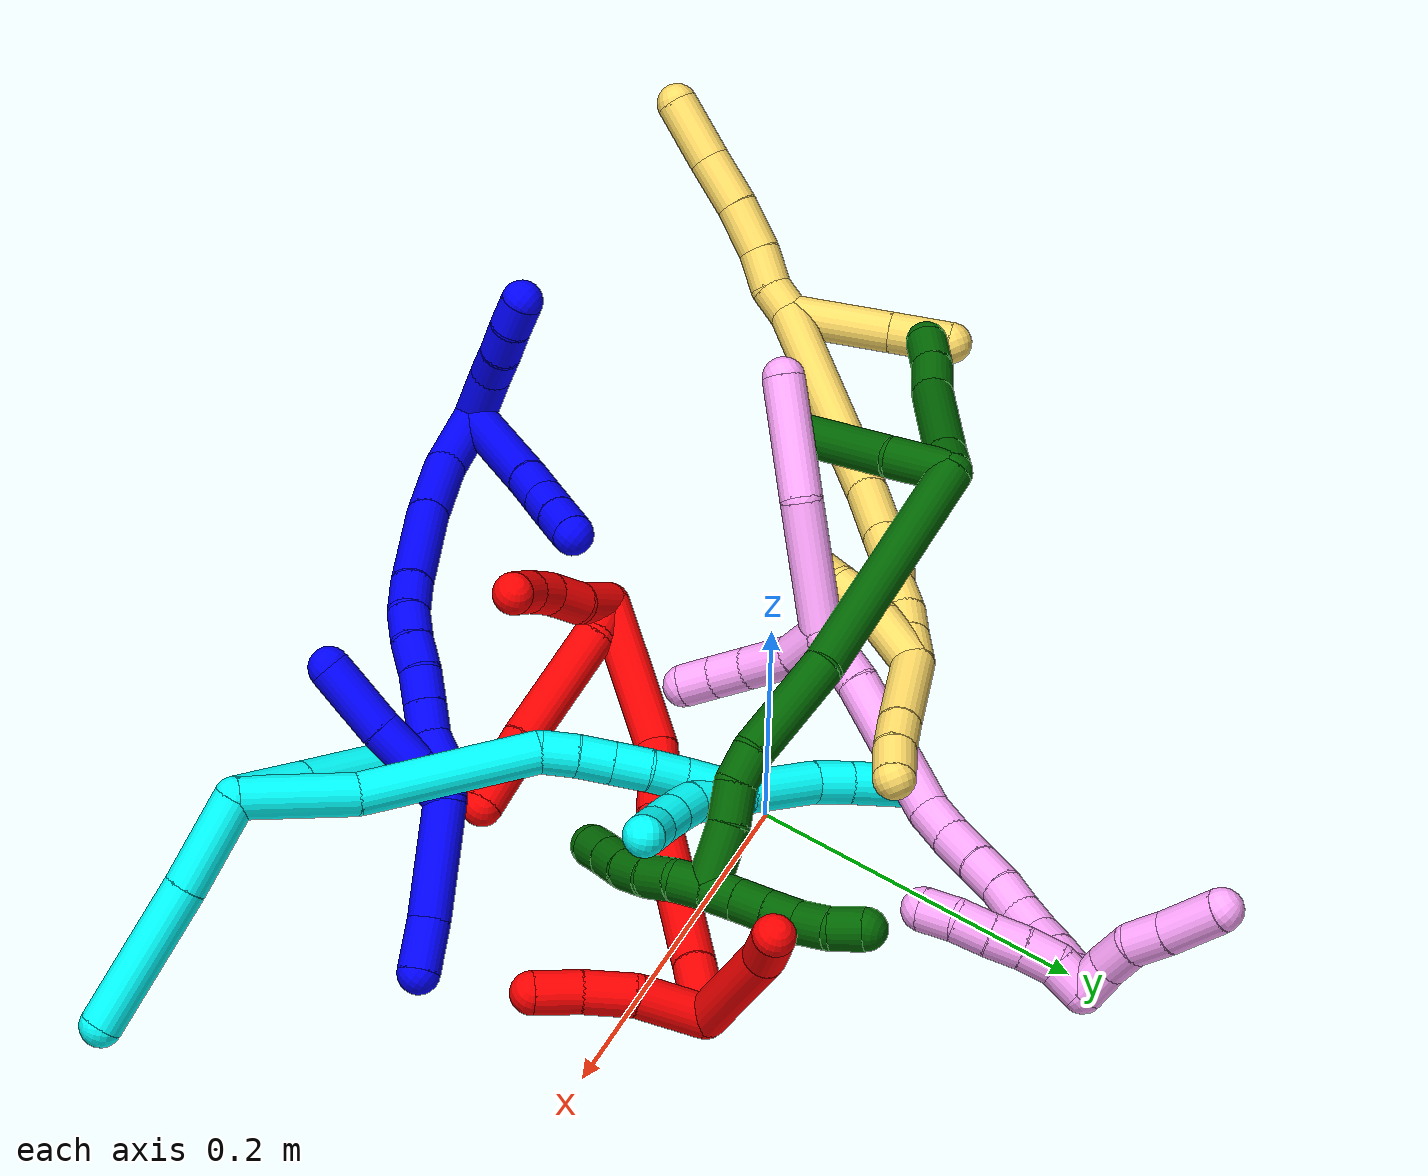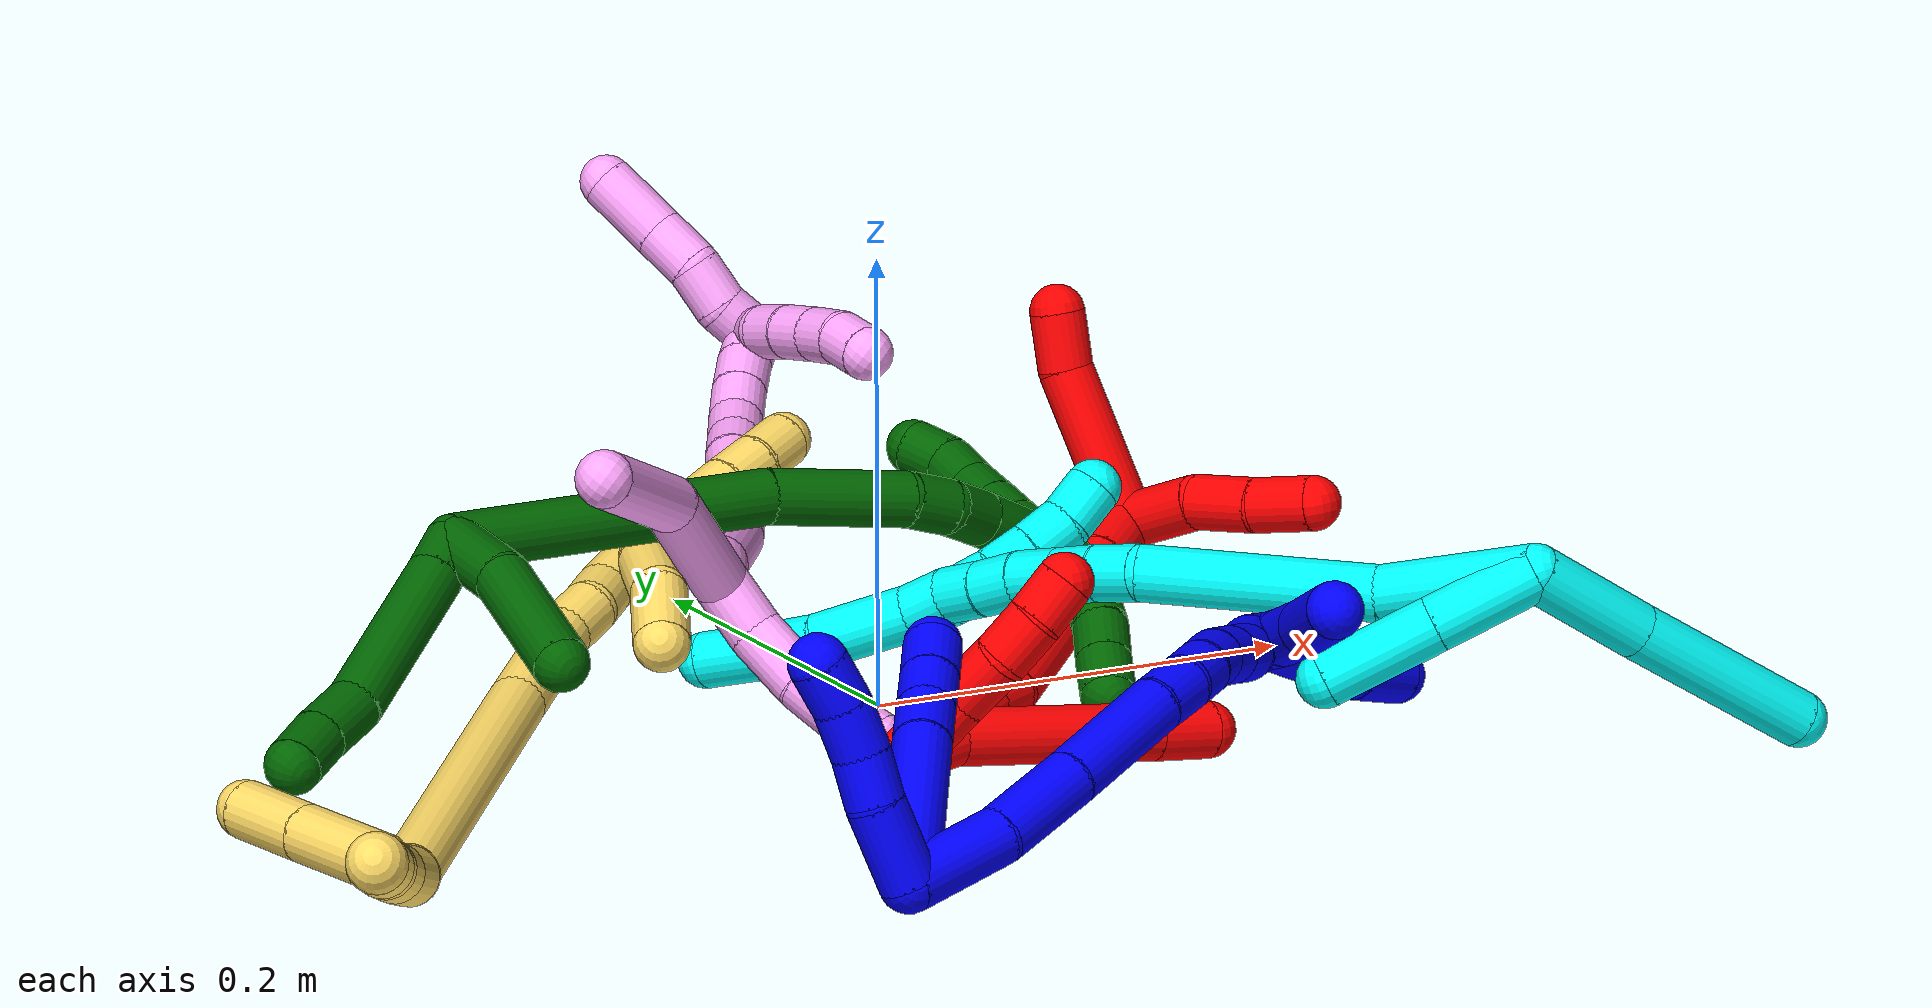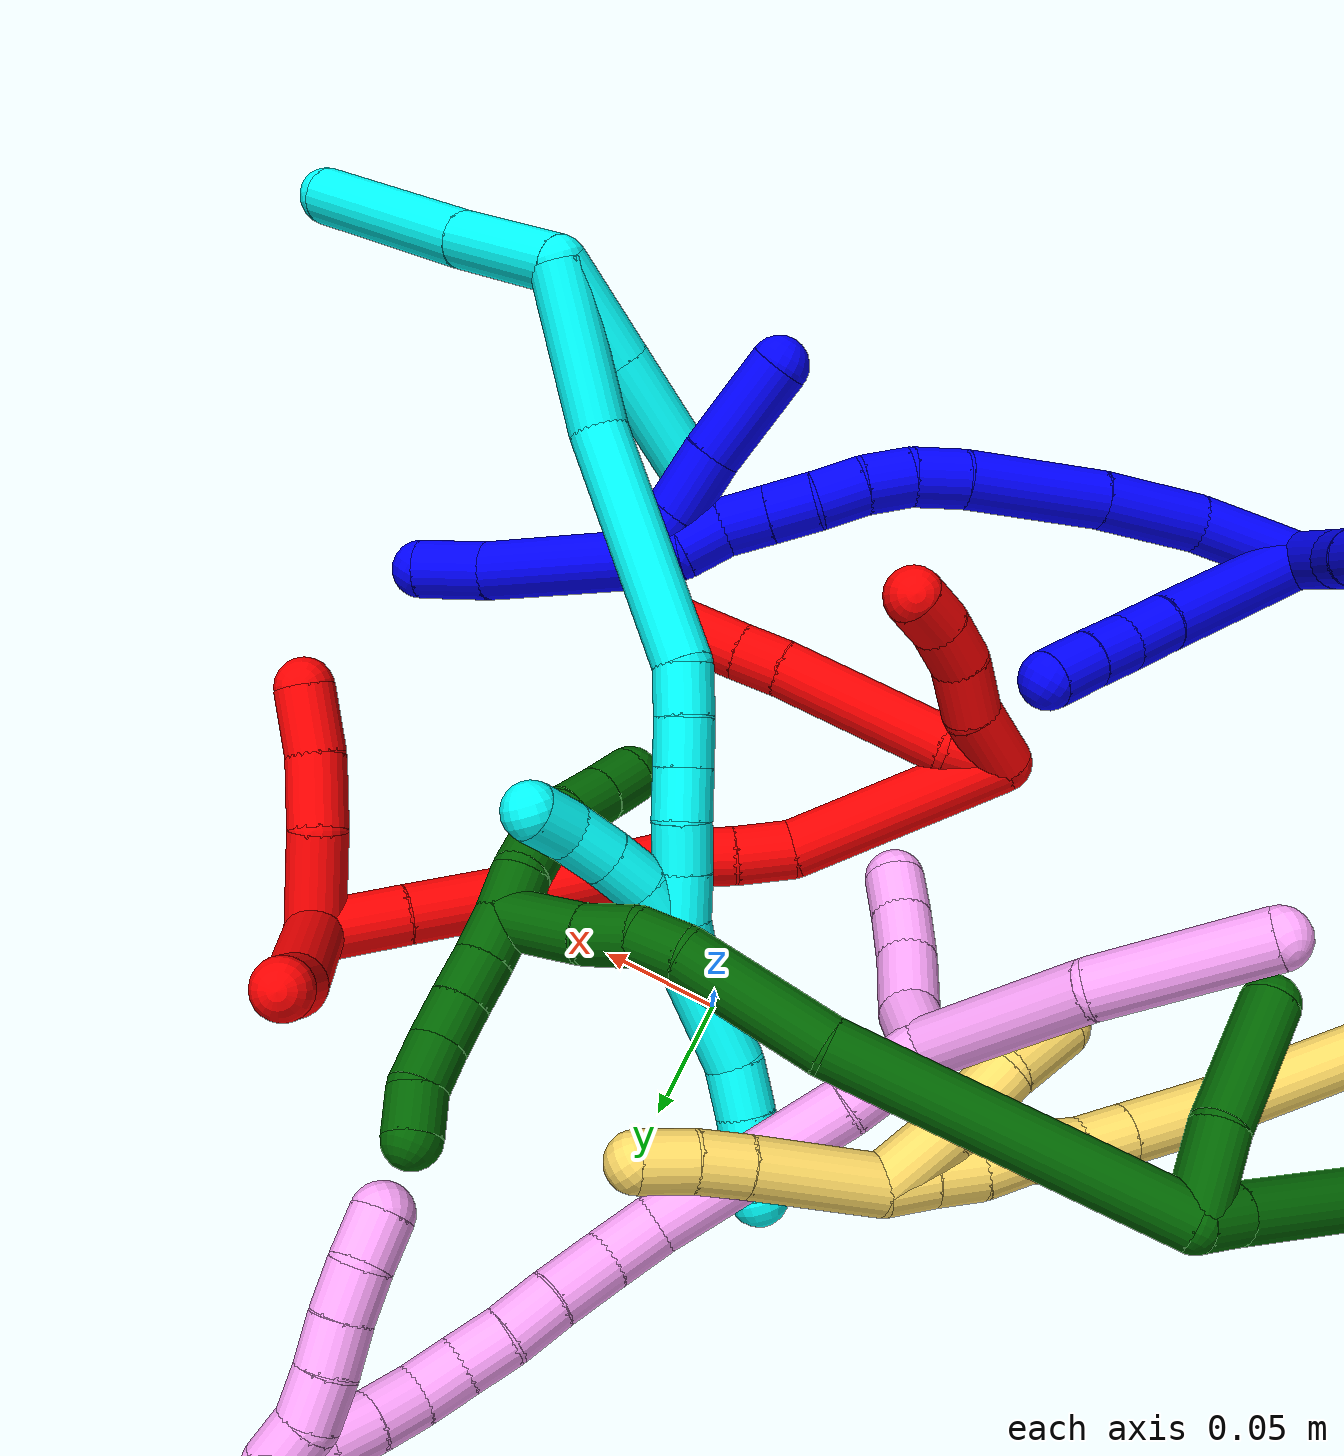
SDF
<sdf version="1.7">
 <world name="default">
  <plugin name="TubeGeneratorPlugin" filename="libtube_generator_plugin.so"/>
  <model name="photoneo_s_sensor">
   <static>1</static>
   <pose>0 0 2 1.57079 1.57079 3.14159</pose>
   <link name="link">
    <inertial><mass>0.1</mass></inertial>
    <sensor name="sensor" type="depth">
     <update_rate>30</update_rate>
     <camera>
      <horizontal_fov>1.22</horizontal_fov>
      <image><width>1920</width><height>1200</height><format>B8G8R8</format></image>
      <clip><near>0.1</near><far>4</far></clip>
      <depth_camera><output>points</output></depth_camera>
     </camera>
     <plugin name="camera_plugin" filename="libgazebo_ros_depth_camera.so">
      <baseline>0.2</baseline>
      <alwaysOn>1</alwaysOn>
      <updateRate>0.0</updateRate>
      <cameraName>camera_ir</cameraName>
      <imageTopicName>/camera/color/image_raw</imageTopicName>
      <cameraInfoTopicName>/camera/color/camera_info</cameraInfoTopicName>
      <depthImageTopicName>/camera/depth/image_raw</depthImageTopicName>
      <depthImageCameraInfoTopicName>/camera/depth/camera_info</depthImageCameraInfoTopicName>
      <pointCloudTopicName>/camera/depth/points</pointCloudTopicName>
      <frameName>fr_optical</frameName>
      <pointCloudCutoff>0.1</pointCloudCutoff>
      <pointCloudCutoffMax>2.0</pointCloudCutoffMax>
      <distortionK1>0</distortionK1>
      <distortionK2>0</distortionK2>
      <distortionK3>0</distortionK3>
      <distortionT1>0</distortionT1>
      <distortionT2>0</distortionT2>
      <CxPrime>0</CxPrime>
      <Cx>0</Cx>
      <Cy>0</Cy>
      <focalLength>0</focalLength>
      <hackBaseline>0</hackBaseline>
     </plugin>
    </sensor>
   </link>
  </model>
  <gravity>0 0 -9.8</gravity>
  <magnetic_field>6e-06 2.3e-05 -4.2e-05</magnetic_field>
  <atmosphere type="adiabatic"/>
  <physics name="default_physics" default="0" type="ode">
   <max_step_size>0.003</max_step_size>
   <real_time_factor>1</real_time_factor>
   <real_time_update_rate>1000</real_time_update_rate>
   <max_contacts>10000</max_contacts>
   <ode>
    <solver>
     <type>quick</type>
     <iters>100</iters>
     <sor>1.3</sor>
     <use_dynamic_moi_rescaling>0</use_dynamic_moi_rescaling>
    </solver>
    <constraints>
     <contact_max_correcting_vel>0</contact_max_correcting_vel>
     <contact_surface_layer>0.001</contact_surface_layer>
     <cfm>0</cfm>
     <erp>0.2</erp>
    </constraints>
   </ode>
  </physics>
  <scene><ambient>0.4 0.4 0.4 1</ambient><background>0.7 0.7 0.7 1</background><shadows>0</shadows></scene>
  <audio><device>default</device></audio>
  <spherical_coordinates>
   <surface_model>EARTH_WGS84</surface_model>
   <latitude_deg>0</latitude_deg>
   <longitude_deg>0</longitude_deg>
   <elevation>0</elevation>
   <heading_deg>0</heading_deg>
  </spherical_coordinates>
  <model name="bin">
   <static>1</static>
   <link name="bottom">
    <collision name="collision-bottom">
     <pose>0 0 -0.01 0 -0 0</pose>
     <geometry><box><size>0.8 0.6 0.02</size></box></geometry>
     <surface>
      <friction><ode><mu>100</mu><mu2>100</mu2></ode></friction>
      <contact><collide_bitmask>65535</collide_bitmask></contact>
     </surface>
    </collision>
   </link>
   <link name="west_wall">
    <collision name="collision-west_wall">
     <pose>-0.41 0 0.1 0 -0 0</pose>
     <geometry><box><size>0.02 0.6 0.2</size></box></geometry>
     <surface>
      <friction><ode><mu>100</mu><mu2>100</mu2></ode></friction>
      <contact><collide_bitmask>65535</collide_bitmask></contact>
     </surface>
    </collision>
   </link>
   <link name="east_wall">
    <collision name="collision-east_wall">
     <pose>0.41 0 0.1 0 -0 0</pose>
     <geometry><box><size>0.02 0.6 0.2</size></box></geometry>
     <surface>
      <friction><ode><mu>100</mu><mu2>100</mu2></ode></friction>
      <contact><collide_bitmask>65535</collide_bitmask></contact>
     </surface>
    </collision>
   </link>
   <link name="south_wall">
    <collision name="collision-south_wall">
     <pose>0 -0.31 0.1 0 -0 0</pose>
     <geometry><box><size>0.8 0.02 0.2</size></box></geometry>
     <surface>
      <friction><ode><mu>100</mu><mu2>100</mu2></ode></friction>
      <contact><collide_bitmask>65535</collide_bitmask></contact>
     </surface>
    </collision>
   </link>
   <link name="north_wall">
    <collision name="collision-north_wall">
     <pose>0 0.31 0.1 0 -0 0</pose>
     <geometry><box><size>0.8 0.02 0.2</size></box></geometry>
     <surface>
      <friction><ode><mu>100</mu><mu2>100</mu2></ode></friction>
      <contact><collide_bitmask>65535</collide_bitmask></contact>
     </surface>
    </collision>
   </link>
  </model>
  <model name="1">
   <static>0</static>
   <link name="1">
    <collision name="collision-cylinder-e_1_2_8">
     <pose>-0.008924 0.031201 -0.027361 -2.29072 -0.211815 0.46089</pose>
     <geometry><cylinder><radius>0.0125</radius><length>0.084894</length></cylinder></geometry>
     <surface>
      <friction><ode><mu>1.16</mu><mu2>1.16</mu2><slip1>0</slip1><slip2>0</slip2></ode></friction>
      <contact><ode><kp>1e+06</kp><kd>1</kd><max_vel>0</max_vel><min_depth>0.001</min_depth></ode></contact>
     </surface>
    </collision>
    <visual name="visual-cylinder-e_1_2_8">
     <pose>-0.008924 0.031201 -0.027361 -2.29072 -0.211815 0.46089</pose>
     <geometry><cylinder><radius>0.0125</radius><length>0.084894</length></cylinder></geometry>
     <material><ambient>0 0 1 1</ambient></material>
    </visual>
    <collision name="collision-cylinder-e_2_8_9">
     <pose>-0.01961 0.070592 -0.062775 -2.34774 -0.152276 0.36004</pose>
     <geometry><cylinder><radius>0.0125</radius><length>0.023241</length></cylinder></geometry>
     <surface>
      <friction><ode><mu>1.16</mu><mu2>1.16</mu2><slip1>0</slip1><slip2>0</slip2></ode></friction>
      <contact><ode><kp>1e+06</kp><kd>1</kd><max_vel>0</max_vel><min_depth>0.001</min_depth></ode></contact>
     </surface>
    </collision>
    <visual name="visual-cylinder-e_2_8_9">
     <pose>-0.01961 0.070592 -0.062775 -2.34774 -0.152276 0.36004</pose>
     <geometry><cylinder><radius>0.0125</radius><length>0.023241</length></cylinder></geometry>
     <material><ambient>0 0 1 1</ambient></material>
    </visual>
    <collision name="collision-cylinder-e_3_9_10">
     <pose>-0.023143 0.086074 -0.077447 -2.3079 -0.177837 0.397376</pose>
     <geometry><cylinder><radius>0.0125</radius><length>0.020013</length></cylinder></geometry>
     <surface>
      <friction><ode><mu>1.16</mu><mu2>1.16</mu2><slip1>0</slip1><slip2>0</slip2></ode></friction>
      <contact><ode><kp>1e+06</kp><kd>1</kd><max_vel>0</max_vel><min_depth>0.001</min_depth></ode></contact>
     </surface>
    </collision>
    <visual name="visual-cylinder-e_3_9_10">
     <pose>-0.023143 0.086074 -0.077447 -2.3079 -0.177837 0.397376</pose>
     <geometry><cylinder><radius>0.0125</radius><length>0.020013</length></cylinder></geometry>
     <material><ambient>0 0 1 1</ambient></material>
    </visual>
    <collision name="collision-cylinder-e_4_10_6">
     <pose>-0.026735 0.101105 -0.091562 -2.34019 -0.167538 0.391347</pose>
     <geometry><cylinder><radius>0.0125</radius><length>0.021852</length></cylinder></geometry>
     <surface>
      <friction><ode><mu>1.16</mu><mu2>1.16</mu2><slip1>0</slip1><slip2>0</slip2></ode></friction>
      <contact><ode><kp>1e+06</kp><kd>1</kd><max_vel>0</max_vel><min_depth>0.001</min_depth></ode></contact>
     </surface>
    </collision>
    <visual name="visual-cylinder-e_4_10_6">
     <pose>-0.026735 0.101105 -0.091562 -2.34019 -0.167538 0.391347</pose>
     <geometry><cylinder><radius>0.0125</radius><length>0.021852</length></cylinder></geometry>
     <material><ambient>0 0 1 1</ambient></material>
    </visual>
    <collision name="collision-cylinder-e_1_2_11">
     <pose>-0.016976 0.006355 0.003001 -1.12966 -1.1783 0.801232</pose>
     <geometry><cylinder><radius>0.0125</radius><length>0.036747</length></cylinder></geometry>
     <surface>
      <friction><ode><mu>1.16</mu><mu2>1.16</mu2><slip1>0</slip1><slip2>0</slip2></ode></friction>
      <contact><ode><kp>1e+06</kp><kd>1</kd><max_vel>0</max_vel><min_depth>0.001</min_depth></ode></contact>
     </surface>
    </collision>
    <visual name="visual-cylinder-e_1_2_11">
     <pose>-0.016976 0.006355 0.003001 -1.12966 -1.1783 0.801232</pose>
     <geometry><cylinder><radius>0.0125</radius><length>0.036747</length></cylinder></geometry>
     <material><ambient>0 0 1 1</ambient></material>
    </visual>
    <collision name="collision-cylinder-e_2_11_12">
     <pose>-0.04319 0.017951 0.00691 -1.39917 -1.04832 0.905605</pose>
     <geometry><cylinder><radius>0.0125</radius><length>0.021321</length></cylinder></geometry>
     <surface>
      <friction><ode><mu>1.16</mu><mu2>1.16</mu2><slip1>0</slip1><slip2>0</slip2></ode></friction>
      <contact><ode><kp>1e+06</kp><kd>1</kd><max_vel>0</max_vel><min_depth>0.001</min_depth></ode></contact>
     </surface>
    </collision>
    <visual name="visual-cylinder-e_2_11_12">
     <pose>-0.04319 0.017951 0.00691 -1.39917 -1.04832 0.905605</pose>
     <geometry><cylinder><radius>0.0125</radius><length>0.021321</length></cylinder></geometry>
     <material><ambient>0 0 1 1</ambient></material>
    </visual>
    <collision name="collision-cylinder-e_3_12_13">
     <pose>-0.062362 0.027271 0.009564 -1.16626 -1.15082 0.808594</pose>
     <geometry><cylinder><radius>0.0125</radius><length>0.021759</length></cylinder></geometry>
     <surface>
      <friction><ode><mu>1.16</mu><mu2>1.16</mu2><slip1>0</slip1><slip2>0</slip2></ode></friction>
      <contact><ode><kp>1e+06</kp><kd>1</kd><max_vel>0</max_vel><min_depth>0.001</min_depth></ode></contact>
     </surface>
    </collision>
    <visual name="visual-cylinder-e_3_12_13">
     <pose>-0.062362 0.027271 0.009564 -1.16626 -1.15082 0.808594</pose>
     <geometry><cylinder><radius>0.0125</radius><length>0.021759</length></cylinder></geometry>
     <material><ambient>0 0 1 1</ambient></material>
    </visual>
    <collision name="collision-cylinder-e_4_13_5">
     <pose>-0.081978 0.033631 0.012982 -0.938591 -1.28651 0.726498</pose>
     <geometry><cylinder><radius>0.0125</radius><length>0.020174</length></cylinder></geometry>
     <surface>
      <friction><ode><mu>1.16</mu><mu2>1.16</mu2><slip1>0</slip1><slip2>0</slip2></ode></friction>
      <contact><ode><kp>1e+06</kp><kd>1</kd><max_vel>0</max_vel><min_depth>0.001</min_depth></ode></contact>
     </surface>
    </collision>
    <visual name="visual-cylinder-e_4_13_5">
     <pose>-0.081978 0.033631 0.012982 -0.938591 -1.28651 0.726498</pose>
     <geometry><cylinder><radius>0.0125</radius><length>0.020174</length></cylinder></geometry>
     <material><ambient>0 0 1 1</ambient></material>
    </visual>
    <collision name="collision-cylinder-e_1_2_14">
     <pose>0.009573 0.021617 -0.004527 -1.77724 0.409026 -0.500017</pose>
     <geometry><cylinder><radius>0.0125</radius><length>0.048142</length></cylinder></geometry>
     <surface>
      <friction><ode><mu>1.16</mu><mu2>1.16</mu2><slip1>0</slip1><slip2>0</slip2></ode></friction>
      <contact><ode><kp>1e+06</kp><kd>1</kd><max_vel>0</max_vel><min_depth>0.001</min_depth></ode></contact>
     </surface>
    </collision>
    <visual name="visual-cylinder-e_1_2_14">
     <pose>0.009573 0.021617 -0.004527 -1.77724 0.409026 -0.500017</pose>
     <geometry><cylinder><radius>0.0125</radius><length>0.048142</length></cylinder></geometry>
     <material><ambient>0 0 1 1</ambient></material>
    </visual>
    <collision name="collision-cylinder-e_2_14_15">
     <pose>0.025119 0.06446 -0.015869 -1.88145 0.261754 -0.357164</pose>
     <geometry><cylinder><radius>0.0125</radius><length>0.04616</length></cylinder></geometry>
     <surface>
      <friction><ode><mu>1.16</mu><mu2>1.16</mu2><slip1>0</slip1><slip2>0</slip2></ode></friction>
      <contact><ode><kp>1e+06</kp><kd>1</kd><max_vel>0</max_vel><min_depth>0.001</min_depth></ode></contact>
     </surface>
    </collision>
    <visual name="visual-cylinder-e_2_14_15">
     <pose>0.025119 0.06446 -0.015869 -1.88145 0.261754 -0.357164</pose>
     <geometry><cylinder><radius>0.0125</radius><length>0.04616</length></cylinder></geometry>
     <material><ambient>0 0 1 1</ambient></material>
    </visual>
    <collision name="collision-cylinder-e_3_15_16">
     <pose>0.038735 0.113348 -0.034101 -1.96226 0.250052 -0.371361</pose>
     <geometry><cylinder><radius>0.0125</radius><length>0.061772</length></cylinder></geometry>
     <surface>
      <friction><ode><mu>1.16</mu><mu2>1.16</mu2><slip1>0</slip1><slip2>0</slip2></ode></friction>
      <contact><ode><kp>1e+06</kp><kd>1</kd><max_vel>0</max_vel><min_depth>0.001</min_depth></ode></contact>
     </surface>
    </collision>
    <visual name="visual-cylinder-e_3_15_16">
     <pose>0.038735 0.113348 -0.034101 -1.96226 0.250052 -0.371361</pose>
     <geometry><cylinder><radius>0.0125</radius><length>0.061772</length></cylinder></geometry>
     <material><ambient>0 0 1 1</ambient></material>
    </visual>
    <collision name="collision-cylinder-e_4_16_17">
     <pose>0.049751 0.150483 -0.050816 -2.08058 0.301345 -0.506525</pose>
     <geometry><cylinder><radius>0.0125</radius><length>0.02273</length></cylinder></geometry>
     <surface>
      <friction><ode><mu>1.16</mu><mu2>1.16</mu2><slip1>0</slip1><slip2>0</slip2></ode></friction>
      <contact><ode><kp>1e+06</kp><kd>1</kd><max_vel>0</max_vel><min_depth>0.001</min_depth></ode></contact>
     </surface>
    </collision>
    <visual name="visual-cylinder-e_4_16_17">
     <pose>0.049751 0.150483 -0.050816 -2.08058 0.301345 -0.506525</pose>
     <geometry><cylinder><radius>0.0125</radius><length>0.02273</length></cylinder></geometry>
     <material><ambient>0 0 1 1</ambient></material>
    </visual>
    <collision name="collision-cylinder-e_5_17_18">
     <pose>0.05606 0.167074 -0.062626 -2.31196 0.295358 -0.651556</pose>
     <geometry><cylinder><radius>0.0125</radius><length>0.020171</length></cylinder></geometry>
     <surface>
      <friction><ode><mu>1.16</mu><mu2>1.16</mu2><slip1>0</slip1><slip2>0</slip2></ode></friction>
      <contact><ode><kp>1e+06</kp><kd>1</kd><max_vel>0</max_vel><min_depth>0.001</min_depth></ode></contact>
     </surface>
    </collision>
    <visual name="visual-cylinder-e_5_17_18">
     <pose>0.05606 0.167074 -0.062626 -2.31196 0.295358 -0.651556</pose>
     <geometry><cylinder><radius>0.0125</radius><length>0.020171</length></cylinder></geometry>
     <material><ambient>0 0 1 1</ambient></material>
    </visual>
    <collision name="collision-cylinder-e_6_18_19">
     <pose>0.062013 0.180385 -0.076982 -2.4731 0.293262 -0.804221</pose>
     <geometry><cylinder><radius>0.0125</radius><length>0.020876</length></cylinder></geometry>
     <surface>
      <friction><ode><mu>1.16</mu><mu2>1.16</mu2><slip1>0</slip1><slip2>0</slip2></ode></friction>
      <contact><ode><kp>1e+06</kp><kd>1</kd><max_vel>0</max_vel><min_depth>0.001</min_depth></ode></contact>
     </surface>
    </collision>
    <visual name="visual-cylinder-e_6_18_19">
     <pose>0.062013 0.180385 -0.076982 -2.4731 0.293262 -0.804221</pose>
     <geometry><cylinder><radius>0.0125</radius><length>0.020876</length></cylinder></geometry>
     <material><ambient>0 0 1 1</ambient></material>
    </visual>
    <collision name="collision-cylinder-e_7_19_20">
     <pose>0.069522 0.191855 -0.092108 -2.51469 0.463075 -1.25771</pose>
     <geometry><cylinder><radius>0.0125</radius><length>0.020108</length></cylinder></geometry>
     <surface>
      <friction><ode><mu>1.16</mu><mu2>1.16</mu2><slip1>0</slip1><slip2>0</slip2></ode></friction>
      <contact><ode><kp>1e+06</kp><kd>1</kd><max_vel>0</max_vel><min_depth>0.001</min_depth></ode></contact>
     </surface>
    </collision>
    <visual name="visual-cylinder-e_7_19_20">
     <pose>0.069522 0.191855 -0.092108 -2.51469 0.463075 -1.25771</pose>
     <geometry><cylinder><radius>0.0125</radius><length>0.020108</length></cylinder></geometry>
     <material><ambient>0 0 1 1</ambient></material>
    </visual>
    <collision name="collision-cylinder-e_8_20_21">
     <pose>0.078575 0.20236 -0.106595 -2.51366 0.473653 -1.27841</pose>
     <geometry><cylinder><radius>0.0125</radius><length>0.020003</length></cylinder></geometry>
     <surface>
      <friction><ode><mu>1.16</mu><mu2>1.16</mu2><slip1>0</slip1><slip2>0</slip2></ode></friction>
      <contact><ode><kp>1e+06</kp><kd>1</kd><max_vel>0</max_vel><min_depth>0.001</min_depth></ode></contact>
     </surface>
    </collision>
    <visual name="visual-cylinder-e_8_20_21">
     <pose>0.078575 0.20236 -0.106595 -2.51366 0.473653 -1.27841</pose>
     <geometry><cylinder><radius>0.0125</radius><length>0.020003</length></cylinder></geometry>
     <material><ambient>0 0 1 1</ambient></material>
    </visual>
    <collision name="collision-cylinder-e_9_21_22">
     <pose>0.085176 0.21244 -0.122319 -2.6241 0.205091 -0.741619</pose>
     <geometry><cylinder><radius>0.0125</radius><length>0.02003</length></cylinder></geometry>
     <surface>
      <friction><ode><mu>1.16</mu><mu2>1.16</mu2><slip1>0</slip1><slip2>0</slip2></ode></friction>
      <contact><ode><kp>1e+06</kp><kd>1</kd><max_vel>0</max_vel><min_depth>0.001</min_depth></ode></contact>
     </surface>
    </collision>
    <visual name="visual-cylinder-e_9_21_22">
     <pose>0.085176 0.21244 -0.122319 -2.6241 0.205091 -0.741619</pose>
     <geometry><cylinder><radius>0.0125</radius><length>0.02003</length></cylinder></geometry>
     <material><ambient>0 0 1 1</ambient></material>
    </visual>
    <collision name="collision-cylinder-e_10_22_1">
     <pose>0.092094 0.222854 -0.137573 -2.45096 0.509364 -1.2529</pose>
     <geometry><cylinder><radius>0.0125</radius><length>0.020008</length></cylinder></geometry>
     <surface>
      <friction><ode><mu>1.16</mu><mu2>1.16</mu2><slip1>0</slip1><slip2>0</slip2></ode></friction>
      <contact><ode><kp>1e+06</kp><kd>1</kd><max_vel>0</max_vel><min_depth>0.001</min_depth></ode></contact>
     </surface>
    </collision>
    <visual name="visual-cylinder-e_10_22_1">
     <pose>0.092094 0.222854 -0.137573 -2.45096 0.509364 -1.2529</pose>
     <geometry><cylinder><radius>0.0125</radius><length>0.020008</length></cylinder></geometry>
     <material><ambient>0 0 1 1</ambient></material>
    </visual>
    <collision name="collision-cylinder-e_1_1_23">
     <pose>0.122034 0.243318 -0.162747 -2.46199 0.813135 -1.7667</pose>
     <geometry><cylinder><radius>0.0125</radius><length>0.068999</length></cylinder></geometry>
     <surface>
      <friction><ode><mu>1.16</mu><mu2>1.16</mu2><slip1>0</slip1><slip2>0</slip2></ode></friction>
      <contact><ode><kp>1e+06</kp><kd>1</kd><max_vel>0</max_vel><min_depth>0.001</min_depth></ode></contact>
     </surface>
    </collision>
    <visual name="visual-cylinder-e_1_1_23">
     <pose>0.122034 0.243318 -0.162747 -2.46199 0.813135 -1.7667</pose>
     <geometry><cylinder><radius>0.0125</radius><length>0.068999</length></cylinder></geometry>
     <material><ambient>0 0 1 1</ambient></material>
    </visual>
    <collision name="collision-cylinder-e_2_23_4">
     <pose>0.157555 0.266955 -0.188574 -2.27264 0.740591 -1.39327</pose>
     <geometry><cylinder><radius>0.0125</radius><length>0.031001</length></cylinder></geometry>
     <surface>
      <friction><ode><mu>1.16</mu><mu2>1.16</mu2><slip1>0</slip1><slip2>0</slip2></ode></friction>
      <contact><ode><kp>1e+06</kp><kd>1</kd><max_vel>0</max_vel><min_depth>0.001</min_depth></ode></contact>
     </surface>
    </collision>
    <visual name="visual-cylinder-e_2_23_4">
     <pose>0.157555 0.266955 -0.188574 -2.27264 0.740591 -1.39327</pose>
     <geometry><cylinder><radius>0.0125</radius><length>0.031001</length></cylinder></geometry>
     <material><ambient>0 0 1 1</ambient></material>
    </visual>
    <collision name="collision-cylinder-e_1_1_24">
     <pose>0.095067 0.227081 -0.131777 0.106285 -0.150044 -0.007996</pose>
     <geometry><cylinder><radius>0.0125</radius><length>0.025485</length></cylinder></geometry>
     <surface>
      <friction><ode><mu>1.16</mu><mu2>1.16</mu2><slip1>0</slip1><slip2>0</slip2></ode></friction>
      <contact><ode><kp>1e+06</kp><kd>1</kd><max_vel>0</max_vel><min_depth>0.001</min_depth></ode></contact>
     </surface>
    </collision>
    <visual name="visual-cylinder-e_1_1_24">
     <pose>0.095067 0.227081 -0.131777 0.106285 -0.150044 -0.007996</pose>
     <geometry><cylinder><radius>0.0125</radius><length>0.025485</length></cylinder></geometry>
     <material><ambient>0 0 1 1</ambient></material>
    </visual>
    <collision name="collision-cylinder-e_2_24_25">
     <pose>0.091323 0.226129 -0.104753 -0.026509 -0.126152 0.001674</pose>
     <geometry><cylinder><radius>0.0125</radius><length>0.029235</length></cylinder></geometry>
     <surface>
      <friction><ode><mu>1.16</mu><mu2>1.16</mu2><slip1>0</slip1><slip2>0</slip2></ode></friction>
      <contact><ode><kp>1e+06</kp><kd>1</kd><max_vel>0</max_vel><min_depth>0.001</min_depth></ode></contact>
     </surface>
    </collision>
    <visual name="visual-cylinder-e_2_24_25">
     <pose>0.091323 0.226129 -0.104753 -0.026509 -0.126152 0.001674</pose>
     <geometry><cylinder><radius>0.0125</radius><length>0.029235</length></cylinder></geometry>
     <material><ambient>0 0 1 1</ambient></material>
    </visual>
    <collision name="collision-cylinder-e_3_25_3">
     <pose>0.085184 0.226078 -0.068033 0.019572 -0.191099 -0.001876</pose>
     <geometry><cylinder><radius>0.0125</radius><length>0.04528</length></cylinder></geometry>
     <surface>
      <friction><ode><mu>1.16</mu><mu2>1.16</mu2><slip1>0</slip1><slip2>0</slip2></ode></friction>
      <contact><ode><kp>1e+06</kp><kd>1</kd><max_vel>0</max_vel><min_depth>0.001</min_depth></ode></contact>
     </surface>
    </collision>
    <visual name="visual-cylinder-e_3_25_3">
     <pose>0.085184 0.226078 -0.068033 0.019572 -0.191099 -0.001876</pose>
     <geometry><cylinder><radius>0.0125</radius><length>0.04528</length></cylinder></geometry>
     <material><ambient>0 0 1 1</ambient></material>
    </visual>
    <collision name="collision-sphere-3">
     <pose>0.080884 0.225643 -0.045809 0 -0 0</pose>
     <geometry><sphere><radius>0.0125</radius></sphere></geometry>
     <surface>
      <friction><ode><mu>1.16</mu><mu2>1.16</mu2><slip1>0</slip1><slip2>0</slip2></ode></friction>
      <contact><ode><kp>1e+06</kp><kd>1</kd><max_vel>0</max_vel><min_depth>0.001</min_depth></ode></contact>
     </surface>
    </collision>
    <visual name="visual-sphere-3">
     <pose>0.080884 0.225643 -0.045809 0 -0 0</pose>
     <geometry><sphere><radius>0.0125</radius></sphere></geometry>
     <material><ambient>0 0 1 1</ambient></material>
    </visual>
    <collision name="collision-sphere-25">
     <pose>0.089484 0.226513 -0.090257 0 -0 0</pose>
     <geometry><sphere><radius>0.0125</radius></sphere></geometry>
     <surface>
      <friction><ode><mu>1.16</mu><mu2>1.16</mu2><slip1>0</slip1><slip2>0</slip2></ode></friction>
      <contact><ode><kp>1e+06</kp><kd>1</kd><max_vel>0</max_vel><min_depth>0.001</min_depth></ode></contact>
     </surface>
    </collision>
    <visual name="visual-sphere-25">
     <pose>0.089484 0.226513 -0.090257 0 -0 0</pose>
     <geometry><sphere><radius>0.0125</radius></sphere></geometry>
     <material><ambient>0 0 1 1</ambient></material>
    </visual>
    <collision name="collision-sphere-24">
     <pose>0.093163 0.225745 -0.119249 0 -0 0</pose>
     <geometry><sphere><radius>0.0125</radius></sphere></geometry>
     <surface>
      <friction><ode><mu>1.16</mu><mu2>1.16</mu2><slip1>0</slip1><slip2>0</slip2></ode></friction>
      <contact><ode><kp>1e+06</kp><kd>1</kd><max_vel>0</max_vel><min_depth>0.001</min_depth></ode></contact>
     </surface>
    </collision>
    <visual name="visual-sphere-24">
     <pose>0.093163 0.225745 -0.119249 0 -0 0</pose>
     <geometry><sphere><radius>0.0125</radius></sphere></geometry>
     <material><ambient>0 0 1 1</ambient></material>
    </visual>
    <collision name="collision-sphere-4">
     <pose>0.168013 0.275692 -0.195961 0 -0 0</pose>
     <geometry><sphere><radius>0.0125</radius></sphere></geometry>
     <surface>
      <friction><ode><mu>1.16</mu><mu2>1.16</mu2><slip1>0</slip1><slip2>0</slip2></ode></friction>
      <contact><ode><kp>1e+06</kp><kd>1</kd><max_vel>0</max_vel><min_depth>0.001</min_depth></ode></contact>
     </surface>
    </collision>
    <visual name="visual-sphere-4">
     <pose>0.168013 0.275692 -0.195961 0 -0 0</pose>
     <geometry><sphere><radius>0.0125</radius></sphere></geometry>
     <material><ambient>0 0 1 1</ambient></material>
    </visual>
    <collision name="collision-sphere-23">
     <pose>0.147096 0.258219 -0.181188 0 -0 0</pose>
     <geometry><sphere><radius>0.0125</radius></sphere></geometry>
     <surface>
      <friction><ode><mu>1.16</mu><mu2>1.16</mu2><slip1>0</slip1><slip2>0</slip2></ode></friction>
      <contact><ode><kp>1e+06</kp><kd>1</kd><max_vel>0</max_vel><min_depth>0.001</min_depth></ode></contact>
     </surface>
    </collision>
    <visual name="visual-sphere-23">
     <pose>0.147096 0.258219 -0.181188 0 -0 0</pose>
     <geometry><sphere><radius>0.0125</radius></sphere></geometry>
     <material><ambient>0 0 1 1</ambient></material>
    </visual>
    <collision name="collision-sphere-1">
     <pose>0.096972 0.228418 -0.144305 0 -0 0</pose>
     <geometry><sphere><radius>0.0125</radius></sphere></geometry>
     <surface>
      <friction><ode><mu>1.16</mu><mu2>1.16</mu2><slip1>0</slip1><slip2>0</slip2></ode></friction>
      <contact><ode><kp>1e+06</kp><kd>1</kd><max_vel>0</max_vel><min_depth>0.001</min_depth></ode></contact>
     </surface>
    </collision>
    <visual name="visual-sphere-1">
     <pose>0.096972 0.228418 -0.144305 0 -0 0</pose>
     <geometry><sphere><radius>0.0125</radius></sphere></geometry>
     <material><ambient>0 0 1 1</ambient></material>
    </visual>
    <collision name="collision-sphere-22">
     <pose>0.087216 0.21729 -0.13084 0 -0 0</pose>
     <geometry><sphere><radius>0.0125</radius></sphere></geometry>
     <surface>
      <friction><ode><mu>1.16</mu><mu2>1.16</mu2><slip1>0</slip1><slip2>0</slip2></ode></friction>
      <contact><ode><kp>1e+06</kp><kd>1</kd><max_vel>0</max_vel><min_depth>0.001</min_depth></ode></contact>
     </surface>
    </collision>
    <visual name="visual-sphere-22">
     <pose>0.087216 0.21729 -0.13084 0 -0 0</pose>
     <geometry><sphere><radius>0.0125</radius></sphere></geometry>
     <material><ambient>0 0 1 1</ambient></material>
    </visual>
    <collision name="collision-sphere-21">
     <pose>0.083137 0.207589 -0.113798 0 -0 0</pose>
     <geometry><sphere><radius>0.0125</radius></sphere></geometry>
     <surface>
      <friction><ode><mu>1.16</mu><mu2>1.16</mu2><slip1>0</slip1><slip2>0</slip2></ode></friction>
      <contact><ode><kp>1e+06</kp><kd>1</kd><max_vel>0</max_vel><min_depth>0.001</min_depth></ode></contact>
     </surface>
    </collision>
    <visual name="visual-sphere-21">
     <pose>0.083137 0.207589 -0.113798 0 -0 0</pose>
     <geometry><sphere><radius>0.0125</radius></sphere></geometry>
     <material><ambient>0 0 1 1</ambient></material>
    </visual>
    <collision name="collision-sphere-11">
     <pose>-0.033952 0.01271 0.006001 0 -0 0</pose>
     <geometry><sphere><radius>0.0125</radius></sphere></geometry>
     <surface>
      <friction><ode><mu>1.16</mu><mu2>1.16</mu2><slip1>0</slip1><slip2>0</slip2></ode></friction>
      <contact><ode><kp>1e+06</kp><kd>1</kd><max_vel>0</max_vel><min_depth>0.001</min_depth></ode></contact>
     </surface>
    </collision>
    <visual name="visual-sphere-11">
     <pose>-0.033952 0.01271 0.006001 0 -0 0</pose>
     <geometry><sphere><radius>0.0125</radius></sphere></geometry>
     <material><ambient>0 0 1 1</ambient></material>
    </visual>
    <collision name="collision-sphere-6">
     <pose>-0.028557 0.108844 -0.099057 0 -0 0</pose>
     <geometry><sphere><radius>0.0125</radius></sphere></geometry>
     <surface>
      <friction><ode><mu>1.16</mu><mu2>1.16</mu2><slip1>0</slip1><slip2>0</slip2></ode></friction>
      <contact><ode><kp>1e+06</kp><kd>1</kd><max_vel>0</max_vel><min_depth>0.001</min_depth></ode></contact>
     </surface>
    </collision>
    <visual name="visual-sphere-6">
     <pose>-0.028557 0.108844 -0.099057 0 -0 0</pose>
     <geometry><sphere><radius>0.0125</radius></sphere></geometry>
     <material><ambient>0 0 1 1</ambient></material>
    </visual>
    <collision name="collision-sphere-10">
     <pose>-0.024913 0.093366 -0.084067 0 -0 0</pose>
     <geometry><sphere><radius>0.0125</radius></sphere></geometry>
     <surface>
      <friction><ode><mu>1.16</mu><mu2>1.16</mu2><slip1>0</slip1><slip2>0</slip2></ode></friction>
      <contact><ode><kp>1e+06</kp><kd>1</kd><max_vel>0</max_vel><min_depth>0.001</min_depth></ode></contact>
     </surface>
    </collision>
    <visual name="visual-sphere-10">
     <pose>-0.024913 0.093366 -0.084067 0 -0 0</pose>
     <geometry><sphere><radius>0.0125</radius></sphere></geometry>
     <material><ambient>0 0 1 1</ambient></material>
    </visual>
    <collision name="collision-sphere-9">
     <pose>-0.021373 0.078782 -0.070827 0 -0 0</pose>
     <geometry><sphere><radius>0.0125</radius></sphere></geometry>
     <surface>
      <friction><ode><mu>1.16</mu><mu2>1.16</mu2><slip1>0</slip1><slip2>0</slip2></ode></friction>
      <contact><ode><kp>1e+06</kp><kd>1</kd><max_vel>0</max_vel><min_depth>0.001</min_depth></ode></contact>
     </surface>
    </collision>
    <visual name="visual-sphere-9">
     <pose>-0.021373 0.078782 -0.070827 0 -0 0</pose>
     <geometry><sphere><radius>0.0125</radius></sphere></geometry>
     <material><ambient>0 0 1 1</ambient></material>
    </visual>
    <collision name="collision-sphere-2">
     <geometry><sphere><radius>0.0125</radius></sphere></geometry>
     <surface>
      <friction><ode><mu>1.16</mu><mu2>1.16</mu2><slip1>0</slip1><slip2>0</slip2></ode></friction>
      <contact><ode><kp>1e+06</kp><kd>1</kd><max_vel>0</max_vel><min_depth>0.001</min_depth></ode></contact>
     </surface>
    </collision>
    <visual name="visual-sphere-2">
     <geometry><sphere><radius>0.0125</radius></sphere></geometry>
     <material><ambient>0 0 1 1</ambient></material>
    </visual>
    <collision name="collision-sphere-19">
     <pose>0.06503 0.186578 -0.084824 0 -0 0</pose>
     <geometry><sphere><radius>0.0125</radius></sphere></geometry>
     <surface>
      <friction><ode><mu>1.16</mu><mu2>1.16</mu2><slip1>0</slip1><slip2>0</slip2></ode></friction>
      <contact><ode><kp>1e+06</kp><kd>1</kd><max_vel>0</max_vel><min_depth>0.001</min_depth></ode></contact>
     </surface>
    </collision>
    <visual name="visual-sphere-19">
     <pose>0.06503 0.186578 -0.084824 0 -0 0</pose>
     <geometry><sphere><radius>0.0125</radius></sphere></geometry>
     <material><ambient>0 0 1 1</ambient></material>
    </visual>
    <collision name="collision-sphere-8">
     <pose>-0.017848 0.062402 -0.054722 0 -0 0</pose>
     <geometry><sphere><radius>0.0125</radius></sphere></geometry>
     <surface>
      <friction><ode><mu>1.16</mu><mu2>1.16</mu2><slip1>0</slip1><slip2>0</slip2></ode></friction>
      <contact><ode><kp>1e+06</kp><kd>1</kd><max_vel>0</max_vel><min_depth>0.001</min_depth></ode></contact>
     </surface>
    </collision>
    <visual name="visual-sphere-8">
     <pose>-0.017848 0.062402 -0.054722 0 -0 0</pose>
     <geometry><sphere><radius>0.0125</radius></sphere></geometry>
     <material><ambient>0 0 1 1</ambient></material>
    </visual>
    <collision name="collision-sphere-12">
     <pose>-0.052428 0.023193 0.007818 0 -0 0</pose>
     <geometry><sphere><radius>0.0125</radius></sphere></geometry>
     <surface>
      <friction><ode><mu>1.16</mu><mu2>1.16</mu2><slip1>0</slip1><slip2>0</slip2></ode></friction>
      <contact><ode><kp>1e+06</kp><kd>1</kd><max_vel>0</max_vel><min_depth>0.001</min_depth></ode></contact>
     </surface>
    </collision>
    <visual name="visual-sphere-12">
     <pose>-0.052428 0.023193 0.007818 0 -0 0</pose>
     <geometry><sphere><radius>0.0125</radius></sphere></geometry>
     <material><ambient>0 0 1 1</ambient></material>
    </visual>
    <collision name="collision-sphere-13">
     <pose>-0.072296 0.031349 0.01131 0 -0 0</pose>
     <geometry><sphere><radius>0.0125</radius></sphere></geometry>
     <surface>
      <friction><ode><mu>1.16</mu><mu2>1.16</mu2><slip1>0</slip1><slip2>0</slip2></ode></friction>
      <contact><ode><kp>1e+06</kp><kd>1</kd><max_vel>0</max_vel><min_depth>0.001</min_depth></ode></contact>
     </surface>
    </collision>
    <visual name="visual-sphere-13">
     <pose>-0.072296 0.031349 0.01131 0 -0 0</pose>
     <geometry><sphere><radius>0.0125</radius></sphere></geometry>
     <material><ambient>0 0 1 1</ambient></material>
    </visual>
    <collision name="collision-sphere-5">
     <pose>-0.091661 0.035914 0.014654 0 -0 0</pose>
     <geometry><sphere><radius>0.0125</radius></sphere></geometry>
     <surface>
      <friction><ode><mu>1.16</mu><mu2>1.16</mu2><slip1>0</slip1><slip2>0</slip2></ode></friction>
      <contact><ode><kp>1e+06</kp><kd>1</kd><max_vel>0</max_vel><min_depth>0.001</min_depth></ode></contact>
     </surface>
    </collision>
    <visual name="visual-sphere-5">
     <pose>-0.091661 0.035914 0.014654 0 -0 0</pose>
     <geometry><sphere><radius>0.0125</radius></sphere></geometry>
     <material><ambient>0 0 1 1</ambient></material>
    </visual>
    <collision name="collision-sphere-14">
     <pose>0.019147 0.043233 -0.009054 0 -0 0</pose>
     <geometry><sphere><radius>0.0125</radius></sphere></geometry>
     <surface>
      <friction><ode><mu>1.16</mu><mu2>1.16</mu2><slip1>0</slip1><slip2>0</slip2></ode></friction>
      <contact><ode><kp>1e+06</kp><kd>1</kd><max_vel>0</max_vel><min_depth>0.001</min_depth></ode></contact>
     </surface>
    </collision>
    <visual name="visual-sphere-14">
     <pose>0.019147 0.043233 -0.009054 0 -0 0</pose>
     <geometry><sphere><radius>0.0125</radius></sphere></geometry>
     <material><ambient>0 0 1 1</ambient></material>
    </visual>
    <collision name="collision-sphere-15">
     <pose>0.031092 0.085686 -0.022684 0 -0 0</pose>
     <geometry><sphere><radius>0.0125</radius></sphere></geometry>
     <surface>
      <friction><ode><mu>1.16</mu><mu2>1.16</mu2><slip1>0</slip1><slip2>0</slip2></ode></friction>
      <contact><ode><kp>1e+06</kp><kd>1</kd><max_vel>0</max_vel><min_depth>0.001</min_depth></ode></contact>
     </surface>
    </collision>
    <visual name="visual-sphere-15">
     <pose>0.031092 0.085686 -0.022684 0 -0 0</pose>
     <geometry><sphere><radius>0.0125</radius></sphere></geometry>
     <material><ambient>0 0 1 1</ambient></material>
    </visual>
    <collision name="collision-sphere-16">
     <pose>0.046378 0.14101 -0.045519 0 -0 0</pose>
     <geometry><sphere><radius>0.0125</radius></sphere></geometry>
     <surface>
      <friction><ode><mu>1.16</mu><mu2>1.16</mu2><slip1>0</slip1><slip2>0</slip2></ode></friction>
      <contact><ode><kp>1e+06</kp><kd>1</kd><max_vel>0</max_vel><min_depth>0.001</min_depth></ode></contact>
     </surface>
    </collision>
    <visual name="visual-sphere-16">
     <pose>0.046378 0.14101 -0.045519 0 -0 0</pose>
     <geometry><sphere><radius>0.0125</radius></sphere></geometry>
     <material><ambient>0 0 1 1</ambient></material>
    </visual>
    <collision name="collision-sphere-17">
     <pose>0.053124 0.159956 -0.056112 0 -0 0</pose>
     <geometry><sphere><radius>0.0125</radius></sphere></geometry>
     <surface>
      <friction><ode><mu>1.16</mu><mu2>1.16</mu2><slip1>0</slip1><slip2>0</slip2></ode></friction>
      <contact><ode><kp>1e+06</kp><kd>1</kd><max_vel>0</max_vel><min_depth>0.001</min_depth></ode></contact>
     </surface>
    </collision>
    <visual name="visual-sphere-17">
     <pose>0.053124 0.159956 -0.056112 0 -0 0</pose>
     <geometry><sphere><radius>0.0125</radius></sphere></geometry>
     <material><ambient>0 0 1 1</ambient></material>
    </visual>
    <collision name="collision-sphere-18">
     <pose>0.058996 0.174191 -0.069141 0 -0 0</pose>
     <geometry><sphere><radius>0.0125</radius></sphere></geometry>
     <surface>
      <friction><ode><mu>1.16</mu><mu2>1.16</mu2><slip1>0</slip1><slip2>0</slip2></ode></friction>
      <contact><ode><kp>1e+06</kp><kd>1</kd><max_vel>0</max_vel><min_depth>0.001</min_depth></ode></contact>
     </surface>
    </collision>
    <visual name="visual-sphere-18">
     <pose>0.058996 0.174191 -0.069141 0 -0 0</pose>
     <geometry><sphere><radius>0.0125</radius></sphere></geometry>
     <material><ambient>0 0 1 1</ambient></material>
    </visual>
    <collision name="collision-sphere-20">
     <pose>0.074013 0.197132 -0.099393 0 -0 0</pose>
     <geometry><sphere><radius>0.0125</radius></sphere></geometry>
     <surface>
      <friction><ode><mu>1.16</mu><mu2>1.16</mu2><slip1>0</slip1><slip2>0</slip2></ode></friction>
      <contact><ode><kp>1e+06</kp><kd>1</kd><max_vel>0</max_vel><min_depth>0.001</min_depth></ode></contact>
     </surface>
    </collision>
    <visual name="visual-sphere-20">
     <pose>0.074013 0.197132 -0.099393 0 -0 0</pose>
     <geometry><sphere><radius>0.0125</radius></sphere></geometry>
     <material><ambient>0 0 1 1</ambient></material>
    </visual>
    <inertial>
     <pose>0.039368 0.128003 -0.065934 0 -0 0</pose>
     <mass>0.75</mass>
     <inertia>
      <ixx>9.5e-05</ixx>
      <ixy>0</ixy>
      <ixz>0</ixz>
      <iyy>1.7e-05</iyy>
      <iyz>0</iyz>
      <izz>-0.000138</izz>
     </inertia>
    </inertial>
   </link>
   <pose>-0.136693 -0.285449 0.015504 1.14785 0.800288 -0.400488</pose>
  </model>
  <model name="2">
   <static>0</static>
   <link name="2">
    <collision name="collision-cylinder-e_1_2_8">
     <pose>0.012051 0.004486 0.000682 -1.42 1.21067 -1.07317</pose>
     <geometry><cylinder><radius>0.0125</radius><length>0.025755</length></cylinder></geometry>
     <surface>
      <friction><ode><mu>1.16</mu><mu2>1.16</mu2><slip1>0</slip1><slip2>0</slip2></ode></friction>
      <contact><ode><kp>1e+06</kp><kd>1</kd><max_vel>0</max_vel><min_depth>0.001</min_depth></ode></contact>
     </surface>
    </collision>
    <visual name="visual-cylinder-e_1_2_8">
     <pose>0.012051 0.004486 0.000682 -1.42 1.21067 -1.07317</pose>
     <geometry><cylinder><radius>0.0125</radius><length>0.025755</length></cylinder></geometry>
     <material><ambient>1 0 0 1</ambient></material>
    </visual>
    <collision name="collision-cylinder-e_2_8_9">
     <pose>0.060912 0.015792 -0.006415 -2.42184 1.29683 -2.21979</pose>
     <geometry><cylinder><radius>0.0125</radius><length>0.076471</length></cylinder></geometry>
     <surface>
      <friction><ode><mu>1.16</mu><mu2>1.16</mu2><slip1>0</slip1><slip2>0</slip2></ode></friction>
      <contact><ode><kp>1e+06</kp><kd>1</kd><max_vel>0</max_vel><min_depth>0.001</min_depth></ode></contact>
     </surface>
    </collision>
    <visual name="visual-cylinder-e_2_8_9">
     <pose>0.060912 0.015792 -0.006415 -2.42184 1.29683 -2.21979</pose>
     <geometry><cylinder><radius>0.0125</radius><length>0.076471</length></cylinder></geometry>
     <material><ambient>1 0 0 1</ambient></material>
    </visual>
    <collision name="collision-cylinder-e_3_9_10">
     <pose>0.107187 0.025017 -0.016407 -2.31436 1.2383 -2.03748</pose>
     <geometry><cylinder><radius>0.0125</radius><length>0.020027</length></cylinder></geometry>
     <surface>
      <friction><ode><mu>1.16</mu><mu2>1.16</mu2><slip1>0</slip1><slip2>0</slip2></ode></friction>
      <contact><ode><kp>1e+06</kp><kd>1</kd><max_vel>0</max_vel><min_depth>0.001</min_depth></ode></contact>
     </surface>
    </collision>
    <visual name="visual-cylinder-e_3_9_10">
     <pose>0.107187 0.025017 -0.016407 -2.31436 1.2383 -2.03748</pose>
     <geometry><cylinder><radius>0.0125</radius><length>0.020027</length></cylinder></geometry>
     <material><ambient>1 0 0 1</ambient></material>
    </visual>
    <collision name="collision-cylinder-e_4_10_6">
     <pose>0.129926 0.0305 -0.021228 -2.27391 1.27577 -2.02441</pose>
     <geometry><cylinder><radius>0.0125</radius><length>0.027747</length></cylinder></geometry>
     <surface>
      <friction><ode><mu>1.16</mu><mu2>1.16</mu2><slip1>0</slip1><slip2>0</slip2></ode></friction>
      <contact><ode><kp>1e+06</kp><kd>1</kd><max_vel>0</max_vel><min_depth>0.001</min_depth></ode></contact>
     </surface>
    </collision>
    <visual name="visual-cylinder-e_4_10_6">
     <pose>0.129926 0.0305 -0.021228 -2.27391 1.27577 -2.02441</pose>
     <geometry><cylinder><radius>0.0125</radius><length>0.027747</length></cylinder></geometry>
     <material><ambient>1 0 0 1</ambient></material>
    </visual>
    <collision name="collision-cylinder-e_1_2_11">
     <pose>0.012256 -0.00372 0.009479 0.373979 0.877508 0.177103</pose>
     <geometry><cylinder><radius>0.0125</radius><length>0.031869</length></cylinder></geometry>
     <surface>
      <friction><ode><mu>1.16</mu><mu2>1.16</mu2><slip1>0</slip1><slip2>0</slip2></ode></friction>
      <contact><ode><kp>1e+06</kp><kd>1</kd><max_vel>0</max_vel><min_depth>0.001</min_depth></ode></contact>
     </surface>
    </collision>
    <visual name="visual-cylinder-e_1_2_11">
     <pose>0.012256 -0.00372 0.009479 0.373979 0.877508 0.177103</pose>
     <geometry><cylinder><radius>0.0125</radius><length>0.031869</length></cylinder></geometry>
     <material><ambient>1 0 0 1</ambient></material>
    </visual>
    <collision name="collision-cylinder-e_2_11_12">
     <pose>0.033137 -0.013706 0.026289 0.70723 0.729685 0.280127</pose>
     <geometry><cylinder><radius>0.0125</radius><length>0.025874</length></cylinder></geometry>
     <surface>
      <friction><ode><mu>1.16</mu><mu2>1.16</mu2><slip1>0</slip1><slip2>0</slip2></ode></friction>
      <contact><ode><kp>1e+06</kp><kd>1</kd><max_vel>0</max_vel><min_depth>0.001</min_depth></ode></contact>
     </surface>
    </collision>
    <visual name="visual-cylinder-e_2_11_12">
     <pose>0.033137 -0.013706 0.026289 0.70723 0.729685 0.280127</pose>
     <geometry><cylinder><radius>0.0125</radius><length>0.025874</length></cylinder></geometry>
     <material><ambient>1 0 0 1</ambient></material>
    </visual>
    <collision name="collision-cylinder-e_3_12_13">
     <pose>0.049887 -0.022701 0.040401 0.382705 0.838237 0.172186</pose>
     <geometry><cylinder><radius>0.0125</radius><length>0.02186</length></cylinder></geometry>
     <surface>
      <friction><ode><mu>1.16</mu><mu2>1.16</mu2><slip1>0</slip1><slip2>0</slip2></ode></friction>
      <contact><ode><kp>1e+06</kp><kd>1</kd><max_vel>0</max_vel><min_depth>0.001</min_depth></ode></contact>
     </surface>
    </collision>
    <visual name="visual-cylinder-e_3_12_13">
     <pose>0.049887 -0.022701 0.040401 0.382705 0.838237 0.172186</pose>
     <geometry><cylinder><radius>0.0125</radius><length>0.02186</length></cylinder></geometry>
     <material><ambient>1 0 0 1</ambient></material>
    </visual>
    <collision name="collision-cylinder-e_4_13_5">
     <pose>0.065704 -0.026334 0.053818 0.135316 0.854351 0.061671</pose>
     <geometry><cylinder><radius>0.0125</radius><length>0.020396</length></cylinder></geometry>
     <surface>
      <friction><ode><mu>1.16</mu><mu2>1.16</mu2><slip1>0</slip1><slip2>0</slip2></ode></friction>
      <contact><ode><kp>1e+06</kp><kd>1</kd><max_vel>0</max_vel><min_depth>0.001</min_depth></ode></contact>
     </surface>
    </collision>
    <visual name="visual-cylinder-e_4_13_5">
     <pose>0.065704 -0.026334 0.053818 0.135316 0.854351 0.061671</pose>
     <geometry><cylinder><radius>0.0125</radius><length>0.020396</length></cylinder></geometry>
     <material><ambient>1 0 0 1</ambient></material>
    </visual>
    <collision name="collision-cylinder-e_1_2_14">
     <pose>0.024573 0.041038 -0.001605 -1.60989 0.53918 -0.559596</pose>
     <geometry><cylinder><radius>0.0125</radius><length>0.095719</length></cylinder></geometry>
     <surface>
      <friction><ode><mu>1.16</mu><mu2>1.16</mu2><slip1>0</slip1><slip2>0</slip2></ode></friction>
      <contact><ode><kp>1e+06</kp><kd>1</kd><max_vel>0</max_vel><min_depth>0.001</min_depth></ode></contact>
     </surface>
    </collision>
    <visual name="visual-cylinder-e_1_2_14">
     <pose>0.024573 0.041038 -0.001605 -1.60989 0.53918 -0.559596</pose>
     <geometry><cylinder><radius>0.0125</radius><length>0.095719</length></cylinder></geometry>
     <material><ambient>1 0 0 1</ambient></material>
    </visual>
    <collision name="collision-cylinder-e_2_14_15">
     <pose>0.058171 0.090459 -0.001843 -1.40902 0.815795 -0.704053</pose>
     <geometry><cylinder><radius>0.0125</radius><length>0.024785</length></cylinder></geometry>
     <surface>
      <friction><ode><mu>1.16</mu><mu2>1.16</mu2><slip1>0</slip1><slip2>0</slip2></ode></friction>
      <contact><ode><kp>1e+06</kp><kd>1</kd><max_vel>0</max_vel><min_depth>0.001</min_depth></ode></contact>
     </surface>
    </collision>
    <visual name="visual-cylinder-e_2_14_15">
     <pose>0.058171 0.090459 -0.001843 -1.40902 0.815795 -0.704053</pose>
     <geometry><cylinder><radius>0.0125</radius><length>0.024785</length></cylinder></geometry>
     <material><ambient>1 0 0 1</ambient></material>
    </visual>
    <collision name="collision-cylinder-e_3_15_16">
     <pose>0.075534 0.105393 -4e-05 -1.50451 0.903621 -0.852585</pose>
     <geometry><cylinder><radius>0.0125</radius><length>0.021228</length></cylinder></geometry>
     <surface>
      <friction><ode><mu>1.16</mu><mu2>1.16</mu2><slip1>0</slip1><slip2>0</slip2></ode></friction>
      <contact><ode><kp>1e+06</kp><kd>1</kd><max_vel>0</max_vel><min_depth>0.001</min_depth></ode></contact>
     </surface>
    </collision>
    <visual name="visual-cylinder-e_3_15_16">
     <pose>0.075534 0.105393 -4e-05 -1.50451 0.903621 -0.852585</pose>
     <geometry><cylinder><radius>0.0125</radius><length>0.021228</length></cylinder></geometry>
     <material><ambient>1 0 0 1</ambient></material>
    </visual>
    <collision name="collision-cylinder-e_4_16_17">
     <pose>0.105283 0.136313 0.009122 -1.22689 0.691138 -0.496488</pose>
     <geometry><cylinder><radius>0.0125</radius><length>0.067182</length></cylinder></geometry>
     <surface>
      <friction><ode><mu>1.16</mu><mu2>1.16</mu2><slip1>0</slip1><slip2>0</slip2></ode></friction>
      <contact><ode><kp>1e+06</kp><kd>1</kd><max_vel>0</max_vel><min_depth>0.001</min_depth></ode></contact>
     </surface>
    </collision>
    <visual name="visual-cylinder-e_4_16_17">
     <pose>0.105283 0.136313 0.009122 -1.22689 0.691138 -0.496488</pose>
     <geometry><cylinder><radius>0.0125</radius><length>0.067182</length></cylinder></geometry>
     <material><ambient>1 0 0 1</ambient></material>
    </visual>
    <collision name="collision-cylinder-e_5_17_18">
     <pose>0.143991 0.17886 0.026818 -1.1125 0.706381 -0.45062</pose>
     <geometry><cylinder><radius>0.0125</radius><length>0.053296</length></cylinder></geometry>
     <surface>
      <friction><ode><mu>1.16</mu><mu2>1.16</mu2><slip1>0</slip1><slip2>0</slip2></ode></friction>
      <contact><ode><kp>1e+06</kp><kd>1</kd><max_vel>0</max_vel><min_depth>0.001</min_depth></ode></contact>
     </surface>
    </collision>
    <visual name="visual-cylinder-e_5_17_18">
     <pose>0.143991 0.17886 0.026818 -1.1125 0.706381 -0.45062</pose>
     <geometry><cylinder><radius>0.0125</radius><length>0.053296</length></cylinder></geometry>
     <material><ambient>1 0 0 1</ambient></material>
    </visual>
    <collision name="collision-cylinder-e_6_18_1">
     <pose>0.17368 0.210316 0.041002 -1.19647 0.715289 -0.498807</pose>
     <geometry><cylinder><radius>0.0125</radius><length>0.037789</length></cylinder></geometry>
     <surface>
      <friction><ode><mu>1.16</mu><mu2>1.16</mu2><slip1>0</slip1><slip2>0</slip2></ode></friction>
      <contact><ode><kp>1e+06</kp><kd>1</kd><max_vel>0</max_vel><min_depth>0.001</min_depth></ode></contact>
     </surface>
    </collision>
    <visual name="visual-cylinder-e_6_18_1">
     <pose>0.17368 0.210316 0.041002 -1.19647 0.715289 -0.498807</pose>
     <geometry><cylinder><radius>0.0125</radius><length>0.037789</length></cylinder></geometry>
     <material><ambient>1 0 0 1</ambient></material>
    </visual>
    <collision name="collision-cylinder-e_1_1_19">
     <pose>0.197449 0.206383 0.049356 1.3904 0.576638 0.485032</pose>
     <geometry><cylinder><radius>0.0125</radius><length>0.041734</length></cylinder></geometry>
     <surface>
      <friction><ode><mu>1.16</mu><mu2>1.16</mu2><slip1>0</slip1><slip2>0</slip2></ode></friction>
      <contact><ode><kp>1e+06</kp><kd>1</kd><max_vel>0</max_vel><min_depth>0.001</min_depth></ode></contact>
     </surface>
    </collision>
    <visual name="visual-cylinder-e_1_1_19">
     <pose>0.197449 0.206383 0.049356 1.3904 0.576638 0.485032</pose>
     <geometry><cylinder><radius>0.0125</radius><length>0.041734</length></cylinder></geometry>
     <material><ambient>1 0 0 1</ambient></material>
    </visual>
    <collision name="collision-cylinder-e_2_19_20">
     <pose>0.218291 0.177583 0.050404 1.74919 0.676979 0.797279</pose>
     <geometry><cylinder><radius>0.0125</radius><length>0.030221</length></cylinder></geometry>
     <surface>
      <friction><ode><mu>1.16</mu><mu2>1.16</mu2><slip1>0</slip1><slip2>0</slip2></ode></friction>
      <contact><ode><kp>1e+06</kp><kd>1</kd><max_vel>0</max_vel><min_depth>0.001</min_depth></ode></contact>
     </surface>
    </collision>
    <visual name="visual-cylinder-e_2_19_20">
     <pose>0.218291 0.177583 0.050404 1.74919 0.676979 0.797279</pose>
     <geometry><cylinder><radius>0.0125</radius><length>0.030221</length></cylinder></geometry>
     <material><ambient>1 0 0 1</ambient></material>
    </visual>
    <collision name="collision-cylinder-e_3_20_4">
     <pose>0.237932 0.156408 0.047196 1.68691 0.811951 0.899755</pose>
     <geometry><cylinder><radius>0.0125</radius><length>0.028046</length></cylinder></geometry>
     <surface>
      <friction><ode><mu>1.16</mu><mu2>1.16</mu2><slip1>0</slip1><slip2>0</slip2></ode></friction>
      <contact><ode><kp>1e+06</kp><kd>1</kd><max_vel>0</max_vel><min_depth>0.001</min_depth></ode></contact>
     </surface>
    </collision>
    <visual name="visual-cylinder-e_3_20_4">
     <pose>0.237932 0.156408 0.047196 1.68691 0.811951 0.899755</pose>
     <geometry><cylinder><radius>0.0125</radius><length>0.028046</length></cylinder></geometry>
     <material><ambient>1 0 0 1</ambient></material>
    </visual>
    <collision name="collision-cylinder-e_1_1_21">
     <pose>0.179953 0.228623 0.082207 -0.138904 -0.16681 0.011631</pose>
     <geometry><cylinder><radius>0.0125</radius><length>0.073703</length></cylinder></geometry>
     <surface>
      <friction><ode><mu>1.16</mu><mu2>1.16</mu2><slip1>0</slip1><slip2>0</slip2></ode></friction>
      <contact><ode><kp>1e+06</kp><kd>1</kd><max_vel>0</max_vel><min_depth>0.001</min_depth></ode></contact>
     </surface>
    </collision>
    <visual name="visual-cylinder-e_1_1_21">
     <pose>0.179953 0.228623 0.082207 -0.138904 -0.16681 0.011631</pose>
     <geometry><cylinder><radius>0.0125</radius><length>0.073703</length></cylinder></geometry>
     <material><ambient>1 0 0 1</ambient></material>
    </visual>
    <collision name="collision-cylinder-e_2_21_3">
     <pose>0.174299 0.233478 0.131336 0.013484 0.035336 0.000238</pose>
     <geometry><cylinder><radius>0.0125</radius><length>0.026297</length></cylinder></geometry>
     <surface>
      <friction><ode><mu>1.16</mu><mu2>1.16</mu2><slip1>0</slip1><slip2>0</slip2></ode></friction>
      <contact><ode><kp>1e+06</kp><kd>1</kd><max_vel>0</max_vel><min_depth>0.001</min_depth></ode></contact>
     </surface>
    </collision>
    <visual name="visual-cylinder-e_2_21_3">
     <pose>0.174299 0.233478 0.131336 0.013484 0.035336 0.000238</pose>
     <geometry><cylinder><radius>0.0125</radius><length>0.026297</length></cylinder></geometry>
     <material><ambient>1 0 0 1</ambient></material>
    </visual>
    <collision name="collision-sphere-3">
     <pose>0.174763 0.233301 0.144475 0 -0 0</pose>
     <geometry><sphere><radius>0.0125</radius></sphere></geometry>
     <surface>
      <friction><ode><mu>1.16</mu><mu2>1.16</mu2><slip1>0</slip1><slip2>0</slip2></ode></friction>
      <contact><ode><kp>1e+06</kp><kd>1</kd><max_vel>0</max_vel><min_depth>0.001</min_depth></ode></contact>
     </surface>
    </collision>
    <visual name="visual-sphere-3">
     <pose>0.174763 0.233301 0.144475 0 -0 0</pose>
     <geometry><sphere><radius>0.0125</radius></sphere></geometry>
     <material><ambient>1 0 0 1</ambient></material>
    </visual>
    <collision name="collision-sphere-21">
     <pose>0.173834 0.233655 0.118197 0 -0 0</pose>
     <geometry><sphere><radius>0.0125</radius></sphere></geometry>
     <surface>
      <friction><ode><mu>1.16</mu><mu2>1.16</mu2><slip1>0</slip1><slip2>0</slip2></ode></friction>
      <contact><ode><kp>1e+06</kp><kd>1</kd><max_vel>0</max_vel><min_depth>0.001</min_depth></ode></contact>
     </surface>
    </collision>
    <visual name="visual-sphere-21">
     <pose>0.173834 0.233655 0.118197 0 -0 0</pose>
     <geometry><sphere><radius>0.0125</radius></sphere></geometry>
     <material><ambient>1 0 0 1</ambient></material>
    </visual>
    <collision name="collision-sphere-4">
     <pose>0.248108 0.146824 0.046079 0 -0 0</pose>
     <geometry><sphere><radius>0.0125</radius></sphere></geometry>
     <surface>
      <friction><ode><mu>1.16</mu><mu2>1.16</mu2><slip1>0</slip1><slip2>0</slip2></ode></friction>
      <contact><ode><kp>1e+06</kp><kd>1</kd><max_vel>0</max_vel><min_depth>0.001</min_depth></ode></contact>
     </surface>
    </collision>
    <visual name="visual-sphere-4">
     <pose>0.248108 0.146824 0.046079 0 -0 0</pose>
     <geometry><sphere><radius>0.0125</radius></sphere></geometry>
     <material><ambient>1 0 0 1</ambient></material>
    </visual>
    <collision name="collision-sphere-20">
     <pose>0.227757 0.165992 0.048314 0 -0 0</pose>
     <geometry><sphere><radius>0.0125</radius></sphere></geometry>
     <surface>
      <friction><ode><mu>1.16</mu><mu2>1.16</mu2><slip1>0</slip1><slip2>0</slip2></ode></friction>
      <contact><ode><kp>1e+06</kp><kd>1</kd><max_vel>0</max_vel><min_depth>0.001</min_depth></ode></contact>
     </surface>
    </collision>
    <visual name="visual-sphere-20">
     <pose>0.227757 0.165992 0.048314 0 -0 0</pose>
     <geometry><sphere><radius>0.0125</radius></sphere></geometry>
     <material><ambient>1 0 0 1</ambient></material>
    </visual>
    <collision name="collision-sphere-11">
     <pose>0.024512 -0.00744 0.018959 0 -0 0</pose>
     <geometry><sphere><radius>0.0125</radius></sphere></geometry>
     <surface>
      <friction><ode><mu>1.16</mu><mu2>1.16</mu2><slip1>0</slip1><slip2>0</slip2></ode></friction>
      <contact><ode><kp>1e+06</kp><kd>1</kd><max_vel>0</max_vel><min_depth>0.001</min_depth></ode></contact>
     </surface>
    </collision>
    <visual name="visual-sphere-11">
     <pose>0.024512 -0.00744 0.018959 0 -0 0</pose>
     <geometry><sphere><radius>0.0125</radius></sphere></geometry>
     <material><ambient>1 0 0 1</ambient></material>
    </visual>
    <collision name="collision-sphere-6">
     <pose>0.1432 0.033577 -0.023836 0 -0 0</pose>
     <geometry><sphere><radius>0.0125</radius></sphere></geometry>
     <surface>
      <friction><ode><mu>1.16</mu><mu2>1.16</mu2><slip1>0</slip1><slip2>0</slip2></ode></friction>
      <contact><ode><kp>1e+06</kp><kd>1</kd><max_vel>0</max_vel><min_depth>0.001</min_depth></ode></contact>
     </surface>
    </collision>
    <visual name="visual-sphere-6">
     <pose>0.1432 0.033577 -0.023836 0 -0 0</pose>
     <geometry><sphere><radius>0.0125</radius></sphere></geometry>
     <material><ambient>1 0 0 1</ambient></material>
    </visual>
    <collision name="collision-sphere-10">
     <pose>0.116652 0.027423 -0.018619 0 -0 0</pose>
     <geometry><sphere><radius>0.0125</radius></sphere></geometry>
     <surface>
      <friction><ode><mu>1.16</mu><mu2>1.16</mu2><slip1>0</slip1><slip2>0</slip2></ode></friction>
      <contact><ode><kp>1e+06</kp><kd>1</kd><max_vel>0</max_vel><min_depth>0.001</min_depth></ode></contact>
     </surface>
    </collision>
    <visual name="visual-sphere-10">
     <pose>0.116652 0.027423 -0.018619 0 -0 0</pose>
     <geometry><sphere><radius>0.0125</radius></sphere></geometry>
     <material><ambient>1 0 0 1</ambient></material>
    </visual>
    <collision name="collision-sphere-9">
     <pose>0.097722 0.022611 -0.014194 0 -0 0</pose>
     <geometry><sphere><radius>0.0125</radius></sphere></geometry>
     <surface>
      <friction><ode><mu>1.16</mu><mu2>1.16</mu2><slip1>0</slip1><slip2>0</slip2></ode></friction>
      <contact><ode><kp>1e+06</kp><kd>1</kd><max_vel>0</max_vel><min_depth>0.001</min_depth></ode></contact>
     </surface>
    </collision>
    <visual name="visual-sphere-9">
     <pose>0.097722 0.022611 -0.014194 0 -0 0</pose>
     <geometry><sphere><radius>0.0125</radius></sphere></geometry>
     <material><ambient>1 0 0 1</ambient></material>
    </visual>
    <collision name="collision-sphere-2">
     <geometry><sphere><radius>0.0125</radius></sphere></geometry>
     <surface>
      <friction><ode><mu>1.16</mu><mu2>1.16</mu2><slip1>0</slip1><slip2>0</slip2></ode></friction>
      <contact><ode><kp>1e+06</kp><kd>1</kd><max_vel>0</max_vel><min_depth>0.001</min_depth></ode></contact>
     </surface>
    </collision>
    <visual name="visual-sphere-2">
     <geometry><sphere><radius>0.0125</radius></sphere></geometry>
     <material><ambient>1 0 0 1</ambient></material>
    </visual>
    <collision name="collision-sphere-19">
     <pose>0.208825 0.189174 0.052494 0 -0 0</pose>
     <geometry><sphere><radius>0.0125</radius></sphere></geometry>
     <surface>
      <friction><ode><mu>1.16</mu><mu2>1.16</mu2><slip1>0</slip1><slip2>0</slip2></ode></friction>
      <contact><ode><kp>1e+06</kp><kd>1</kd><max_vel>0</max_vel><min_depth>0.001</min_depth></ode></contact>
     </surface>
    </collision>
    <visual name="visual-sphere-19">
     <pose>0.208825 0.189174 0.052494 0 -0 0</pose>
     <geometry><sphere><radius>0.0125</radius></sphere></geometry>
     <material><ambient>1 0 0 1</ambient></material>
    </visual>
    <collision name="collision-sphere-8">
     <pose>0.024103 0.008973 0.001363 0 -0 0</pose>
     <geometry><sphere><radius>0.0125</radius></sphere></geometry>
     <surface>
      <friction><ode><mu>1.16</mu><mu2>1.16</mu2><slip1>0</slip1><slip2>0</slip2></ode></friction>
      <contact><ode><kp>1e+06</kp><kd>1</kd><max_vel>0</max_vel><min_depth>0.001</min_depth></ode></contact>
     </surface>
    </collision>
    <visual name="visual-sphere-8">
     <pose>0.024103 0.008973 0.001363 0 -0 0</pose>
     <geometry><sphere><radius>0.0125</radius></sphere></geometry>
     <material><ambient>1 0 0 1</ambient></material>
    </visual>
    <collision name="collision-sphere-12">
     <pose>0.041761 -0.019971 0.03362 0 -0 0</pose>
     <geometry><sphere><radius>0.0125</radius></sphere></geometry>
     <surface>
      <friction><ode><mu>1.16</mu><mu2>1.16</mu2><slip1>0</slip1><slip2>0</slip2></ode></friction>
      <contact><ode><kp>1e+06</kp><kd>1</kd><max_vel>0</max_vel><min_depth>0.001</min_depth></ode></contact>
     </surface>
    </collision>
    <visual name="visual-sphere-12">
     <pose>0.041761 -0.019971 0.03362 0 -0 0</pose>
     <geometry><sphere><radius>0.0125</radius></sphere></geometry>
     <material><ambient>1 0 0 1</ambient></material>
    </visual>
    <collision name="collision-sphere-13">
     <pose>0.058013 -0.025431 0.047182 0 -0 0</pose>
     <geometry><sphere><radius>0.0125</radius></sphere></geometry>
     <surface>
      <friction><ode><mu>1.16</mu><mu2>1.16</mu2><slip1>0</slip1><slip2>0</slip2></ode></friction>
      <contact><ode><kp>1e+06</kp><kd>1</kd><max_vel>0</max_vel><min_depth>0.001</min_depth></ode></contact>
     </surface>
    </collision>
    <visual name="visual-sphere-13">
     <pose>0.058013 -0.025431 0.047182 0 -0 0</pose>
     <geometry><sphere><radius>0.0125</radius></sphere></geometry>
     <material><ambient>1 0 0 1</ambient></material>
    </visual>
    <collision name="collision-sphere-5">
     <pose>0.073395 -0.027238 0.060454 0 -0 0</pose>
     <geometry><sphere><radius>0.0125</radius></sphere></geometry>
     <surface>
      <friction><ode><mu>1.16</mu><mu2>1.16</mu2><slip1>0</slip1><slip2>0</slip2></ode></friction>
      <contact><ode><kp>1e+06</kp><kd>1</kd><max_vel>0</max_vel><min_depth>0.001</min_depth></ode></contact>
     </surface>
    </collision>
    <visual name="visual-sphere-5">
     <pose>0.073395 -0.027238 0.060454 0 -0 0</pose>
     <geometry><sphere><radius>0.0125</radius></sphere></geometry>
     <material><ambient>1 0 0 1</ambient></material>
    </visual>
    <collision name="collision-sphere-14">
     <pose>0.049145 0.082077 -0.00321 0 -0 0</pose>
     <geometry><sphere><radius>0.0125</radius></sphere></geometry>
     <surface>
      <friction><ode><mu>1.16</mu><mu2>1.16</mu2><slip1>0</slip1><slip2>0</slip2></ode></friction>
      <contact><ode><kp>1e+06</kp><kd>1</kd><max_vel>0</max_vel><min_depth>0.001</min_depth></ode></contact>
     </surface>
    </collision>
    <visual name="visual-sphere-14">
     <pose>0.049145 0.082077 -0.00321 0 -0 0</pose>
     <geometry><sphere><radius>0.0125</radius></sphere></geometry>
     <material><ambient>1 0 0 1</ambient></material>
    </visual>
    <collision name="collision-sphere-15">
     <pose>0.067196 0.09884 -0.000475 0 -0 0</pose>
     <geometry><sphere><radius>0.0125</radius></sphere></geometry>
     <surface>
      <friction><ode><mu>1.16</mu><mu2>1.16</mu2><slip1>0</slip1><slip2>0</slip2></ode></friction>
      <contact><ode><kp>1e+06</kp><kd>1</kd><max_vel>0</max_vel><min_depth>0.001</min_depth></ode></contact>
     </surface>
    </collision>
    <visual name="visual-sphere-15">
     <pose>0.067196 0.09884 -0.000475 0 -0 0</pose>
     <geometry><sphere><radius>0.0125</radius></sphere></geometry>
     <material><ambient>1 0 0 1</ambient></material>
    </visual>
    <collision name="collision-sphere-16">
     <pose>0.083872 0.111946 0.000395 0 -0 0</pose>
     <geometry><sphere><radius>0.0125</radius></sphere></geometry>
     <surface>
      <friction><ode><mu>1.16</mu><mu2>1.16</mu2><slip1>0</slip1><slip2>0</slip2></ode></friction>
      <contact><ode><kp>1e+06</kp><kd>1</kd><max_vel>0</max_vel><min_depth>0.001</min_depth></ode></contact>
     </surface>
    </collision>
    <visual name="visual-sphere-16">
     <pose>0.083872 0.111946 0.000395 0 -0 0</pose>
     <geometry><sphere><radius>0.0125</radius></sphere></geometry>
     <material><ambient>1 0 0 1</ambient></material>
    </visual>
    <collision name="collision-sphere-17">
     <pose>0.126695 0.160681 0.017849 0 -0 0</pose>
     <geometry><sphere><radius>0.0125</radius></sphere></geometry>
     <surface>
      <friction><ode><mu>1.16</mu><mu2>1.16</mu2><slip1>0</slip1><slip2>0</slip2></ode></friction>
      <contact><ode><kp>1e+06</kp><kd>1</kd><max_vel>0</max_vel><min_depth>0.001</min_depth></ode></contact>
     </surface>
    </collision>
    <visual name="visual-sphere-17">
     <pose>0.126695 0.160681 0.017849 0 -0 0</pose>
     <geometry><sphere><radius>0.0125</radius></sphere></geometry>
     <material><ambient>1 0 0 1</ambient></material>
    </visual>
    <collision name="collision-sphere-18">
     <pose>0.161288 0.19704 0.035786 0 -0 0</pose>
     <geometry><sphere><radius>0.0125</radius></sphere></geometry>
     <surface>
      <friction><ode><mu>1.16</mu><mu2>1.16</mu2><slip1>0</slip1><slip2>0</slip2></ode></friction>
      <contact><ode><kp>1e+06</kp><kd>1</kd><max_vel>0</max_vel><min_depth>0.001</min_depth></ode></contact>
     </surface>
    </collision>
    <visual name="visual-sphere-18">
     <pose>0.161288 0.19704 0.035786 0 -0 0</pose>
     <geometry><sphere><radius>0.0125</radius></sphere></geometry>
     <material><ambient>1 0 0 1</ambient></material>
    </visual>
    <collision name="collision-sphere-1">
     <pose>0.186072 0.223592 0.046217 0 -0 0</pose>
     <geometry><sphere><radius>0.0125</radius></sphere></geometry>
     <surface>
      <friction><ode><mu>1.16</mu><mu2>1.16</mu2><slip1>0</slip1><slip2>0</slip2></ode></friction>
      <contact><ode><kp>1e+06</kp><kd>1</kd><max_vel>0</max_vel><min_depth>0.001</min_depth></ode></contact>
     </surface>
    </collision>
    <visual name="visual-sphere-1">
     <pose>0.186072 0.223592 0.046217 0 -0 0</pose>
     <geometry><sphere><radius>0.0125</radius></sphere></geometry>
     <material><ambient>1 0 0 1</ambient></material>
    </visual>
    <inertial>
     <pose>0.107285 0.103421 0.025844 0 -0 0</pose>
     <mass>0.75</mass>
     <inertia>
      <ixx>0.000116</ixx>
      <ixy>0</ixy>
      <ixz>0</ixz>
      <iyy>0.000104</iyy>
      <iyz>0</iyz>
      <izz>-0.000217</izz>
     </inertia>
    </inertial>
   </link>
   <pose>-0.06266 -0.144895 0.023328 -0.184731 -0.127485 -0.15347</pose>
  </model>
  <model name="3">
   <static>0</static>
   <link name="3">
    <collision name="collision-cylinder-e_1_2_8">
     <pose>0.026072 -0.004645 0.011606 0.380716 1.1237 0.241429</pose>
     <geometry><cylinder><radius>0.0125</radius><length>0.057829</length></cylinder></geometry>
     <surface>
      <friction><ode><mu>1.16</mu><mu2>1.16</mu2><slip1>0</slip1><slip2>0</slip2></ode></friction>
      <contact><ode><kp>1e+06</kp><kd>1</kd><max_vel>0</max_vel><min_depth>0.001</min_depth></ode></contact>
     </surface>
    </collision>
    <visual name="visual-cylinder-e_1_2_8">
     <pose>0.026072 -0.004645 0.011606 0.380716 1.1237 0.241429</pose>
     <geometry><cylinder><radius>0.0125</radius><length>0.057829</length></cylinder></geometry>
     <material><ambient>0.003922 1 0.996078 1</ambient></material>
    </visual>
    <collision name="collision-cylinder-e_2_8_6">
     <pose>0.092955 -0.017085 0.043152 0.372658 1.08768 0.226996</pose>
     <geometry><cylinder><radius>0.0125</radius><length>0.092171</length></cylinder></geometry>
     <surface>
      <friction><ode><mu>1.16</mu><mu2>1.16</mu2><slip1>0</slip1><slip2>0</slip2></ode></friction>
      <contact><ode><kp>1e+06</kp><kd>1</kd><max_vel>0</max_vel><min_depth>0.001</min_depth></ode></contact>
     </surface>
    </collision>
    <visual name="visual-cylinder-e_2_8_6">
     <pose>0.092955 -0.017085 0.043152 0.372658 1.08768 0.226996</pose>
     <geometry><cylinder><radius>0.0125</radius><length>0.092171</length></cylinder></geometry>
     <material><ambient>0.003922 1 0.996078 1</ambient></material>
    </visual>
    <collision name="collision-cylinder-e_1_2_9">
     <pose>-0.003005 -0.006921 -0.022748 2.84626 -0.125698 -0.800476</pose>
     <geometry><cylinder><radius>0.0125</radius><length>0.047934</length></cylinder></geometry>
     <surface>
      <friction><ode><mu>1.16</mu><mu2>1.16</mu2><slip1>0</slip1><slip2>0</slip2></ode></friction>
      <contact><ode><kp>1e+06</kp><kd>1</kd><max_vel>0</max_vel><min_depth>0.001</min_depth></ode></contact>
     </surface>
    </collision>
    <visual name="visual-cylinder-e_1_2_9">
     <pose>-0.003005 -0.006921 -0.022748 2.84626 -0.125698 -0.800476</pose>
     <geometry><cylinder><radius>0.0125</radius><length>0.047934</length></cylinder></geometry>
     <material><ambient>0.003922 1 0.996078 1</ambient></material>
    </visual>
    <collision name="collision-cylinder-e_2_9_5">
     <pose>-0.009409 -0.021277 -0.070212 2.84937 -0.130984 -0.838496</pose>
     <geometry><cylinder><radius>0.0125</radius><length>0.052066</length></cylinder></geometry>
     <surface>
      <friction><ode><mu>1.16</mu><mu2>1.16</mu2><slip1>0</slip1><slip2>0</slip2></ode></friction>
      <contact><ode><kp>1e+06</kp><kd>1</kd><max_vel>0</max_vel><min_depth>0.001</min_depth></ode></contact>
     </surface>
    </collision>
    <visual name="visual-cylinder-e_2_9_5">
     <pose>-0.009409 -0.021277 -0.070212 2.84937 -0.130984 -0.838496</pose>
     <geometry><cylinder><radius>0.0125</radius><length>0.052066</length></cylinder></geometry>
     <material><ambient>0.003922 1 0.996078 1</ambient></material>
    </visual>
    <collision name="collision-cylinder-e_1_2_10">
     <pose>-0.001721 0.005242 -0.034754 -2.99189 -0.048938 0.630923</pose>
     <geometry><cylinder><radius>0.0125</radius><length>0.070379</length></cylinder></geometry>
     <surface>
      <friction><ode><mu>1.16</mu><mu2>1.16</mu2><slip1>0</slip1><slip2>0</slip2></ode></friction>
      <contact><ode><kp>1e+06</kp><kd>1</kd><max_vel>0</max_vel><min_depth>0.001</min_depth></ode></contact>
     </surface>
    </collision>
    <visual name="visual-cylinder-e_1_2_10">
     <pose>-0.001721 0.005242 -0.034754 -2.99189 -0.048938 0.630923</pose>
     <geometry><cylinder><radius>0.0125</radius><length>0.070379</length></cylinder></geometry>
     <material><ambient>0.003922 1 0.996078 1</ambient></material>
    </visual>
    <collision name="collision-cylinder-e_2_10_11">
     <pose>-0.017717 0.024385 -0.118459 -2.8649 -0.27348 1.55897</pose>
     <geometry><cylinder><radius>0.0125</radius><length>0.1057</length></cylinder></geometry>
     <surface>
      <friction><ode><mu>1.16</mu><mu2>1.16</mu2><slip1>0</slip1><slip2>0</slip2></ode></friction>
      <contact><ode><kp>1e+06</kp><kd>1</kd><max_vel>0</max_vel><min_depth>0.001</min_depth></ode></contact>
     </surface>
    </collision>
    <visual name="visual-cylinder-e_2_10_11">
     <pose>-0.017717 0.024385 -0.118459 -2.8649 -0.27348 1.55897</pose>
     <geometry><cylinder><radius>0.0125</radius><length>0.1057</length></cylinder></geometry>
     <material><ambient>0.003922 1 0.996078 1</ambient></material>
    </visual>
    <collision name="collision-cylinder-e_3_11_12">
     <pose>-0.031327 0.041873 -0.177415 -2.79734 0.062323 -0.354838</pose>
     <geometry><cylinder><radius>0.0125</radius><length>0.021299</length></cylinder></geometry>
     <surface>
      <friction><ode><mu>1.16</mu><mu2>1.16</mu2><slip1>0</slip1><slip2>0</slip2></ode></friction>
      <contact><ode><kp>1e+06</kp><kd>1</kd><max_vel>0</max_vel><min_depth>0.001</min_depth></ode></contact>
     </surface>
    </collision>
    <visual name="visual-cylinder-e_3_11_12">
     <pose>-0.031327 0.041873 -0.177415 -2.79734 0.062323 -0.354838</pose>
     <geometry><cylinder><radius>0.0125</radius><length>0.021299</length></cylinder></geometry>
     <material><ambient>0.003922 1 0.996078 1</ambient></material>
    </visual>
    <collision name="collision-cylinder-e_4_12_13">
     <pose>-0.02918 0.048582 -0.19686 -2.82218 0.148203 -0.863723</pose>
     <geometry><cylinder><radius>0.0125</radius><length>0.020106</length></cylinder></geometry>
     <surface>
      <friction><ode><mu>1.16</mu><mu2>1.16</mu2><slip1>0</slip1><slip2>0</slip2></ode></friction>
      <contact><ode><kp>1e+06</kp><kd>1</kd><max_vel>0</max_vel><min_depth>0.001</min_depth></ode></contact>
     </surface>
    </collision>
    <visual name="visual-cylinder-e_4_12_13">
     <pose>-0.02918 0.048582 -0.19686 -2.82218 0.148203 -0.863723</pose>
     <geometry><cylinder><radius>0.0125</radius><length>0.020106</length></cylinder></geometry>
     <material><ambient>0.003922 1 0.996078 1</ambient></material>
    </visual>
    <collision name="collision-cylinder-e_5_13_14">
     <pose>-0.026075 0.055148 -0.216381 -2.81244 0.150921 -0.854396</pose>
     <geometry><cylinder><radius>0.0125</radius><length>0.021551</length></cylinder></geometry>
     <surface>
      <friction><ode><mu>1.16</mu><mu2>1.16</mu2><slip1>0</slip1><slip2>0</slip2></ode></friction>
      <contact><ode><kp>1e+06</kp><kd>1</kd><max_vel>0</max_vel><min_depth>0.001</min_depth></ode></contact>
     </surface>
    </collision>
    <visual name="visual-cylinder-e_5_13_14">
     <pose>-0.026075 0.055148 -0.216381 -2.81244 0.150921 -0.854396</pose>
     <geometry><cylinder><radius>0.0125</radius><length>0.021551</length></cylinder></geometry>
     <material><ambient>0.003922 1 0.996078 1</ambient></material>
    </visual>
    <collision name="collision-cylinder-e_6_14_15">
     <pose>-0.022405 0.060526 -0.236394 -2.9492 0.199869 -1.60916</pose>
     <geometry><cylinder><radius>0.0125</radius><length>0.020649</length></cylinder></geometry>
     <surface>
      <friction><ode><mu>1.16</mu><mu2>1.16</mu2><slip1>0</slip1><slip2>0</slip2></ode></friction>
      <contact><ode><kp>1e+06</kp><kd>1</kd><max_vel>0</max_vel><min_depth>0.001</min_depth></ode></contact>
     </surface>
    </collision>
    <visual name="visual-cylinder-e_6_14_15">
     <pose>-0.022405 0.060526 -0.236394 -2.9492 0.199869 -1.60916</pose>
     <geometry><cylinder><radius>0.0125</radius><length>0.020649</length></cylinder></geometry>
     <material><ambient>0.003922 1 0.996078 1</ambient></material>
    </visual>
    <collision name="collision-cylinder-e_7_15_16">
     <pose>-0.018128 0.065 -0.255829 -2.88046 0.222729 -1.41084</pose>
     <geometry><cylinder><radius>0.0125</radius><length>0.020171</length></cylinder></geometry>
     <surface>
      <friction><ode><mu>1.16</mu><mu2>1.16</mu2><slip1>0</slip1><slip2>0</slip2></ode></friction>
      <contact><ode><kp>1e+06</kp><kd>1</kd><max_vel>0</max_vel><min_depth>0.001</min_depth></ode></contact>
     </surface>
    </collision>
    <visual name="visual-cylinder-e_7_15_16">
     <pose>-0.018128 0.065 -0.255829 -2.88046 0.222729 -1.41084</pose>
     <geometry><cylinder><radius>0.0125</radius><length>0.020171</length></cylinder></geometry>
     <material><ambient>0.003922 1 0.996078 1</ambient></material>
    </visual>
    <collision name="collision-cylinder-e_8_16_1">
     <pose>-0.014433 0.0671 -0.275288 3.09744 0.146097 2.55549</pose>
     <geometry><cylinder><radius>0.0125</radius><length>0.020145</length></cylinder></geometry>
     <surface>
      <friction><ode><mu>1.16</mu><mu2>1.16</mu2><slip1>0</slip1><slip2>0</slip2></ode></friction>
      <contact><ode><kp>1e+06</kp><kd>1</kd><max_vel>0</max_vel><min_depth>0.001</min_depth></ode></contact>
     </surface>
    </collision>
    <visual name="visual-cylinder-e_8_16_1">
     <pose>-0.014433 0.0671 -0.275288 3.09744 0.146097 2.55549</pose>
     <geometry><cylinder><radius>0.0125</radius><length>0.020145</length></cylinder></geometry>
     <material><ambient>0.003922 1 0.996078 1</ambient></material>
    </visual>
    <collision name="collision-cylinder-e_1_1_17">
     <pose>-0.011952 0.067936 -0.275377 -0.128643 0.101696 -0.006556</pose>
     <geometry><cylinder><radius>0.0125</radius><length>0.02</length></cylinder></geometry>
     <surface>
      <friction><ode><mu>1.16</mu><mu2>1.16</mu2><slip1>0</slip1><slip2>0</slip2></ode></friction>
      <contact><ode><kp>1e+06</kp><kd>1</kd><max_vel>0</max_vel><min_depth>0.001</min_depth></ode></contact>
     </surface>
    </collision>
    <visual name="visual-cylinder-e_1_1_17">
     <pose>-0.011952 0.067936 -0.275377 -0.128643 0.101696 -0.006556</pose>
     <geometry><cylinder><radius>0.0125</radius><length>0.02</length></cylinder></geometry>
     <material><ambient>0.003922 1 0.996078 1</ambient></material>
    </visual>
    <collision name="collision-cylinder-e_2_17_18">
     <pose>-0.009859 0.072245 -0.256043 -0.309952 0.107966 -0.016883</pose>
     <geometry><cylinder><radius>0.0125</radius><length>0.02</length></cylinder></geometry>
     <surface>
      <friction><ode><mu>1.16</mu><mu2>1.16</mu2><slip1>0</slip1><slip2>0</slip2></ode></friction>
      <contact><ode><kp>1e+06</kp><kd>1</kd><max_vel>0</max_vel><min_depth>0.001</min_depth></ode></contact>
     </surface>
    </collision>
    <visual name="visual-cylinder-e_2_17_18">
     <pose>-0.009859 0.072245 -0.256043 -0.309952 0.107966 -0.016883</pose>
     <geometry><cylinder><radius>0.0125</radius><length>0.02</length></cylinder></geometry>
     <material><ambient>0.003922 1 0.996078 1</ambient></material>
    </visual>
    <collision name="collision-cylinder-e_3_18_19">
     <pose>-0.006295 0.080451 -0.238387 -0.563515 0.251283 -0.073088</pose>
     <geometry><cylinder><radius>0.0125</radius><length>0.02</length></cylinder></geometry>
     <surface>
      <friction><ode><mu>1.16</mu><mu2>1.16</mu2><slip1>0</slip1><slip2>0</slip2></ode></friction>
      <contact><ode><kp>1e+06</kp><kd>1</kd><max_vel>0</max_vel><min_depth>0.001</min_depth></ode></contact>
     </surface>
    </collision>
    <visual name="visual-cylinder-e_3_18_19">
     <pose>-0.006295 0.080451 -0.238387 -0.563515 0.251283 -0.073088</pose>
     <geometry><cylinder><radius>0.0125</radius><length>0.02</length></cylinder></geometry>
     <material><ambient>0.003922 1 0.996078 1</ambient></material>
    </visual>
    <collision name="collision-cylinder-e_4_19_20">
     <pose>-0.001323 0.091398 -0.222421 -0.638548 0.251213 -0.083438</pose>
     <geometry><cylinder><radius>0.0125</radius><length>0.02</length></cylinder></geometry>
     <surface>
      <friction><ode><mu>1.16</mu><mu2>1.16</mu2><slip1>0</slip1><slip2>0</slip2></ode></friction>
      <contact><ode><kp>1e+06</kp><kd>1</kd><max_vel>0</max_vel><min_depth>0.001</min_depth></ode></contact>
     </surface>
    </collision>
    <visual name="visual-cylinder-e_4_19_20">
     <pose>-0.001323 0.091398 -0.222421 -0.638548 0.251213 -0.083438</pose>
     <geometry><cylinder><radius>0.0125</radius><length>0.02</length></cylinder></geometry>
     <material><ambient>0.003922 1 0.996078 1</ambient></material>
    </visual>
    <collision name="collision-cylinder-e_5_20_4">
     <pose>0.00224 0.104534 -0.207963 -0.833983 0.107943 -0.047853</pose>
     <geometry><cylinder><radius>0.0125</radius><length>0.02</length></cylinder></geometry>
     <surface>
      <friction><ode><mu>1.16</mu><mu2>1.16</mu2><slip1>0</slip1><slip2>0</slip2></ode></friction>
      <contact><ode><kp>1e+06</kp><kd>1</kd><max_vel>0</max_vel><min_depth>0.001</min_depth></ode></contact>
     </surface>
    </collision>
    <visual name="visual-cylinder-e_5_20_4">
     <pose>0.00224 0.104534 -0.207963 -0.833983 0.107943 -0.047853</pose>
     <geometry><cylinder><radius>0.0125</radius><length>0.02</length></cylinder></geometry>
     <material><ambient>0.003922 1 0.996078 1</ambient></material>
    </visual>
    <collision name="collision-cylinder-e_1_1_21">
     <pose>-0.015406 0.065067 -0.307018 3.06859 -0.111235 -1.98051</pose>
     <geometry><cylinder><radius>0.0125</radius><length>0.043937</length></cylinder></geometry>
     <surface>
      <friction><ode><mu>1.16</mu><mu2>1.16</mu2><slip1>0</slip1><slip2>0</slip2></ode></friction>
      <contact><ode><kp>1e+06</kp><kd>1</kd><max_vel>0</max_vel><min_depth>0.001</min_depth></ode></contact>
     </surface>
    </collision>
    <visual name="visual-cylinder-e_1_1_21">
     <pose>-0.015406 0.065067 -0.307018 3.06859 -0.111235 -1.98051</pose>
     <geometry><cylinder><radius>0.0125</radius><length>0.043937</length></cylinder></geometry>
     <material><ambient>0.003922 1 0.996078 1</ambient></material>
    </visual>
    <collision name="collision-cylinder-e_2_21_22">
     <pose>-0.017938 0.064844 -0.339653 -3.01616 -0.008528 0.135599</pose>
     <geometry><cylinder><radius>0.0125</radius><length>0.021894</length></cylinder></geometry>
     <surface>
      <friction><ode><mu>1.16</mu><mu2>1.16</mu2><slip1>0</slip1><slip2>0</slip2></ode></friction>
      <contact><ode><kp>1e+06</kp><kd>1</kd><max_vel>0</max_vel><min_depth>0.001</min_depth></ode></contact>
     </surface>
    </collision>
    <visual name="visual-cylinder-e_2_21_22">
     <pose>-0.017938 0.064844 -0.339653 -3.01616 -0.008528 0.135599</pose>
     <geometry><cylinder><radius>0.0125</radius><length>0.021894</length></cylinder></geometry>
     <material><ambient>0.003922 1 0.996078 1</ambient></material>
    </visual>
    <collision name="collision-cylinder-e_3_22_3">
     <pose>-0.017587 0.06936 -0.3673 -2.95633 0.026016 -0.278258</pose>
     <geometry><cylinder><radius>0.0125</radius><length>0.034169</length></cylinder></geometry>
     <surface>
      <friction><ode><mu>1.16</mu><mu2>1.16</mu2><slip1>0</slip1><slip2>0</slip2></ode></friction>
      <contact><ode><kp>1e+06</kp><kd>1</kd><max_vel>0</max_vel><min_depth>0.001</min_depth></ode></contact>
     </surface>
    </collision>
    <visual name="visual-cylinder-e_3_22_3">
     <pose>-0.017587 0.06936 -0.3673 -2.95633 0.026016 -0.278258</pose>
     <geometry><cylinder><radius>0.0125</radius><length>0.034169</length></cylinder></geometry>
     <material><ambient>0.003922 1 0.996078 1</ambient></material>
    </visual>
    <collision name="collision-sphere-3">
     <pose>-0.017142 0.072506 -0.384086 0 -0 0</pose>
     <geometry><sphere><radius>0.0125</radius></sphere></geometry>
     <surface>
      <friction><ode><mu>1.16</mu><mu2>1.16</mu2><slip1>0</slip1><slip2>0</slip2></ode></friction>
      <contact><ode><kp>1e+06</kp><kd>1</kd><max_vel>0</max_vel><min_depth>0.001</min_depth></ode></contact>
     </surface>
    </collision>
    <visual name="visual-sphere-3">
     <pose>-0.017142 0.072506 -0.384086 0 -0 0</pose>
     <geometry><sphere><radius>0.0125</radius></sphere></geometry>
     <material><ambient>0.003922 1 0.996078 1</ambient></material>
    </visual>
    <collision name="collision-sphere-22">
     <pose>-0.018031 0.066214 -0.350514 0 -0 0</pose>
     <geometry><sphere><radius>0.0125</radius></sphere></geometry>
     <surface>
      <friction><ode><mu>1.16</mu><mu2>1.16</mu2><slip1>0</slip1><slip2>0</slip2></ode></friction>
      <contact><ode><kp>1e+06</kp><kd>1</kd><max_vel>0</max_vel><min_depth>0.001</min_depth></ode></contact>
     </surface>
    </collision>
    <visual name="visual-sphere-22">
     <pose>-0.018031 0.066214 -0.350514 0 -0 0</pose>
     <geometry><sphere><radius>0.0125</radius></sphere></geometry>
     <material><ambient>0.003922 1 0.996078 1</ambient></material>
    </visual>
    <collision name="collision-sphere-21">
     <pose>-0.017844 0.063475 -0.328792 0 -0 0</pose>
     <geometry><sphere><radius>0.0125</radius></sphere></geometry>
     <surface>
      <friction><ode><mu>1.16</mu><mu2>1.16</mu2><slip1>0</slip1><slip2>0</slip2></ode></friction>
      <contact><ode><kp>1e+06</kp><kd>1</kd><max_vel>0</max_vel><min_depth>0.001</min_depth></ode></contact>
     </surface>
    </collision>
    <visual name="visual-sphere-21">
     <pose>-0.017844 0.063475 -0.328792 0 -0 0</pose>
     <geometry><sphere><radius>0.0125</radius></sphere></geometry>
     <material><ambient>0.003922 1 0.996078 1</ambient></material>
    </visual>
    <collision name="collision-sphere-4">
     <pose>0.003318 0.111897 -0.201283 0 -0 0</pose>
     <geometry><sphere><radius>0.0125</radius></sphere></geometry>
     <surface>
      <friction><ode><mu>1.16</mu><mu2>1.16</mu2><slip1>0</slip1><slip2>0</slip2></ode></friction>
      <contact><ode><kp>1e+06</kp><kd>1</kd><max_vel>0</max_vel><min_depth>0.001</min_depth></ode></contact>
     </surface>
    </collision>
    <visual name="visual-sphere-4">
     <pose>0.003318 0.111897 -0.201283 0 -0 0</pose>
     <geometry><sphere><radius>0.0125</radius></sphere></geometry>
     <material><ambient>0.003922 1 0.996078 1</ambient></material>
    </visual>
    <collision name="collision-sphere-20">
     <pose>0.001163 0.097171 -0.214643 0 -0 0</pose>
     <geometry><sphere><radius>0.0125</radius></sphere></geometry>
     <surface>
      <friction><ode><mu>1.16</mu><mu2>1.16</mu2><slip1>0</slip1><slip2>0</slip2></ode></friction>
      <contact><ode><kp>1e+06</kp><kd>1</kd><max_vel>0</max_vel><min_depth>0.001</min_depth></ode></contact>
     </surface>
    </collision>
    <visual name="visual-sphere-20">
     <pose>0.001163 0.097171 -0.214643 0 -0 0</pose>
     <geometry><sphere><radius>0.0125</radius></sphere></geometry>
     <material><ambient>0.003922 1 0.996078 1</ambient></material>
    </visual>
    <collision name="collision-sphere-10">
     <pose>-0.003443 0.010484 -0.069509 0 -0 0</pose>
     <geometry><sphere><radius>0.0125</radius></sphere></geometry>
     <surface>
      <friction><ode><mu>1.16</mu><mu2>1.16</mu2><slip1>0</slip1><slip2>0</slip2></ode></friction>
      <contact><ode><kp>1e+06</kp><kd>1</kd><max_vel>0</max_vel><min_depth>0.001</min_depth></ode></contact>
     </surface>
    </collision>
    <visual name="visual-sphere-10">
     <pose>-0.003443 0.010484 -0.069509 0 -0 0</pose>
     <geometry><sphere><radius>0.0125</radius></sphere></geometry>
     <material><ambient>0.003922 1 0.996078 1</ambient></material>
    </visual>
    <collision name="collision-sphere-5">
     <pose>-0.01281 -0.028712 -0.094928 0 -0 0</pose>
     <geometry><sphere><radius>0.0125</radius></sphere></geometry>
     <surface>
      <friction><ode><mu>1.16</mu><mu2>1.16</mu2><slip1>0</slip1><slip2>0</slip2></ode></friction>
      <contact><ode><kp>1e+06</kp><kd>1</kd><max_vel>0</max_vel><min_depth>0.001</min_depth></ode></contact>
     </surface>
    </collision>
    <visual name="visual-sphere-5">
     <pose>-0.01281 -0.028712 -0.094928 0 -0 0</pose>
     <geometry><sphere><radius>0.0125</radius></sphere></geometry>
     <material><ambient>0.003922 1 0.996078 1</ambient></material>
    </visual>
    <collision name="collision-sphere-6">
     <pose>0.133767 -0.02488 0.063091 0 -0 0</pose>
     <geometry><sphere><radius>0.0125</radius></sphere></geometry>
     <surface>
      <friction><ode><mu>1.16</mu><mu2>1.16</mu2><slip1>0</slip1><slip2>0</slip2></ode></friction>
      <contact><ode><kp>1e+06</kp><kd>1</kd><max_vel>0</max_vel><min_depth>0.001</min_depth></ode></contact>
     </surface>
    </collision>
    <visual name="visual-sphere-6">
     <pose>0.133767 -0.02488 0.063091 0 -0 0</pose>
     <geometry><sphere><radius>0.0125</radius></sphere></geometry>
     <material><ambient>0.003922 1 0.996078 1</ambient></material>
    </visual>
    <collision name="collision-sphere-9">
     <pose>-0.006009 -0.013841 -0.045496 0 -0 0</pose>
     <geometry><sphere><radius>0.0125</radius></sphere></geometry>
     <surface>
      <friction><ode><mu>1.16</mu><mu2>1.16</mu2><slip1>0</slip1><slip2>0</slip2></ode></friction>
      <contact><ode><kp>1e+06</kp><kd>1</kd><max_vel>0</max_vel><min_depth>0.001</min_depth></ode></contact>
     </surface>
    </collision>
    <visual name="visual-sphere-9">
     <pose>-0.006009 -0.013841 -0.045496 0 -0 0</pose>
     <geometry><sphere><radius>0.0125</radius></sphere></geometry>
     <material><ambient>0.003922 1 0.996078 1</ambient></material>
    </visual>
    <collision name="collision-sphere-2">
     <geometry><sphere><radius>0.0125</radius></sphere></geometry>
     <surface>
      <friction><ode><mu>1.16</mu><mu2>1.16</mu2><slip1>0</slip1><slip2>0</slip2></ode></friction>
      <contact><ode><kp>1e+06</kp><kd>1</kd><max_vel>0</max_vel><min_depth>0.001</min_depth></ode></contact>
     </surface>
    </collision>
    <visual name="visual-sphere-2">
     <geometry><sphere><radius>0.0125</radius></sphere></geometry>
     <material><ambient>0.003922 1 0.996078 1</ambient></material>
    </visual>
    <collision name="collision-sphere-19">
     <pose>-0.003809 0.085625 -0.230198 0 -0 0</pose>
     <geometry><sphere><radius>0.0125</radius></sphere></geometry>
     <surface>
      <friction><ode><mu>1.16</mu><mu2>1.16</mu2><slip1>0</slip1><slip2>0</slip2></ode></friction>
      <contact><ode><kp>1e+06</kp><kd>1</kd><max_vel>0</max_vel><min_depth>0.001</min_depth></ode></contact>
     </surface>
    </collision>
    <visual name="visual-sphere-19">
     <pose>-0.003809 0.085625 -0.230198 0 -0 0</pose>
     <geometry><sphere><radius>0.0125</radius></sphere></geometry>
     <material><ambient>0.003922 1 0.996078 1</ambient></material>
    </visual>
    <collision name="collision-sphere-8">
     <pose>0.052144 -0.00929 0.023212 0 -0 0</pose>
     <geometry><sphere><radius>0.0125</radius></sphere></geometry>
     <surface>
      <friction><ode><mu>1.16</mu><mu2>1.16</mu2><slip1>0</slip1><slip2>0</slip2></ode></friction>
      <contact><ode><kp>1e+06</kp><kd>1</kd><max_vel>0</max_vel><min_depth>0.001</min_depth></ode></contact>
     </surface>
    </collision>
    <visual name="visual-sphere-8">
     <pose>0.052144 -0.00929 0.023212 0 -0 0</pose>
     <geometry><sphere><radius>0.0125</radius></sphere></geometry>
     <material><ambient>0.003922 1 0.996078 1</ambient></material>
    </visual>
    <collision name="collision-sphere-11">
     <pose>-0.031991 0.038285 -0.167409 0 -0 0</pose>
     <geometry><sphere><radius>0.0125</radius></sphere></geometry>
     <surface>
      <friction><ode><mu>1.16</mu><mu2>1.16</mu2><slip1>0</slip1><slip2>0</slip2></ode></friction>
      <contact><ode><kp>1e+06</kp><kd>1</kd><max_vel>0</max_vel><min_depth>0.001</min_depth></ode></contact>
     </surface>
    </collision>
    <visual name="visual-sphere-11">
     <pose>-0.031991 0.038285 -0.167409 0 -0 0</pose>
     <geometry><sphere><radius>0.0125</radius></sphere></geometry>
     <material><ambient>0.003922 1 0.996078 1</ambient></material>
    </visual>
    <collision name="collision-sphere-12">
     <pose>-0.030664 0.04546 -0.18742 0 -0 0</pose>
     <geometry><sphere><radius>0.0125</radius></sphere></geometry>
     <surface>
      <friction><ode><mu>1.16</mu><mu2>1.16</mu2><slip1>0</slip1><slip2>0</slip2></ode></friction>
      <contact><ode><kp>1e+06</kp><kd>1</kd><max_vel>0</max_vel><min_depth>0.001</min_depth></ode></contact>
     </surface>
    </collision>
    <visual name="visual-sphere-12">
     <pose>-0.030664 0.04546 -0.18742 0 -0 0</pose>
     <geometry><sphere><radius>0.0125</radius></sphere></geometry>
     <material><ambient>0.003922 1 0.996078 1</ambient></material>
    </visual>
    <collision name="collision-sphere-13">
     <pose>-0.027695 0.051704 -0.2063 0 -0 0</pose>
     <geometry><sphere><radius>0.0125</radius></sphere></geometry>
     <surface>
      <friction><ode><mu>1.16</mu><mu2>1.16</mu2><slip1>0</slip1><slip2>0</slip2></ode></friction>
      <contact><ode><kp>1e+06</kp><kd>1</kd><max_vel>0</max_vel><min_depth>0.001</min_depth></ode></contact>
     </surface>
    </collision>
    <visual name="visual-sphere-13">
     <pose>-0.027695 0.051704 -0.2063 0 -0 0</pose>
     <geometry><sphere><radius>0.0125</radius></sphere></geometry>
     <material><ambient>0.003922 1 0.996078 1</ambient></material>
    </visual>
    <collision name="collision-sphere-14">
     <pose>-0.024455 0.058591 -0.226462 0 -0 0</pose>
     <geometry><sphere><radius>0.0125</radius></sphere></geometry>
     <surface>
      <friction><ode><mu>1.16</mu><mu2>1.16</mu2><slip1>0</slip1><slip2>0</slip2></ode></friction>
      <contact><ode><kp>1e+06</kp><kd>1</kd><max_vel>0</max_vel><min_depth>0.001</min_depth></ode></contact>
     </surface>
    </collision>
    <visual name="visual-sphere-14">
     <pose>-0.024455 0.058591 -0.226462 0 -0 0</pose>
     <geometry><sphere><radius>0.0125</radius></sphere></geometry>
     <material><ambient>0.003922 1 0.996078 1</ambient></material>
    </visual>
    <collision name="collision-sphere-15">
     <pose>-0.020355 0.062461 -0.246326 0 -0 0</pose>
     <geometry><sphere><radius>0.0125</radius></sphere></geometry>
     <surface>
      <friction><ode><mu>1.16</mu><mu2>1.16</mu2><slip1>0</slip1><slip2>0</slip2></ode></friction>
      <contact><ode><kp>1e+06</kp><kd>1</kd><max_vel>0</max_vel><min_depth>0.001</min_depth></ode></contact>
     </surface>
    </collision>
    <visual name="visual-sphere-15">
     <pose>-0.020355 0.062461 -0.246326 0 -0 0</pose>
     <geometry><sphere><radius>0.0125</radius></sphere></geometry>
     <material><ambient>0.003922 1 0.996078 1</ambient></material>
    </visual>
    <collision name="collision-sphere-16">
     <pose>-0.0159 0.06754 -0.265332 0 -0 0</pose>
     <geometry><sphere><radius>0.0125</radius></sphere></geometry>
     <surface>
      <friction><ode><mu>1.16</mu><mu2>1.16</mu2><slip1>0</slip1><slip2>0</slip2></ode></friction>
      <contact><ode><kp>1e+06</kp><kd>1</kd><max_vel>0</max_vel><min_depth>0.001</min_depth></ode></contact>
     </surface>
    </collision>
    <visual name="visual-sphere-16">
     <pose>-0.0159 0.06754 -0.265332 0 -0 0</pose>
     <geometry><sphere><radius>0.0125</radius></sphere></geometry>
     <material><ambient>0.003922 1 0.996078 1</ambient></material>
    </visual>
    <collision name="collision-sphere-1">
     <pose>-0.012967 0.06666 -0.285243 0 -0 0</pose>
     <geometry><sphere><radius>0.0125</radius></sphere></geometry>
     <surface>
      <friction><ode><mu>1.16</mu><mu2>1.16</mu2><slip1>0</slip1><slip2>0</slip2></ode></friction>
      <contact><ode><kp>1e+06</kp><kd>1</kd><max_vel>0</max_vel><min_depth>0.001</min_depth></ode></contact>
     </surface>
    </collision>
    <visual name="visual-sphere-1">
     <pose>-0.012967 0.06666 -0.285243 0 -0 0</pose>
     <geometry><sphere><radius>0.0125</radius></sphere></geometry>
     <material><ambient>0.003922 1 0.996078 1</ambient></material>
    </visual>
    <collision name="collision-sphere-18">
     <pose>-0.008781 0.075277 -0.246575 0 -0 0</pose>
     <geometry><sphere><radius>0.0125</radius></sphere></geometry>
     <surface>
      <friction><ode><mu>1.16</mu><mu2>1.16</mu2><slip1>0</slip1><slip2>0</slip2></ode></friction>
      <contact><ode><kp>1e+06</kp><kd>1</kd><max_vel>0</max_vel><min_depth>0.001</min_depth></ode></contact>
     </surface>
    </collision>
    <visual name="visual-sphere-18">
     <pose>-0.008781 0.075277 -0.246575 0 -0 0</pose>
     <geometry><sphere><radius>0.0125</radius></sphere></geometry>
     <material><ambient>0.003922 1 0.996078 1</ambient></material>
    </visual>
    <collision name="collision-sphere-17">
     <pose>-0.010937 0.069212 -0.265511 0 -0 0</pose>
     <geometry><sphere><radius>0.0125</radius></sphere></geometry>
     <surface>
      <friction><ode><mu>1.16</mu><mu2>1.16</mu2><slip1>0</slip1><slip2>0</slip2></ode></friction>
      <contact><ode><kp>1e+06</kp><kd>1</kd><max_vel>0</max_vel><min_depth>0.001</min_depth></ode></contact>
     </surface>
    </collision>
    <visual name="visual-sphere-17">
     <pose>-0.010937 0.069212 -0.265511 0 -0 0</pose>
     <geometry><sphere><radius>0.0125</radius></sphere></geometry>
     <material><ambient>0.003922 1 0.996078 1</ambient></material>
    </visual>
    <inertial>
     <pose>0.003065 0.028817 -0.134043 0 -0 0</pose>
     <mass>0.75</mass>
     <inertia>
      <ixx>0.000198</ixx>
      <ixy>0</ixy>
      <ixz>0</ixz>
      <iyy>0.000152</iyy>
      <iyz>0</iyz>
      <izz>-8.9e-05</izz>
     </inertia>
    </inertial>
   </link>
   <pose>0.191364 -0.233109 0.090401 1.08628 0.684997 0.464561</pose>
  </model>
  <model name="4">
   <static>0</static>
   <link name="4">
    <collision name="collision-cylinder-e_1_2_8">
     <pose>0.014245 -0.030521 0.019236 1.00843 0.376062 0.20922</pose>
     <geometry><cylinder><radius>0.0125</radius><length>0.077576</length></cylinder></geometry>
     <surface>
      <friction><ode><mu>1.16</mu><mu2>1.16</mu2><slip1>0</slip1><slip2>0</slip2></ode></friction>
      <contact><ode><kp>1e+06</kp><kd>1</kd><max_vel>0</max_vel><min_depth>0.001</min_depth></ode></contact>
     </surface>
    </collision>
    <visual name="visual-cylinder-e_1_2_8">
     <pose>0.014245 -0.030521 0.019236 1.00843 0.376062 0.20922</pose>
     <geometry><cylinder><radius>0.0125</radius><length>0.077576</length></cylinder></geometry>
     <material><ambient>1 0.65098 0.996078 1</ambient></material>
    </visual>
    <collision name="collision-cylinder-e_2_8_6">
     <pose>0.032133 -0.094003 0.05302 1.15515 0.100749 0.065691</pose>
     <geometry><cylinder><radius>0.0125</radius><length>0.072424</length></cylinder></geometry>
     <surface>
      <friction><ode><mu>1.16</mu><mu2>1.16</mu2><slip1>0</slip1><slip2>0</slip2></ode></friction>
      <contact><ode><kp>1e+06</kp><kd>1</kd><max_vel>0</max_vel><min_depth>0.001</min_depth></ode></contact>
     </surface>
    </collision>
    <visual name="visual-cylinder-e_2_8_6">
     <pose>0.032133 -0.094003 0.05302 1.15515 0.100749 0.065691</pose>
     <geometry><cylinder><radius>0.0125</radius><length>0.072424</length></cylinder></geometry>
     <material><ambient>1 0.65098 0.996078 1</ambient></material>
    </visual>
    <collision name="collision-cylinder-e_1_2_9">
     <pose>-0.003852 -0.001873 -0.012768 2.99595 -0.29006 -2.21514</pose>
     <geometry><cylinder><radius>0.0125</radius><length>0.026933</length></cylinder></geometry>
     <surface>
      <friction><ode><mu>1.16</mu><mu2>1.16</mu2><slip1>0</slip1><slip2>0</slip2></ode></friction>
      <contact><ode><kp>1e+06</kp><kd>1</kd><max_vel>0</max_vel><min_depth>0.001</min_depth></ode></contact>
     </surface>
    </collision>
    <visual name="visual-cylinder-e_1_2_9">
     <pose>-0.003852 -0.001873 -0.012768 2.99595 -0.29006 -2.21514</pose>
     <geometry><cylinder><radius>0.0125</radius><length>0.026933</length></cylinder></geometry>
     <material><ambient>1 0.65098 0.996078 1</ambient></material>
    </visual>
    <collision name="collision-cylinder-e_2_9_10">
     <pose>-0.009045 -0.009771 -0.0396 2.73685 -0.087437 -0.420127</pose>
     <geometry><cylinder><radius>0.0125</radius><length>0.03072</length></cylinder></geometry>
     <surface>
      <friction><ode><mu>1.16</mu><mu2>1.16</mu2><slip1>0</slip1><slip2>0</slip2></ode></friction>
      <contact><ode><kp>1e+06</kp><kd>1</kd><max_vel>0</max_vel><min_depth>0.001</min_depth></ode></contact>
     </surface>
    </collision>
    <visual name="visual-cylinder-e_2_9_10">
     <pose>-0.009045 -0.009771 -0.0396 2.73685 -0.087437 -0.420127</pose>
     <geometry><cylinder><radius>0.0125</radius><length>0.03072</length></cylinder></geometry>
     <material><ambient>1 0.65098 0.996078 1</ambient></material>
    </visual>
    <collision name="collision-cylinder-e_3_10_11">
     <pose>-0.009831 -0.019814 -0.064056 2.77264 0.04975 0.265105</pose>
     <geometry><cylinder><radius>0.0125</radius><length>0.022309</length></cylinder></geometry>
     <surface>
      <friction><ode><mu>1.16</mu><mu2>1.16</mu2><slip1>0</slip1><slip2>0</slip2></ode></friction>
      <contact><ode><kp>1e+06</kp><kd>1</kd><max_vel>0</max_vel><min_depth>0.001</min_depth></ode></contact>
     </surface>
    </collision>
    <visual name="visual-cylinder-e_3_10_11">
     <pose>-0.009831 -0.019814 -0.064056 2.77264 0.04975 0.265105</pose>
     <geometry><cylinder><radius>0.0125</radius><length>0.022309</length></cylinder></geometry>
     <material><ambient>1 0.65098 0.996078 1</ambient></material>
    </visual>
    <collision name="collision-cylinder-e_4_11_5">
     <pose>-0.00815 -0.027166 -0.083827 2.80012 0.112708 0.632442</pose>
     <geometry><cylinder><radius>0.0125</radius><length>0.020038</length></cylinder></geometry>
     <surface>
      <friction><ode><mu>1.16</mu><mu2>1.16</mu2><slip1>0</slip1><slip2>0</slip2></ode></friction>
      <contact><ode><kp>1e+06</kp><kd>1</kd><max_vel>0</max_vel><min_depth>0.001</min_depth></ode></contact>
     </surface>
    </collision>
    <visual name="visual-cylinder-e_4_11_5">
     <pose>-0.00815 -0.027166 -0.083827 2.80012 0.112708 0.632442</pose>
     <geometry><cylinder><radius>0.0125</radius><length>0.020038</length></cylinder></geometry>
     <material><ambient>1 0.65098 0.996078 1</ambient></material>
    </visual>
    <collision name="collision-cylinder-e_1_2_12">
     <pose>-0.001303 0.01886 0.001936 -1.46848 -0.068593 0.061915</pose>
     <geometry><cylinder><radius>0.0125</radius><length>0.038008</length></cylinder></geometry>
     <surface>
      <friction><ode><mu>1.16</mu><mu2>1.16</mu2><slip1>0</slip1><slip2>0</slip2></ode></friction>
      <contact><ode><kp>1e+06</kp><kd>1</kd><max_vel>0</max_vel><min_depth>0.001</min_depth></ode></contact>
     </surface>
    </collision>
    <visual name="visual-cylinder-e_1_2_12">
     <pose>-0.001303 0.01886 0.001936 -1.46848 -0.068593 0.061915</pose>
     <geometry><cylinder><radius>0.0125</radius><length>0.038008</length></cylinder></geometry>
     <material><ambient>1 0.65098 0.996078 1</ambient></material>
    </visual>
    <collision name="collision-cylinder-e_2_12_13">
     <pose>-0.006011 0.081358 0.003053 -1.58958 -0.077886 0.079361</pose>
     <geometry><cylinder><radius>0.0125</radius><length>0.087556</length></cylinder></geometry>
     <surface>
      <friction><ode><mu>1.16</mu><mu2>1.16</mu2><slip1>0</slip1><slip2>0</slip2></ode></friction>
      <contact><ode><kp>1e+06</kp><kd>1</kd><max_vel>0</max_vel><min_depth>0.001</min_depth></ode></contact>
     </surface>
    </collision>
    <visual name="visual-cylinder-e_2_12_13">
     <pose>-0.006011 0.081358 0.003053 -1.58958 -0.077886 0.079361</pose>
     <geometry><cylinder><radius>0.0125</radius><length>0.087556</length></cylinder></geometry>
     <material><ambient>1 0.65098 0.996078 1</ambient></material>
    </visual>
    <collision name="collision-cylinder-e_3_13_14">
     <pose>-0.007759 0.136654 0.005046 -1.33409 0.137397 -0.108258</pose>
     <geometry><cylinder><radius>0.0125</radius><length>0.024215</length></cylinder></geometry>
     <surface>
      <friction><ode><mu>1.16</mu><mu2>1.16</mu2><slip1>0</slip1><slip2>0</slip2></ode></friction>
      <contact><ode><kp>1e+06</kp><kd>1</kd><max_vel>0</max_vel><min_depth>0.001</min_depth></ode></contact>
     </surface>
    </collision>
    <visual name="visual-cylinder-e_3_13_14">
     <pose>-0.007759 0.136654 0.005046 -1.33409 0.137397 -0.108258</pose>
     <geometry><cylinder><radius>0.0125</radius><length>0.024215</length></cylinder></geometry>
     <material><ambient>1 0.65098 0.996078 1</ambient></material>
    </visual>
    <collision name="collision-cylinder-e_4_14_15">
     <pose>-0.003217 0.160654 0.011978 -1.2486 0.218134 -0.157449</pose>
     <geometry><cylinder><radius>0.0125</radius><length>0.026652</length></cylinder></geometry>
     <surface>
      <friction><ode><mu>1.16</mu><mu2>1.16</mu2><slip1>0</slip1><slip2>0</slip2></ode></friction>
      <contact><ode><kp>1e+06</kp><kd>1</kd><max_vel>0</max_vel><min_depth>0.001</min_depth></ode></contact>
     </surface>
    </collision>
    <visual name="visual-cylinder-e_4_14_15">
     <pose>-0.003217 0.160654 0.011978 -1.2486 0.218134 -0.157449</pose>
     <geometry><cylinder><radius>0.0125</radius><length>0.026652</length></cylinder></geometry>
     <material><ambient>1 0.65098 0.996078 1</ambient></material>
    </visual>
    <collision name="collision-cylinder-e_5_15_16">
     <pose>0.001206 0.183727 0.019452 -1.26787 0.13608 -0.100112</pose>
     <geometry><cylinder><radius>0.0125</radius><length>0.022698</length></cylinder></geometry>
     <surface>
      <friction><ode><mu>1.16</mu><mu2>1.16</mu2><slip1>0</slip1><slip2>0</slip2></ode></friction>
      <contact><ode><kp>1e+06</kp><kd>1</kd><max_vel>0</max_vel><min_depth>0.001</min_depth></ode></contact>
     </surface>
    </collision>
    <visual name="visual-cylinder-e_5_15_16">
     <pose>0.001206 0.183727 0.019452 -1.26787 0.13608 -0.100112</pose>
     <geometry><cylinder><radius>0.0125</radius><length>0.022698</length></cylinder></geometry>
     <material><ambient>1 0.65098 0.996078 1</ambient></material>
    </visual>
    <collision name="collision-cylinder-e_6_16_17">
     <pose>0.004009 0.204446 0.024595 -1.39353 0.123886 -0.103704</pose>
     <geometry><cylinder><radius>0.0125</radius><length>0.020449</length></cylinder></geometry>
     <surface>
      <friction><ode><mu>1.16</mu><mu2>1.16</mu2><slip1>0</slip1><slip2>0</slip2></ode></friction>
      <contact><ode><kp>1e+06</kp><kd>1</kd><max_vel>0</max_vel><min_depth>0.001</min_depth></ode></contact>
     </surface>
    </collision>
    <visual name="visual-cylinder-e_6_16_17">
     <pose>0.004009 0.204446 0.024595 -1.39353 0.123886 -0.103704</pose>
     <geometry><cylinder><radius>0.0125</radius><length>0.020449</length></cylinder></geometry>
     <material><ambient>1 0.65098 0.996078 1</ambient></material>
    </visual>
    <collision name="collision-cylinder-e_7_17_18">
     <pose>0.007126 0.224017 0.028739 -1.3299 0.185595 -0.14568</pose>
     <geometry><cylinder><radius>0.0125</radius><length>0.020084</length></cylinder></geometry>
     <surface>
      <friction><ode><mu>1.16</mu><mu2>1.16</mu2><slip1>0</slip1><slip2>0</slip2></ode></friction>
      <contact><ode><kp>1e+06</kp><kd>1</kd><max_vel>0</max_vel><min_depth>0.001</min_depth></ode></contact>
     </surface>
    </collision>
    <visual name="visual-cylinder-e_7_17_18">
     <pose>0.007126 0.224017 0.028739 -1.3299 0.185595 -0.14568</pose>
     <geometry><cylinder><radius>0.0125</radius><length>0.020084</length></cylinder></geometry>
     <material><ambient>1 0.65098 0.996078 1</ambient></material>
    </visual>
    <collision name="collision-cylinder-e_8_18_19">
     <pose>0.012996 0.242244 0.034333 -1.21217 0.410491 -0.286599</pose>
     <geometry><cylinder><radius>0.0125</radius><length>0.020132</length></cylinder></geometry>
     <surface>
      <friction><ode><mu>1.16</mu><mu2>1.16</mu2><slip1>0</slip1><slip2>0</slip2></ode></friction>
      <contact><ode><kp>1e+06</kp><kd>1</kd><max_vel>0</max_vel><min_depth>0.001</min_depth></ode></contact>
     </surface>
    </collision>
    <visual name="visual-cylinder-e_8_18_19">
     <pose>0.012996 0.242244 0.034333 -1.21217 0.410491 -0.286599</pose>
     <geometry><cylinder><radius>0.0125</radius><length>0.020132</length></cylinder></geometry>
     <material><ambient>1 0.65098 0.996078 1</ambient></material>
    </visual>
    <collision name="collision-cylinder-e_9_19_20">
     <pose>0.0212 0.259636 0.040332 -1.26528 0.428142 -0.316123</pose>
     <geometry><cylinder><radius>0.0125</radius><length>0.020169</length></cylinder></geometry>
     <surface>
      <friction><ode><mu>1.16</mu><mu2>1.16</mu2><slip1>0</slip1><slip2>0</slip2></ode></friction>
      <contact><ode><kp>1e+06</kp><kd>1</kd><max_vel>0</max_vel><min_depth>0.001</min_depth></ode></contact>
     </surface>
    </collision>
    <visual name="visual-cylinder-e_9_19_20">
     <pose>0.0212 0.259636 0.040332 -1.26528 0.428142 -0.316123</pose>
     <geometry><cylinder><radius>0.0125</radius><length>0.020169</length></cylinder></geometry>
     <material><ambient>1 0.65098 0.996078 1</ambient></material>
    </visual>
    <collision name="collision-cylinder-e_10_20_1">
     <pose>0.030441 0.276785 0.045163 -1.32908 0.528814 -0.418014</pose>
     <geometry><cylinder><radius>0.0125</radius><length>0.020038</length></cylinder></geometry>
     <surface>
      <friction><ode><mu>1.16</mu><mu2>1.16</mu2><slip1>0</slip1><slip2>0</slip2></ode></friction>
      <contact><ode><kp>1e+06</kp><kd>1</kd><max_vel>0</max_vel><min_depth>0.001</min_depth></ode></contact>
     </surface>
    </collision>
    <visual name="visual-cylinder-e_10_20_1">
     <pose>0.030441 0.276785 0.045163 -1.32908 0.528814 -0.418014</pose>
     <geometry><cylinder><radius>0.0125</radius><length>0.020038</length></cylinder></geometry>
     <material><ambient>1 0.65098 0.996078 1</ambient></material>
    </visual>
    <collision name="collision-cylinder-e_1_1_21">
     <pose>0.039375 0.276073 0.045838 1.72279 0.398325 0.46183</pose>
     <geometry><cylinder><radius>0.0125</radius><length>0.02</length></cylinder></geometry>
     <surface>
      <friction><ode><mu>1.16</mu><mu2>1.16</mu2><slip1>0</slip1><slip2>0</slip2></ode></friction>
      <contact><ode><kp>1e+06</kp><kd>1</kd><max_vel>0</max_vel><min_depth>0.001</min_depth></ode></contact>
     </surface>
    </collision>
    <visual name="visual-cylinder-e_1_1_21">
     <pose>0.039375 0.276073 0.045838 1.72279 0.398325 0.46183</pose>
     <geometry><cylinder><radius>0.0125</radius><length>0.02</length></cylinder></geometry>
     <material><ambient>1 0.65098 0.996078 1</ambient></material>
    </visual>
    <collision name="collision-cylinder-e_2_21_22">
     <pose>0.048164 0.259373 0.040165 2.08406 0.513356 0.844427</pose>
     <geometry><cylinder><radius>0.0125</radius><length>0.02</length></cylinder></geometry>
     <surface>
      <friction><ode><mu>1.16</mu><mu2>1.16</mu2><slip1>0</slip1><slip2>0</slip2></ode></friction>
      <contact><ode><kp>1e+06</kp><kd>1</kd><max_vel>0</max_vel><min_depth>0.001</min_depth></ode></contact>
     </surface>
    </collision>
    <visual name="visual-cylinder-e_2_21_22">
     <pose>0.048164 0.259373 0.040165 2.08406 0.513356 0.844427</pose>
     <geometry><cylinder><radius>0.0125</radius><length>0.02</length></cylinder></geometry>
     <material><ambient>1 0.65098 0.996078 1</ambient></material>
    </visual>
    <collision name="collision-cylinder-e_3_22_23">
     <pose>0.0579 0.244705 0.030729 2.20047 0.50344 0.936202</pose>
     <geometry><cylinder><radius>0.0125</radius><length>0.02</length></cylinder></geometry>
     <surface>
      <friction><ode><mu>1.16</mu><mu2>1.16</mu2><slip1>0</slip1><slip2>0</slip2></ode></friction>
      <contact><ode><kp>1e+06</kp><kd>1</kd><max_vel>0</max_vel><min_depth>0.001</min_depth></ode></contact>
     </surface>
    </collision>
    <visual name="visual-cylinder-e_3_22_23">
     <pose>0.0579 0.244705 0.030729 2.20047 0.50344 0.936202</pose>
     <geometry><cylinder><radius>0.0125</radius><length>0.02</length></cylinder></geometry>
     <material><ambient>1 0.65098 0.996078 1</ambient></material>
    </visual>
    <collision name="collision-cylinder-e_4_23_24">
     <pose>0.067108 0.230055 0.020727 2.14 0.453812 0.798364</pose>
     <geometry><cylinder><radius>0.0125</radius><length>0.02</length></cylinder></geometry>
     <surface>
      <friction><ode><mu>1.16</mu><mu2>1.16</mu2><slip1>0</slip1><slip2>0</slip2></ode></friction>
      <contact><ode><kp>1e+06</kp><kd>1</kd><max_vel>0</max_vel><min_depth>0.001</min_depth></ode></contact>
     </surface>
    </collision>
    <visual name="visual-cylinder-e_4_23_24">
     <pose>0.067108 0.230055 0.020727 2.14 0.453812 0.798364</pose>
     <geometry><cylinder><radius>0.0125</radius><length>0.02</length></cylinder></geometry>
     <material><ambient>1 0.65098 0.996078 1</ambient></material>
    </visual>
    <collision name="collision-cylinder-e_5_24_4">
     <pose>0.073658 0.214973 0.009647 2.26363 0.218279 0.458532</pose>
     <geometry><cylinder><radius>0.0125</radius><length>0.02</length></cylinder></geometry>
     <surface>
      <friction><ode><mu>1.16</mu><mu2>1.16</mu2><slip1>0</slip1><slip2>0</slip2></ode></friction>
      <contact><ode><kp>1e+06</kp><kd>1</kd><max_vel>0</max_vel><min_depth>0.001</min_depth></ode></contact>
     </surface>
    </collision>
    <visual name="visual-cylinder-e_5_24_4">
     <pose>0.073658 0.214973 0.009647 2.26363 0.218279 0.458532</pose>
     <geometry><cylinder><radius>0.0125</radius><length>0.02</length></cylinder></geometry>
     <material><ambient>1 0.65098 0.996078 1</ambient></material>
    </visual>
    <collision name="collision-cylinder-e_1_1_25">
     <pose>0.036392 0.283557 0.057277 0.16058 0.087864 0.007074</pose>
     <geometry><cylinder><radius>0.0125</radius><length>0.020427</length></cylinder></geometry>
     <surface>
      <friction><ode><mu>1.16</mu><mu2>1.16</mu2><slip1>0</slip1><slip2>0</slip2></ode></friction>
      <contact><ode><kp>1e+06</kp><kd>1</kd><max_vel>0</max_vel><min_depth>0.001</min_depth></ode></contact>
     </surface>
    </collision>
    <visual name="visual-cylinder-e_1_1_25">
     <pose>0.036392 0.283557 0.057277 0.16058 0.087864 0.007074</pose>
     <geometry><cylinder><radius>0.0125</radius><length>0.020427</length></cylinder></geometry>
     <material><ambient>1 0.65098 0.996078 1</ambient></material>
    </visual>
    <collision name="collision-cylinder-e_2_25_26">
     <pose>0.04077 0.282697 0.077773 -0.073236 0.320738 -0.011852</pose>
     <geometry><cylinder><radius>0.0125</radius><length>0.022089</length></cylinder></geometry>
     <surface>
      <friction><ode><mu>1.16</mu><mu2>1.16</mu2><slip1>0</slip1><slip2>0</slip2></ode></friction>
      <contact><ode><kp>1e+06</kp><kd>1</kd><max_vel>0</max_vel><min_depth>0.001</min_depth></ode></contact>
     </surface>
    </collision>
    <visual name="visual-cylinder-e_2_25_26">
     <pose>0.04077 0.282697 0.077773 -0.073236 0.320738 -0.011852</pose>
     <geometry><cylinder><radius>0.0125</radius><length>0.022089</length></cylinder></geometry>
     <material><ambient>1 0.65098 0.996078 1</ambient></material>
    </visual>
    <collision name="collision-cylinder-e_3_26_27">
     <pose>0.044994 0.286963 0.09911 -0.311017 0.064773 -0.010158</pose>
     <geometry><cylinder><radius>0.0125</radius><length>0.022914</length></cylinder></geometry>
     <surface>
      <friction><ode><mu>1.16</mu><mu2>1.16</mu2><slip1>0</slip1><slip2>0</slip2></ode></friction>
      <contact><ode><kp>1e+06</kp><kd>1</kd><max_vel>0</max_vel><min_depth>0.001</min_depth></ode></contact>
     </surface>
    </collision>
    <visual name="visual-cylinder-e_3_26_27">
     <pose>0.044994 0.286963 0.09911 -0.311017 0.064773 -0.010158</pose>
     <geometry><cylinder><radius>0.0125</radius><length>0.022914</length></cylinder></geometry>
     <material><ambient>1 0.65098 0.996078 1</ambient></material>
    </visual>
    <collision name="collision-cylinder-e_4_27_3">
     <pose>0.047124 0.294734 0.126686 -0.250614 0.080409 -0.010134</pose>
     <geometry><cylinder><radius>0.0125</radius><length>0.03457</length></cylinder></geometry>
     <surface>
      <friction><ode><mu>1.16</mu><mu2>1.16</mu2><slip1>0</slip1><slip2>0</slip2></ode></friction>
      <contact><ode><kp>1e+06</kp><kd>1</kd><max_vel>0</max_vel><min_depth>0.001</min_depth></ode></contact>
     </surface>
    </collision>
    <visual name="visual-cylinder-e_4_27_3">
     <pose>0.047124 0.294734 0.126686 -0.250614 0.080409 -0.010134</pose>
     <geometry><cylinder><radius>0.0125</radius><length>0.03457</length></cylinder></geometry>
     <material><ambient>1 0.65098 0.996078 1</ambient></material>
    </visual>
    <collision name="collision-sphere-3">
     <pose>0.048512 0.299007 0.143377 0 -0 0</pose>
     <geometry><sphere><radius>0.0125</radius></sphere></geometry>
     <surface>
      <friction><ode><mu>1.16</mu><mu2>1.16</mu2><slip1>0</slip1><slip2>0</slip2></ode></friction>
      <contact><ode><kp>1e+06</kp><kd>1</kd><max_vel>0</max_vel><min_depth>0.001</min_depth></ode></contact>
     </surface>
    </collision>
    <visual name="visual-sphere-3">
     <pose>0.048512 0.299007 0.143377 0 -0 0</pose>
     <geometry><sphere><radius>0.0125</radius></sphere></geometry>
     <material><ambient>1 0.65098 0.996078 1</ambient></material>
    </visual>
    <collision name="collision-sphere-27">
     <pose>0.045735 0.290461 0.109995 0 -0 0</pose>
     <geometry><sphere><radius>0.0125</radius></sphere></geometry>
     <surface>
      <friction><ode><mu>1.16</mu><mu2>1.16</mu2><slip1>0</slip1><slip2>0</slip2></ode></friction>
      <contact><ode><kp>1e+06</kp><kd>1</kd><max_vel>0</max_vel><min_depth>0.001</min_depth></ode></contact>
     </surface>
    </collision>
    <visual name="visual-sphere-27">
     <pose>0.045735 0.290461 0.109995 0 -0 0</pose>
     <geometry><sphere><radius>0.0125</radius></sphere></geometry>
     <material><ambient>1 0.65098 0.996078 1</ambient></material>
    </visual>
    <collision name="collision-sphere-26">
     <pose>0.044252 0.283464 0.088226 0 -0 0</pose>
     <geometry><sphere><radius>0.0125</radius></sphere></geometry>
     <surface>
      <friction><ode><mu>1.16</mu><mu2>1.16</mu2><slip1>0</slip1><slip2>0</slip2></ode></friction>
      <contact><ode><kp>1e+06</kp><kd>1</kd><max_vel>0</max_vel><min_depth>0.001</min_depth></ode></contact>
     </surface>
    </collision>
    <visual name="visual-sphere-26">
     <pose>0.044252 0.283464 0.088226 0 -0 0</pose>
     <geometry><sphere><radius>0.0125</radius></sphere></geometry>
     <material><ambient>1 0.65098 0.996078 1</ambient></material>
    </visual>
    <collision name="collision-sphere-25">
     <pose>0.037288 0.28193 0.06732 0 -0 0</pose>
     <geometry><sphere><radius>0.0125</radius></sphere></geometry>
     <surface>
      <friction><ode><mu>1.16</mu><mu2>1.16</mu2><slip1>0</slip1><slip2>0</slip2></ode></friction>
      <contact><ode><kp>1e+06</kp><kd>1</kd><max_vel>0</max_vel><min_depth>0.001</min_depth></ode></contact>
     </surface>
    </collision>
    <visual name="visual-sphere-25">
     <pose>0.037288 0.28193 0.06732 0 -0 0</pose>
     <geometry><sphere><radius>0.0125</radius></sphere></geometry>
     <material><ambient>1 0.65098 0.996078 1</ambient></material>
    </visual>
    <collision name="collision-sphere-4">
     <pose>0.075823 0.207461 0.003412 0 -0 0</pose>
     <geometry><sphere><radius>0.0125</radius></sphere></geometry>
     <surface>
      <friction><ode><mu>1.16</mu><mu2>1.16</mu2><slip1>0</slip1><slip2>0</slip2></ode></friction>
      <contact><ode><kp>1e+06</kp><kd>1</kd><max_vel>0</max_vel><min_depth>0.001</min_depth></ode></contact>
     </surface>
    </collision>
    <visual name="visual-sphere-4">
     <pose>0.075823 0.207461 0.003412 0 -0 0</pose>
     <geometry><sphere><radius>0.0125</radius></sphere></geometry>
     <material><ambient>1 0.65098 0.996078 1</ambient></material>
    </visual>
    <collision name="collision-sphere-24">
     <pose>0.071492 0.222484 0.015883 0 -0 0</pose>
     <geometry><sphere><radius>0.0125</radius></sphere></geometry>
     <surface>
      <friction><ode><mu>1.16</mu><mu2>1.16</mu2><slip1>0</slip1><slip2>0</slip2></ode></friction>
      <contact><ode><kp>1e+06</kp><kd>1</kd><max_vel>0</max_vel><min_depth>0.001</min_depth></ode></contact>
     </surface>
    </collision>
    <visual name="visual-sphere-24">
     <pose>0.071492 0.222484 0.015883 0 -0 0</pose>
     <geometry><sphere><radius>0.0125</radius></sphere></geometry>
     <material><ambient>1 0.65098 0.996078 1</ambient></material>
    </visual>
    <collision name="collision-sphere-23">
     <pose>0.062724 0.237626 0.025571 0 -0 0</pose>
     <geometry><sphere><radius>0.0125</radius></sphere></geometry>
     <surface>
      <friction><ode><mu>1.16</mu><mu2>1.16</mu2><slip1>0</slip1><slip2>0</slip2></ode></friction>
      <contact><ode><kp>1e+06</kp><kd>1</kd><max_vel>0</max_vel><min_depth>0.001</min_depth></ode></contact>
     </surface>
    </collision>
    <visual name="visual-sphere-23">
     <pose>0.062724 0.237626 0.025571 0 -0 0</pose>
     <geometry><sphere><radius>0.0125</radius></sphere></geometry>
     <material><ambient>1 0.65098 0.996078 1</ambient></material>
    </visual>
    <collision name="collision-sphere-22">
     <pose>0.053075 0.251785 0.035887 0 -0 0</pose>
     <geometry><sphere><radius>0.0125</radius></sphere></geometry>
     <surface>
      <friction><ode><mu>1.16</mu><mu2>1.16</mu2><slip1>0</slip1><slip2>0</slip2></ode></friction>
      <contact><ode><kp>1e+06</kp><kd>1</kd><max_vel>0</max_vel><min_depth>0.001</min_depth></ode></contact>
     </surface>
    </collision>
    <visual name="visual-sphere-22">
     <pose>0.053075 0.251785 0.035887 0 -0 0</pose>
     <geometry><sphere><radius>0.0125</radius></sphere></geometry>
     <material><ambient>1 0.65098 0.996078 1</ambient></material>
    </visual>
    <collision name="collision-sphere-21">
     <pose>0.043253 0.266962 0.044442 0 -0 0</pose>
     <geometry><sphere><radius>0.0125</radius></sphere></geometry>
     <surface>
      <friction><ode><mu>1.16</mu><mu2>1.16</mu2><slip1>0</slip1><slip2>0</slip2></ode></friction>
      <contact><ode><kp>1e+06</kp><kd>1</kd><max_vel>0</max_vel><min_depth>0.001</min_depth></ode></contact>
     </surface>
    </collision>
    <visual name="visual-sphere-21">
     <pose>0.043253 0.266962 0.044442 0 -0 0</pose>
     <geometry><sphere><radius>0.0125</radius></sphere></geometry>
     <material><ambient>1 0.65098 0.996078 1</ambient></material>
    </visual>
    <collision name="collision-sphere-1">
     <pose>0.035496 0.285184 0.047233 0 -0 0</pose>
     <geometry><sphere><radius>0.0125</radius></sphere></geometry>
     <surface>
      <friction><ode><mu>1.16</mu><mu2>1.16</mu2><slip1>0</slip1><slip2>0</slip2></ode></friction>
      <contact><ode><kp>1e+06</kp><kd>1</kd><max_vel>0</max_vel><min_depth>0.001</min_depth></ode></contact>
     </surface>
    </collision>
    <visual name="visual-sphere-1">
     <pose>0.035496 0.285184 0.047233 0 -0 0</pose>
     <geometry><sphere><radius>0.0125</radius></sphere></geometry>
     <material><ambient>1 0.65098 0.996078 1</ambient></material>
    </visual>
    <collision name="collision-sphere-11">
     <pose>-0.009276 -0.023832 -0.074447 0 -0 0</pose>
     <geometry><sphere><radius>0.0125</radius></sphere></geometry>
     <surface>
      <friction><ode><mu>1.16</mu><mu2>1.16</mu2><slip1>0</slip1><slip2>0</slip2></ode></friction>
      <contact><ode><kp>1e+06</kp><kd>1</kd><max_vel>0</max_vel><min_depth>0.001</min_depth></ode></contact>
     </surface>
    </collision>
    <visual name="visual-sphere-11">
     <pose>-0.009276 -0.023832 -0.074447 0 -0 0</pose>
     <geometry><sphere><radius>0.0125</radius></sphere></geometry>
     <material><ambient>1 0.65098 0.996078 1</ambient></material>
    </visual>
    <collision name="collision-sphere-10">
     <pose>-0.010386 -0.015796 -0.053665 0 -0 0</pose>
     <geometry><sphere><radius>0.0125</radius></sphere></geometry>
     <surface>
      <friction><ode><mu>1.16</mu><mu2>1.16</mu2><slip1>0</slip1><slip2>0</slip2></ode></friction>
      <contact><ode><kp>1e+06</kp><kd>1</kd><max_vel>0</max_vel><min_depth>0.001</min_depth></ode></contact>
     </surface>
    </collision>
    <visual name="visual-sphere-10">
     <pose>-0.010386 -0.015796 -0.053665 0 -0 0</pose>
     <geometry><sphere><radius>0.0125</radius></sphere></geometry>
     <material><ambient>1 0.65098 0.996078 1</ambient></material>
    </visual>
    <collision name="collision-sphere-6">
     <pose>0.035775 -0.126964 0.067567 0 -0 0</pose>
     <geometry><sphere><radius>0.0125</radius></sphere></geometry>
     <surface>
      <friction><ode><mu>1.16</mu><mu2>1.16</mu2><slip1>0</slip1><slip2>0</slip2></ode></friction>
      <contact><ode><kp>1e+06</kp><kd>1</kd><max_vel>0</max_vel><min_depth>0.001</min_depth></ode></contact>
     </surface>
    </collision>
    <visual name="visual-sphere-6">
     <pose>0.035775 -0.126964 0.067567 0 -0 0</pose>
     <geometry><sphere><radius>0.0125</radius></sphere></geometry>
     <material><ambient>1 0.65098 0.996078 1</ambient></material>
    </visual>
    <collision name="collision-sphere-9">
     <pose>-0.007703 -0.003746 -0.025535 0 -0 0</pose>
     <geometry><sphere><radius>0.0125</radius></sphere></geometry>
     <surface>
      <friction><ode><mu>1.16</mu><mu2>1.16</mu2><slip1>0</slip1><slip2>0</slip2></ode></friction>
      <contact><ode><kp>1e+06</kp><kd>1</kd><max_vel>0</max_vel><min_depth>0.001</min_depth></ode></contact>
     </surface>
    </collision>
    <visual name="visual-sphere-9">
     <pose>-0.007703 -0.003746 -0.025535 0 -0 0</pose>
     <geometry><sphere><radius>0.0125</radius></sphere></geometry>
     <material><ambient>1 0.65098 0.996078 1</ambient></material>
    </visual>
    <collision name="collision-sphere-2">
     <geometry><sphere><radius>0.0125</radius></sphere></geometry>
     <surface>
      <friction><ode><mu>1.16</mu><mu2>1.16</mu2><slip1>0</slip1><slip2>0</slip2></ode></friction>
      <contact><ode><kp>1e+06</kp><kd>1</kd><max_vel>0</max_vel><min_depth>0.001</min_depth></ode></contact>
     </surface>
    </collision>
    <visual name="visual-sphere-2">
     <geometry><sphere><radius>0.0125</radius></sphere></geometry>
     <material><ambient>1 0.65098 0.996078 1</ambient></material>
    </visual>
    <collision name="collision-sphere-19">
     <pose>0.017013 0.250887 0.037573 0 -0 0</pose>
     <geometry><sphere><radius>0.0125</radius></sphere></geometry>
     <surface>
      <friction><ode><mu>1.16</mu><mu2>1.16</mu2><slip1>0</slip1><slip2>0</slip2></ode></friction>
      <contact><ode><kp>1e+06</kp><kd>1</kd><max_vel>0</max_vel><min_depth>0.001</min_depth></ode></contact>
     </surface>
    </collision>
    <visual name="visual-sphere-19">
     <pose>0.017013 0.250887 0.037573 0 -0 0</pose>
     <geometry><sphere><radius>0.0125</radius></sphere></geometry>
     <material><ambient>1 0.65098 0.996078 1</ambient></material>
    </visual>
    <collision name="collision-sphere-8">
     <pose>0.02849 -0.061042 0.038472 0 -0 0</pose>
     <geometry><sphere><radius>0.0125</radius></sphere></geometry>
     <surface>
      <friction><ode><mu>1.16</mu><mu2>1.16</mu2><slip1>0</slip1><slip2>0</slip2></ode></friction>
      <contact><ode><kp>1e+06</kp><kd>1</kd><max_vel>0</max_vel><min_depth>0.001</min_depth></ode></contact>
     </surface>
    </collision>
    <visual name="visual-sphere-8">
     <pose>0.02849 -0.061042 0.038472 0 -0 0</pose>
     <geometry><sphere><radius>0.0125</radius></sphere></geometry>
     <material><ambient>1 0.65098 0.996078 1</ambient></material>
    </visual>
    <collision name="collision-sphere-5">
     <pose>-0.007023 -0.030499 -0.093208 0 -0 0</pose>
     <geometry><sphere><radius>0.0125</radius></sphere></geometry>
     <surface>
      <friction><ode><mu>1.16</mu><mu2>1.16</mu2><slip1>0</slip1><slip2>0</slip2></ode></friction>
      <contact><ode><kp>1e+06</kp><kd>1</kd><max_vel>0</max_vel><min_depth>0.001</min_depth></ode></contact>
     </surface>
    </collision>
    <visual name="visual-sphere-5">
     <pose>-0.007023 -0.030499 -0.093208 0 -0 0</pose>
     <geometry><sphere><radius>0.0125</radius></sphere></geometry>
     <material><ambient>1 0.65098 0.996078 1</ambient></material>
    </visual>
    <collision name="collision-sphere-12">
     <pose>-0.002605 0.037721 0.003873 0 -0 0</pose>
     <geometry><sphere><radius>0.0125</radius></sphere></geometry>
     <surface>
      <friction><ode><mu>1.16</mu><mu2>1.16</mu2><slip1>0</slip1><slip2>0</slip2></ode></friction>
      <contact><ode><kp>1e+06</kp><kd>1</kd><max_vel>0</max_vel><min_depth>0.001</min_depth></ode></contact>
     </surface>
    </collision>
    <visual name="visual-sphere-12">
     <pose>-0.002605 0.037721 0.003873 0 -0 0</pose>
     <geometry><sphere><radius>0.0125</radius></sphere></geometry>
     <material><ambient>1 0.65098 0.996078 1</ambient></material>
    </visual>
    <collision name="collision-sphere-13">
     <pose>-0.009417 0.124995 0.002234 0 -0 0</pose>
     <geometry><sphere><radius>0.0125</radius></sphere></geometry>
     <surface>
      <friction><ode><mu>1.16</mu><mu2>1.16</mu2><slip1>0</slip1><slip2>0</slip2></ode></friction>
      <contact><ode><kp>1e+06</kp><kd>1</kd><max_vel>0</max_vel><min_depth>0.001</min_depth></ode></contact>
     </surface>
    </collision>
    <visual name="visual-sphere-13">
     <pose>-0.009417 0.124995 0.002234 0 -0 0</pose>
     <geometry><sphere><radius>0.0125</radius></sphere></geometry>
     <material><ambient>1 0.65098 0.996078 1</ambient></material>
    </visual>
    <collision name="collision-sphere-14">
     <pose>-0.006101 0.148313 0.007859 0 -0 0</pose>
     <geometry><sphere><radius>0.0125</radius></sphere></geometry>
     <surface>
      <friction><ode><mu>1.16</mu><mu2>1.16</mu2><slip1>0</slip1><slip2>0</slip2></ode></friction>
      <contact><ode><kp>1e+06</kp><kd>1</kd><max_vel>0</max_vel><min_depth>0.001</min_depth></ode></contact>
     </surface>
    </collision>
    <visual name="visual-sphere-14">
     <pose>-0.006101 0.148313 0.007859 0 -0 0</pose>
     <geometry><sphere><radius>0.0125</radius></sphere></geometry>
     <material><ambient>1 0.65098 0.996078 1</ambient></material>
    </visual>
    <collision name="collision-sphere-15">
     <pose>-0.000333 0.172995 0.016098 0 -0 0</pose>
     <geometry><sphere><radius>0.0125</radius></sphere></geometry>
     <surface>
      <friction><ode><mu>1.16</mu><mu2>1.16</mu2><slip1>0</slip1><slip2>0</slip2></ode></friction>
      <contact><ode><kp>1e+06</kp><kd>1</kd><max_vel>0</max_vel><min_depth>0.001</min_depth></ode></contact>
     </surface>
    </collision>
    <visual name="visual-sphere-15">
     <pose>-0.000333 0.172995 0.016098 0 -0 0</pose>
     <geometry><sphere><radius>0.0125</radius></sphere></geometry>
     <material><ambient>1 0.65098 0.996078 1</ambient></material>
    </visual>
    <collision name="collision-sphere-16">
     <pose>0.002746 0.194459 0.022806 0 -0 0</pose>
     <geometry><sphere><radius>0.0125</radius></sphere></geometry>
     <surface>
      <friction><ode><mu>1.16</mu><mu2>1.16</mu2><slip1>0</slip1><slip2>0</slip2></ode></friction>
      <contact><ode><kp>1e+06</kp><kd>1</kd><max_vel>0</max_vel><min_depth>0.001</min_depth></ode></contact>
     </surface>
    </collision>
    <visual name="visual-sphere-16">
     <pose>0.002746 0.194459 0.022806 0 -0 0</pose>
     <geometry><sphere><radius>0.0125</radius></sphere></geometry>
     <material><ambient>1 0.65098 0.996078 1</ambient></material>
    </visual>
    <collision name="collision-sphere-17">
     <pose>0.005273 0.214433 0.026385 0 -0 0</pose>
     <geometry><sphere><radius>0.0125</radius></sphere></geometry>
     <surface>
      <friction><ode><mu>1.16</mu><mu2>1.16</mu2><slip1>0</slip1><slip2>0</slip2></ode></friction>
      <contact><ode><kp>1e+06</kp><kd>1</kd><max_vel>0</max_vel><min_depth>0.001</min_depth></ode></contact>
     </surface>
    </collision>
    <visual name="visual-sphere-17">
     <pose>0.005273 0.214433 0.026385 0 -0 0</pose>
     <geometry><sphere><radius>0.0125</radius></sphere></geometry>
     <material><ambient>1 0.65098 0.996078 1</ambient></material>
    </visual>
    <collision name="collision-sphere-18">
     <pose>0.008979 0.233602 0.031094 0 -0 0</pose>
     <geometry><sphere><radius>0.0125</radius></sphere></geometry>
     <surface>
      <friction><ode><mu>1.16</mu><mu2>1.16</mu2><slip1>0</slip1><slip2>0</slip2></ode></friction>
      <contact><ode><kp>1e+06</kp><kd>1</kd><max_vel>0</max_vel><min_depth>0.001</min_depth></ode></contact>
     </surface>
    </collision>
    <visual name="visual-sphere-18">
     <pose>0.008979 0.233602 0.031094 0 -0 0</pose>
     <geometry><sphere><radius>0.0125</radius></sphere></geometry>
     <material><ambient>1 0.65098 0.996078 1</ambient></material>
    </visual>
    <collision name="collision-sphere-20">
     <pose>0.025387 0.268386 0.043092 0 -0 0</pose>
     <geometry><sphere><radius>0.0125</radius></sphere></geometry>
     <surface>
      <friction><ode><mu>1.16</mu><mu2>1.16</mu2><slip1>0</slip1><slip2>0</slip2></ode></friction>
      <contact><ode><kp>1e+06</kp><kd>1</kd><max_vel>0</max_vel><min_depth>0.001</min_depth></ode></contact>
     </surface>
    </collision>
    <visual name="visual-sphere-20">
     <pose>0.025387 0.268386 0.043092 0 -0 0</pose>
     <geometry><sphere><radius>0.0125</radius></sphere></geometry>
     <material><ambient>1 0.65098 0.996078 1</ambient></material>
    </visual>
    <inertial>
     <pose>0.017864 0.115643 0.02381 0 -0 0</pose>
     <mass>0.75</mass>
     <inertia>
      <ixx>0.000194</ixx>
      <ixy>0</ixy>
      <ixz>0</ixz>
      <iyy>6.8e-05</iyy>
      <iyz>0</iyz>
      <izz>-2.2e-05</izz>
     </inertia>
    </inertial>
   </link>
   <pose>-0.08433 -0.014459 0.070485 -0.099874 -0.933836 -0.503516</pose>
  </model>
  <model name="5">
   <static>0</static>
   <link name="5">
    <collision name="collision-cylinder-e_1_2_8">
     <pose>0.000566 -0.003072 0.009739 0.30557 0.055333 0.008523</pose>
     <geometry><cylinder><radius>0.0125</radius><length>0.020455</length></cylinder></geometry>
     <surface>
      <friction><ode><mu>1.16</mu><mu2>1.16</mu2><slip1>0</slip1><slip2>0</slip2></ode></friction>
      <contact><ode><kp>1e+06</kp><kd>1</kd><max_vel>0</max_vel><min_depth>0.001</min_depth></ode></contact>
     </surface>
    </collision>
    <visual name="visual-cylinder-e_1_2_8">
     <pose>0.000566 -0.003072 0.009739 0.30557 0.055333 0.008523</pose>
     <geometry><cylinder><radius>0.0125</radius><length>0.020455</length></cylinder></geometry>
     <material><ambient>1 0.858824 0.4 1</ambient></material>
    </visual>
    <collision name="collision-cylinder-e_2_8_9">
     <pose>-0.001052 -0.007465 0.031284 0.111443 -0.181714 -0.010164</pose>
     <geometry><cylinder><radius>0.0125</radius><length>0.024158</length></cylinder></geometry>
     <surface>
      <friction><ode><mu>1.16</mu><mu2>1.16</mu2><slip1>0</slip1><slip2>0</slip2></ode></friction>
      <contact><ode><kp>1e+06</kp><kd>1</kd><max_vel>0</max_vel><min_depth>0.001</min_depth></ode></contact>
     </surface>
    </collision>
    <visual name="visual-cylinder-e_2_8_9">
     <pose>-0.001052 -0.007465 0.031284 0.111443 -0.181714 -0.010164</pose>
     <geometry><cylinder><radius>0.0125</radius><length>0.024158</length></cylinder></geometry>
     <material><ambient>1 0.858824 0.4 1</ambient></material>
    </visual>
    <collision name="collision-cylinder-e_3_9_10">
     <pose>-0.003907 -0.011285 0.058633 0.159355 -0.04268 -0.003408</pose>
     <geometry><cylinder><radius>0.0125</radius><length>0.031514</length></cylinder></geometry>
     <surface>
      <friction><ode><mu>1.16</mu><mu2>1.16</mu2><slip1>0</slip1><slip2>0</slip2></ode></friction>
      <contact><ode><kp>1e+06</kp><kd>1</kd><max_vel>0</max_vel><min_depth>0.001</min_depth></ode></contact>
     </surface>
    </collision>
    <visual name="visual-cylinder-e_3_9_10">
     <pose>-0.003907 -0.011285 0.058633 0.159355 -0.04268 -0.003408</pose>
     <geometry><cylinder><radius>0.0125</radius><length>0.031514</length></cylinder></geometry>
     <material><ambient>1 0.858824 0.4 1</ambient></material>
    </visual>
    <collision name="collision-cylinder-e_4_10_11">
     <pose>-0.00428 -0.017375 0.090252 0.219856 0.018143 0.002003</pose>
     <geometry><cylinder><radius>0.0125</radius><length>0.03295</length></cylinder></geometry>
     <surface>
      <friction><ode><mu>1.16</mu><mu2>1.16</mu2><slip1>0</slip1><slip2>0</slip2></ode></friction>
      <contact><ode><kp>1e+06</kp><kd>1</kd><max_vel>0</max_vel><min_depth>0.001</min_depth></ode></contact>
     </surface>
    </collision>
    <visual name="visual-cylinder-e_4_10_11">
     <pose>-0.00428 -0.017375 0.090252 0.219856 0.018143 0.002003</pose>
     <geometry><cylinder><radius>0.0125</radius><length>0.03295</length></cylinder></geometry>
     <material><ambient>1 0.858824 0.4 1</ambient></material>
    </visual>
    <collision name="collision-cylinder-e_5_11_6">
     <pose>-0.003788 -0.024874 0.126412 0.192122 0.00946 0.000912</pose>
     <geometry><cylinder><radius>0.0125</radius><length>0.040923</length></cylinder></geometry>
     <surface>
      <friction><ode><mu>1.16</mu><mu2>1.16</mu2><slip1>0</slip1><slip2>0</slip2></ode></friction>
      <contact><ode><kp>1e+06</kp><kd>1</kd><max_vel>0</max_vel><min_depth>0.001</min_depth></ode></contact>
     </surface>
    </collision>
    <visual name="visual-cylinder-e_5_11_6">
     <pose>-0.003788 -0.024874 0.126412 0.192122 0.00946 0.000912</pose>
     <geometry><cylinder><radius>0.0125</radius><length>0.040923</length></cylinder></geometry>
     <material><ambient>1 0.858824 0.4 1</ambient></material>
    </visual>
    <collision name="collision-cylinder-e_1_2_12">
     <pose>-0.01829 0.0191 -0.016773 -2.29141 -0.62373 1.23766</pose>
     <geometry><cylinder><radius>0.0125</radius><length>0.062631</length></cylinder></geometry>
     <surface>
      <friction><ode><mu>1.16</mu><mu2>1.16</mu2><slip1>0</slip1><slip2>0</slip2></ode></friction>
      <contact><ode><kp>1e+06</kp><kd>1</kd><max_vel>0</max_vel><min_depth>0.001</min_depth></ode></contact>
     </surface>
    </collision>
    <visual name="visual-cylinder-e_1_2_12">
     <pose>-0.01829 0.0191 -0.016773 -2.29141 -0.62373 1.23766</pose>
     <geometry><cylinder><radius>0.0125</radius><length>0.062631</length></cylinder></geometry>
     <material><ambient>1 0.858824 0.4 1</ambient></material>
    </visual>
    <collision name="collision-cylinder-e_2_12_5">
     <pose>-0.047404 0.049665 -0.043571 -2.2893 -0.617827 1.22545</pose>
     <geometry><cylinder><radius>0.0125</radius><length>0.037369</length></cylinder></geometry>
     <surface>
      <friction><ode><mu>1.16</mu><mu2>1.16</mu2><slip1>0</slip1><slip2>0</slip2></ode></friction>
      <contact><ode><kp>1e+06</kp><kd>1</kd><max_vel>0</max_vel><min_depth>0.001</min_depth></ode></contact>
     </surface>
    </collision>
    <visual name="visual-cylinder-e_2_12_5">
     <pose>-0.047404 0.049665 -0.043571 -2.2893 -0.617827 1.22545</pose>
     <geometry><cylinder><radius>0.0125</radius><length>0.037369</length></cylinder></geometry>
     <material><ambient>1 0.858824 0.4 1</ambient></material>
    </visual>
    <collision name="collision-cylinder-e_1_2_13">
     <pose>0.029778 0.042512 -0.058911 -2.51649 0.38901 -1.09493</pose>
     <geometry><cylinder><radius>0.0125</radius><length>0.157029</length></cylinder></geometry>
     <surface>
      <friction><ode><mu>1.16</mu><mu2>1.16</mu2><slip1>0</slip1><slip2>0</slip2></ode></friction>
      <contact><ode><kp>1e+06</kp><kd>1</kd><max_vel>0</max_vel><min_depth>0.001</min_depth></ode></contact>
     </surface>
    </collision>
    <visual name="visual-cylinder-e_1_2_13">
     <pose>0.029778 0.042512 -0.058911 -2.51649 0.38901 -1.09493</pose>
     <geometry><cylinder><radius>0.0125</radius><length>0.157029</length></cylinder></geometry>
     <material><ambient>1 0.858824 0.4 1</ambient></material>
    </visual>
    <collision name="collision-cylinder-e_2_13_14">
     <pose>0.068386 0.096256 -0.131534 -2.45531 0.46215 -1.1647</pose>
     <geometry><cylinder><radius>0.0125</radius><length>0.039604</length></cylinder></geometry>
     <surface>
      <friction><ode><mu>1.16</mu><mu2>1.16</mu2><slip1>0</slip1><slip2>0</slip2></ode></friction>
      <contact><ode><kp>1e+06</kp><kd>1</kd><max_vel>0</max_vel><min_depth>0.001</min_depth></ode></contact>
     </surface>
    </collision>
    <visual name="visual-cylinder-e_2_13_14">
     <pose>0.068386 0.096256 -0.131534 -2.45531 0.46215 -1.1647</pose>
     <geometry><cylinder><radius>0.0125</radius><length>0.039604</length></cylinder></geometry>
     <material><ambient>1 0.858824 0.4 1</ambient></material>
    </visual>
    <collision name="collision-cylinder-e_3_14_15">
     <pose>0.081858 0.113389 -0.152573 -2.46359 0.458409 -1.16903</pose>
     <geometry><cylinder><radius>0.0125</radius><length>0.020981</length></cylinder></geometry>
     <surface>
      <friction><ode><mu>1.16</mu><mu2>1.16</mu2><slip1>0</slip1><slip2>0</slip2></ode></friction>
      <contact><ode><kp>1e+06</kp><kd>1</kd><max_vel>0</max_vel><min_depth>0.001</min_depth></ode></contact>
     </surface>
    </collision>
    <visual name="visual-cylinder-e_3_14_15">
     <pose>0.081858 0.113389 -0.152573 -2.46359 0.458409 -1.16903</pose>
     <geometry><cylinder><radius>0.0125</radius><length>0.020981</length></cylinder></geometry>
     <material><ambient>1 0.858824 0.4 1</ambient></material>
    </visual>
    <collision name="collision-cylinder-e_4_15_16">
     <pose>0.093254 0.124503 -0.166679 -2.48601 0.668393 -1.59163</pose>
     <geometry><cylinder><radius>0.0125</radius><length>0.021796</length></cylinder></geometry>
     <surface>
      <friction><ode><mu>1.16</mu><mu2>1.16</mu2><slip1>0</slip1><slip2>0</slip2></ode></friction>
      <contact><ode><kp>1e+06</kp><kd>1</kd><max_vel>0</max_vel><min_depth>0.001</min_depth></ode></contact>
     </surface>
    </collision>
    <visual name="visual-cylinder-e_4_15_16">
     <pose>0.093254 0.124503 -0.166679 -2.48601 0.668393 -1.59163</pose>
     <geometry><cylinder><radius>0.0125</radius><length>0.021796</length></cylinder></geometry>
     <material><ambient>1 0.858824 0.4 1</ambient></material>
    </visual>
    <collision name="collision-cylinder-e_5_16_17">
     <pose>0.103848 0.134672 -0.181591 -2.5944 0.383384 -1.21008</pose>
     <geometry><cylinder><radius>0.0125</radius><length>0.020537</length></cylinder></geometry>
     <surface>
      <friction><ode><mu>1.16</mu><mu2>1.16</mu2><slip1>0</slip1><slip2>0</slip2></ode></friction>
      <contact><ode><kp>1e+06</kp><kd>1</kd><max_vel>0</max_vel><min_depth>0.001</min_depth></ode></contact>
     </surface>
    </collision>
    <visual name="visual-cylinder-e_5_16_17">
     <pose>0.103848 0.134672 -0.181591 -2.5944 0.383384 -1.21008</pose>
     <geometry><cylinder><radius>0.0125</radius><length>0.020537</length></cylinder></geometry>
     <material><ambient>1 0.858824 0.4 1</ambient></material>
    </visual>
    <collision name="collision-cylinder-e_6_17_18">
     <pose>0.113337 0.144512 -0.196409 -2.51046 0.59864 -1.51449</pose>
     <geometry><cylinder><radius>0.0125</radius><length>0.020046</length></cylinder></geometry>
     <surface>
      <friction><ode><mu>1.16</mu><mu2>1.16</mu2><slip1>0</slip1><slip2>0</slip2></ode></friction>
      <contact><ode><kp>1e+06</kp><kd>1</kd><max_vel>0</max_vel><min_depth>0.001</min_depth></ode></contact>
     </surface>
    </collision>
    <visual name="visual-cylinder-e_6_17_18">
     <pose>0.113337 0.144512 -0.196409 -2.51046 0.59864 -1.51449</pose>
     <geometry><cylinder><radius>0.0125</radius><length>0.020046</length></cylinder></geometry>
     <material><ambient>1 0.858824 0.4 1</ambient></material>
    </visual>
    <collision name="collision-cylinder-e_7_18_1">
     <pose>0.124173 0.154108 -0.210233 -2.55839 0.545141 -1.49964</pose>
     <geometry><cylinder><radius>0.0125</radius><length>0.020007</length></cylinder></geometry>
     <surface>
      <friction><ode><mu>1.16</mu><mu2>1.16</mu2><slip1>0</slip1><slip2>0</slip2></ode></friction>
      <contact><ode><kp>1e+06</kp><kd>1</kd><max_vel>0</max_vel><min_depth>0.001</min_depth></ode></contact>
     </surface>
    </collision>
    <visual name="visual-cylinder-e_7_18_1">
     <pose>0.124173 0.154108 -0.210233 -2.55839 0.545141 -1.49964</pose>
     <geometry><cylinder><radius>0.0125</radius><length>0.020007</length></cylinder></geometry>
     <material><ambient>1 0.858824 0.4 1</ambient></material>
    </visual>
    <collision name="collision-cylinder-e_1_1_19">
     <pose>0.129347 0.151774 -0.202395 0.439659 -0.000811 -0.000181</pose>
     <geometry><cylinder><radius>0.0125</radius><length>0.033105</length></cylinder></geometry>
     <surface>
      <friction><ode><mu>1.16</mu><mu2>1.16</mu2><slip1>0</slip1><slip2>0</slip2></ode></friction>
      <contact><ode><kp>1e+06</kp><kd>1</kd><max_vel>0</max_vel><min_depth>0.001</min_depth></ode></contact>
     </surface>
    </collision>
    <visual name="visual-cylinder-e_1_1_19">
     <pose>0.129347 0.151774 -0.202395 0.439659 -0.000811 -0.000181</pose>
     <geometry><cylinder><radius>0.0125</radius><length>0.033105</length></cylinder></geometry>
     <material><ambient>1 0.858824 0.4 1</ambient></material>
    </visual>
    <collision name="collision-cylinder-e_2_19_20">
     <pose>0.129951 0.133983 -0.174322 0.687188 0.036429 0.013035</pose>
     <geometry><cylinder><radius>0.0125</radius><length>0.033901</length></cylinder></geometry>
     <surface>
      <friction><ode><mu>1.16</mu><mu2>1.16</mu2><slip1>0</slip1><slip2>0</slip2></ode></friction>
      <contact><ode><kp>1e+06</kp><kd>1</kd><max_vel>0</max_vel><min_depth>0.001</min_depth></ode></contact>
     </surface>
    </collision>
    <visual name="visual-cylinder-e_2_19_20">
     <pose>0.129951 0.133983 -0.174322 0.687188 0.036429 0.013035</pose>
     <geometry><cylinder><radius>0.0125</radius><length>0.033901</length></cylinder></geometry>
     <material><ambient>1 0.858824 0.4 1</ambient></material>
    </visual>
    <collision name="collision-cylinder-e_3_20_4">
     <pose>0.127883 0.10985 -0.151968 0.96566 -0.163491 -0.085843</pose>
     <geometry><cylinder><radius>0.0125</radius><length>0.032994</length></cylinder></geometry>
     <surface>
      <friction><ode><mu>1.16</mu><mu2>1.16</mu2><slip1>0</slip1><slip2>0</slip2></ode></friction>
      <contact><ode><kp>1e+06</kp><kd>1</kd><max_vel>0</max_vel><min_depth>0.001</min_depth></ode></contact>
     </surface>
    </collision>
    <visual name="visual-cylinder-e_3_20_4">
     <pose>0.127883 0.10985 -0.151968 0.96566 -0.163491 -0.085843</pose>
     <geometry><cylinder><radius>0.0125</radius><length>0.032994</length></cylinder></geometry>
     <material><ambient>1 0.858824 0.4 1</ambient></material>
    </visual>
    <collision name="collision-cylinder-e_1_1_21">
     <pose>0.150688 0.171002 -0.231102 -2.41578 0.860189 -1.75871</pose>
     <geometry><cylinder><radius>0.0125</radius><length>0.056278</length></cylinder></geometry>
     <surface>
      <friction><ode><mu>1.16</mu><mu2>1.16</mu2><slip1>0</slip1><slip2>0</slip2></ode></friction>
      <contact><ode><kp>1e+06</kp><kd>1</kd><max_vel>0</max_vel><min_depth>0.001</min_depth></ode></contact>
     </surface>
    </collision>
    <visual name="visual-cylinder-e_1_1_21">
     <pose>0.150688 0.171002 -0.231102 -2.41578 0.860189 -1.75871</pose>
     <geometry><cylinder><radius>0.0125</radius><length>0.056278</length></cylinder></geometry>
     <material><ambient>1 0.858824 0.4 1</ambient></material>
    </visual>
    <collision name="collision-cylinder-e_2_21_22">
     <pose>0.17993 0.187563 -0.250553 -2.48846 0.832226 -1.83374</pose>
     <geometry><cylinder><radius>0.0125</radius><length>0.021405</length></cylinder></geometry>
     <surface>
      <friction><ode><mu>1.16</mu><mu2>1.16</mu2><slip1>0</slip1><slip2>0</slip2></ode></friction>
      <contact><ode><kp>1e+06</kp><kd>1</kd><max_vel>0</max_vel><min_depth>0.001</min_depth></ode></contact>
     </surface>
    </collision>
    <visual name="visual-cylinder-e_2_21_22">
     <pose>0.17993 0.187563 -0.250553 -2.48846 0.832226 -1.83374</pose>
     <geometry><cylinder><radius>0.0125</radius><length>0.021405</length></cylinder></geometry>
     <material><ambient>1 0.858824 0.4 1</ambient></material>
    </visual>
    <collision name="collision-cylinder-e_3_22_3">
     <pose>0.195121 0.19662 -0.263323 -2.55565 0.710385 -1.77607</pose>
     <geometry><cylinder><radius>0.0125</radius><length>0.022317</length></cylinder></geometry>
     <surface>
      <friction><ode><mu>1.16</mu><mu2>1.16</mu2><slip1>0</slip1><slip2>0</slip2></ode></friction>
      <contact><ode><kp>1e+06</kp><kd>1</kd><max_vel>0</max_vel><min_depth>0.001</min_depth></ode></contact>
     </surface>
    </collision>
    <visual name="visual-cylinder-e_3_22_3">
     <pose>0.195121 0.19662 -0.263323 -2.55565 0.710385 -1.77607</pose>
     <geometry><cylinder><radius>0.0125</radius><length>0.022317</length></cylinder></geometry>
     <material><ambient>1 0.858824 0.4 1</ambient></material>
    </visual>
    <collision name="collision-sphere-3">
     <pose>0.202398 0.201298 -0.270372 0 -0 0</pose>
     <geometry><sphere><radius>0.0125</radius></sphere></geometry>
     <surface>
      <friction><ode><mu>1.16</mu><mu2>1.16</mu2><slip1>0</slip1><slip2>0</slip2></ode></friction>
      <contact><ode><kp>1e+06</kp><kd>1</kd><max_vel>0</max_vel><min_depth>0.001</min_depth></ode></contact>
     </surface>
    </collision>
    <visual name="visual-sphere-3">
     <pose>0.202398 0.201298 -0.270372 0 -0 0</pose>
     <geometry><sphere><radius>0.0125</radius></sphere></geometry>
     <material><ambient>1 0.858824 0.4 1</ambient></material>
    </visual>
    <collision name="collision-sphere-22">
     <pose>0.187844 0.191942 -0.256275 0 -0 0</pose>
     <geometry><sphere><radius>0.0125</radius></sphere></geometry>
     <surface>
      <friction><ode><mu>1.16</mu><mu2>1.16</mu2><slip1>0</slip1><slip2>0</slip2></ode></friction>
      <contact><ode><kp>1e+06</kp><kd>1</kd><max_vel>0</max_vel><min_depth>0.001</min_depth></ode></contact>
     </surface>
    </collision>
    <visual name="visual-sphere-22">
     <pose>0.187844 0.191942 -0.256275 0 -0 0</pose>
     <geometry><sphere><radius>0.0125</radius></sphere></geometry>
     <material><ambient>1 0.858824 0.4 1</ambient></material>
    </visual>
    <collision name="collision-sphere-21">
     <pose>0.172017 0.183185 -0.244831 0 -0 0</pose>
     <geometry><sphere><radius>0.0125</radius></sphere></geometry>
     <surface>
      <friction><ode><mu>1.16</mu><mu2>1.16</mu2><slip1>0</slip1><slip2>0</slip2></ode></friction>
      <contact><ode><kp>1e+06</kp><kd>1</kd><max_vel>0</max_vel><min_depth>0.001</min_depth></ode></contact>
     </surface>
    </collision>
    <visual name="visual-sphere-21">
     <pose>0.172017 0.183185 -0.244831 0 -0 0</pose>
     <geometry><sphere><radius>0.0125</radius></sphere></geometry>
     <material><ambient>1 0.858824 0.4 1</ambient></material>
    </visual>
    <collision name="collision-sphere-4">
     <pose>0.125198 0.096464 -0.142708 0 -0 0</pose>
     <geometry><sphere><radius>0.0125</radius></sphere></geometry>
     <surface>
      <friction><ode><mu>1.16</mu><mu2>1.16</mu2><slip1>0</slip1><slip2>0</slip2></ode></friction>
      <contact><ode><kp>1e+06</kp><kd>1</kd><max_vel>0</max_vel><min_depth>0.001</min_depth></ode></contact>
     </surface>
    </collision>
    <visual name="visual-sphere-4">
     <pose>0.125198 0.096464 -0.142708 0 -0 0</pose>
     <geometry><sphere><radius>0.0125</radius></sphere></geometry>
     <material><ambient>1 0.858824 0.4 1</ambient></material>
    </visual>
    <collision name="collision-sphere-20">
     <pose>0.130568 0.123237 -0.161227 0 -0 0</pose>
     <geometry><sphere><radius>0.0125</radius></sphere></geometry>
     <surface>
      <friction><ode><mu>1.16</mu><mu2>1.16</mu2><slip1>0</slip1><slip2>0</slip2></ode></friction>
      <contact><ode><kp>1e+06</kp><kd>1</kd><max_vel>0</max_vel><min_depth>0.001</min_depth></ode></contact>
     </surface>
    </collision>
    <visual name="visual-sphere-20">
     <pose>0.130568 0.123237 -0.161227 0 -0 0</pose>
     <geometry><sphere><radius>0.0125</radius></sphere></geometry>
     <material><ambient>1 0.858824 0.4 1</ambient></material>
    </visual>
    <collision name="collision-sphere-6">
     <pose>-0.003594 -0.028781 0.146497 0 -0 0</pose>
     <geometry><sphere><radius>0.0125</radius></sphere></geometry>
     <surface>
      <friction><ode><mu>1.16</mu><mu2>1.16</mu2><slip1>0</slip1><slip2>0</slip2></ode></friction>
      <contact><ode><kp>1e+06</kp><kd>1</kd><max_vel>0</max_vel><min_depth>0.001</min_depth></ode></contact>
     </surface>
    </collision>
    <visual name="visual-sphere-6">
     <pose>-0.003594 -0.028781 0.146497 0 -0 0</pose>
     <geometry><sphere><radius>0.0125</radius></sphere></geometry>
     <material><ambient>1 0.858824 0.4 1</ambient></material>
    </visual>
    <collision name="collision-sphere-11">
     <pose>-0.003981 -0.020968 0.106328 0 -0 0</pose>
     <geometry><sphere><radius>0.0125</radius></sphere></geometry>
     <surface>
      <friction><ode><mu>1.16</mu><mu2>1.16</mu2><slip1>0</slip1><slip2>0</slip2></ode></friction>
      <contact><ode><kp>1e+06</kp><kd>1</kd><max_vel>0</max_vel><min_depth>0.001</min_depth></ode></contact>
     </surface>
    </collision>
    <visual name="visual-sphere-11">
     <pose>-0.003981 -0.020968 0.106328 0 -0 0</pose>
     <geometry><sphere><radius>0.0125</radius></sphere></geometry>
     <material><ambient>1 0.858824 0.4 1</ambient></material>
    </visual>
    <collision name="collision-sphere-10">
     <pose>-0.004579 -0.013783 0.074176 0 -0 0</pose>
     <geometry><sphere><radius>0.0125</radius></sphere></geometry>
     <surface>
      <friction><ode><mu>1.16</mu><mu2>1.16</mu2><slip1>0</slip1><slip2>0</slip2></ode></friction>
      <contact><ode><kp>1e+06</kp><kd>1</kd><max_vel>0</max_vel><min_depth>0.001</min_depth></ode></contact>
     </surface>
    </collision>
    <visual name="visual-sphere-10">
     <pose>-0.004579 -0.013783 0.074176 0 -0 0</pose>
     <geometry><sphere><radius>0.0125</radius></sphere></geometry>
     <material><ambient>1 0.858824 0.4 1</ambient></material>
    </visual>
    <collision name="collision-sphere-9">
     <pose>-0.003234 -0.008787 0.04309 0 -0 0</pose>
     <geometry><sphere><radius>0.0125</radius></sphere></geometry>
     <surface>
      <friction><ode><mu>1.16</mu><mu2>1.16</mu2><slip1>0</slip1><slip2>0</slip2></ode></friction>
      <contact><ode><kp>1e+06</kp><kd>1</kd><max_vel>0</max_vel><min_depth>0.001</min_depth></ode></contact>
     </surface>
    </collision>
    <visual name="visual-sphere-9">
     <pose>-0.003234 -0.008787 0.04309 0 -0 0</pose>
     <geometry><sphere><radius>0.0125</radius></sphere></geometry>
     <material><ambient>1 0.858824 0.4 1</ambient></material>
    </visual>
    <collision name="collision-sphere-2">
     <geometry><sphere><radius>0.0125</radius></sphere></geometry>
     <surface>
      <friction><ode><mu>1.16</mu><mu2>1.16</mu2><slip1>0</slip1><slip2>0</slip2></ode></friction>
      <contact><ode><kp>1e+06</kp><kd>1</kd><max_vel>0</max_vel><min_depth>0.001</min_depth></ode></contact>
     </surface>
    </collision>
    <visual name="visual-sphere-2">
     <geometry><sphere><radius>0.0125</radius></sphere></geometry>
     <material><ambient>1 0.858824 0.4 1</ambient></material>
    </visual>
    <collision name="collision-sphere-19">
     <pose>0.129333 0.144729 -0.187417 0 -0 0</pose>
     <geometry><sphere><radius>0.0125</radius></sphere></geometry>
     <surface>
      <friction><ode><mu>1.16</mu><mu2>1.16</mu2><slip1>0</slip1><slip2>0</slip2></ode></friction>
      <contact><ode><kp>1e+06</kp><kd>1</kd><max_vel>0</max_vel><min_depth>0.001</min_depth></ode></contact>
     </surface>
    </collision>
    <visual name="visual-sphere-19">
     <pose>0.129333 0.144729 -0.187417 0 -0 0</pose>
     <geometry><sphere><radius>0.0125</radius></sphere></geometry>
     <material><ambient>1 0.858824 0.4 1</ambient></material>
    </visual>
    <collision name="collision-sphere-8">
     <pose>0.001131 -0.006144 0.019477 0 -0 0</pose>
     <geometry><sphere><radius>0.0125</radius></sphere></geometry>
     <surface>
      <friction><ode><mu>1.16</mu><mu2>1.16</mu2><slip1>0</slip1><slip2>0</slip2></ode></friction>
      <contact><ode><kp>1e+06</kp><kd>1</kd><max_vel>0</max_vel><min_depth>0.001</min_depth></ode></contact>
     </surface>
    </collision>
    <visual name="visual-sphere-8">
     <pose>0.001131 -0.006144 0.019477 0 -0 0</pose>
     <geometry><sphere><radius>0.0125</radius></sphere></geometry>
     <material><ambient>1 0.858824 0.4 1</ambient></material>
    </visual>
    <collision name="collision-sphere-12">
     <pose>-0.036581 0.0382 -0.033545 0 -0 0</pose>
     <geometry><sphere><radius>0.0125</radius></sphere></geometry>
     <surface>
      <friction><ode><mu>1.16</mu><mu2>1.16</mu2><slip1>0</slip1><slip2>0</slip2></ode></friction>
      <contact><ode><kp>1e+06</kp><kd>1</kd><max_vel>0</max_vel><min_depth>0.001</min_depth></ode></contact>
     </surface>
    </collision>
    <visual name="visual-sphere-12">
     <pose>-0.036581 0.0382 -0.033545 0 -0 0</pose>
     <geometry><sphere><radius>0.0125</radius></sphere></geometry>
     <material><ambient>1 0.858824 0.4 1</ambient></material>
    </visual>
    <collision name="collision-sphere-5">
     <pose>-0.058227 0.061131 -0.053596 0 -0 0</pose>
     <geometry><sphere><radius>0.0125</radius></sphere></geometry>
     <surface>
      <friction><ode><mu>1.16</mu><mu2>1.16</mu2><slip1>0</slip1><slip2>0</slip2></ode></friction>
      <contact><ode><kp>1e+06</kp><kd>1</kd><max_vel>0</max_vel><min_depth>0.001</min_depth></ode></contact>
     </surface>
    </collision>
    <visual name="visual-sphere-5">
     <pose>-0.058227 0.061131 -0.053596 0 -0 0</pose>
     <geometry><sphere><radius>0.0125</radius></sphere></geometry>
     <material><ambient>1 0.858824 0.4 1</ambient></material>
    </visual>
    <collision name="collision-sphere-13">
     <pose>0.059557 0.085025 -0.117822 0 -0 0</pose>
     <geometry><sphere><radius>0.0125</radius></sphere></geometry>
     <surface>
      <friction><ode><mu>1.16</mu><mu2>1.16</mu2><slip1>0</slip1><slip2>0</slip2></ode></friction>
      <contact><ode><kp>1e+06</kp><kd>1</kd><max_vel>0</max_vel><min_depth>0.001</min_depth></ode></contact>
     </surface>
    </collision>
    <visual name="visual-sphere-13">
     <pose>0.059557 0.085025 -0.117822 0 -0 0</pose>
     <geometry><sphere><radius>0.0125</radius></sphere></geometry>
     <material><ambient>1 0.858824 0.4 1</ambient></material>
    </visual>
    <collision name="collision-sphere-14">
     <pose>0.077216 0.107488 -0.145246 0 -0 0</pose>
     <geometry><sphere><radius>0.0125</radius></sphere></geometry>
     <surface>
      <friction><ode><mu>1.16</mu><mu2>1.16</mu2><slip1>0</slip1><slip2>0</slip2></ode></friction>
      <contact><ode><kp>1e+06</kp><kd>1</kd><max_vel>0</max_vel><min_depth>0.001</min_depth></ode></contact>
     </surface>
    </collision>
    <visual name="visual-sphere-14">
     <pose>0.077216 0.107488 -0.145246 0 -0 0</pose>
     <geometry><sphere><radius>0.0125</radius></sphere></geometry>
     <material><ambient>1 0.858824 0.4 1</ambient></material>
    </visual>
    <collision name="collision-sphere-15">
     <pose>0.0865 0.119289 -0.159899 0 -0 0</pose>
     <geometry><sphere><radius>0.0125</radius></sphere></geometry>
     <surface>
      <friction><ode><mu>1.16</mu><mu2>1.16</mu2><slip1>0</slip1><slip2>0</slip2></ode></friction>
      <contact><ode><kp>1e+06</kp><kd>1</kd><max_vel>0</max_vel><min_depth>0.001</min_depth></ode></contact>
     </surface>
    </collision>
    <visual name="visual-sphere-15">
     <pose>0.0865 0.119289 -0.159899 0 -0 0</pose>
     <geometry><sphere><radius>0.0125</radius></sphere></geometry>
     <material><ambient>1 0.858824 0.4 1</ambient></material>
    </visual>
    <collision name="collision-sphere-16">
     <pose>0.100007 0.129717 -0.173459 0 -0 0</pose>
     <geometry><sphere><radius>0.0125</radius></sphere></geometry>
     <surface>
      <friction><ode><mu>1.16</mu><mu2>1.16</mu2><slip1>0</slip1><slip2>0</slip2></ode></friction>
      <contact><ode><kp>1e+06</kp><kd>1</kd><max_vel>0</max_vel><min_depth>0.001</min_depth></ode></contact>
     </surface>
    </collision>
    <visual name="visual-sphere-16">
     <pose>0.100007 0.129717 -0.173459 0 -0 0</pose>
     <geometry><sphere><radius>0.0125</radius></sphere></geometry>
     <material><ambient>1 0.858824 0.4 1</ambient></material>
    </visual>
    <collision name="collision-sphere-17">
     <pose>0.107689 0.139626 -0.189724 0 -0 0</pose>
     <geometry><sphere><radius>0.0125</radius></sphere></geometry>
     <surface>
      <friction><ode><mu>1.16</mu><mu2>1.16</mu2><slip1>0</slip1><slip2>0</slip2></ode></friction>
      <contact><ode><kp>1e+06</kp><kd>1</kd><max_vel>0</max_vel><min_depth>0.001</min_depth></ode></contact>
     </surface>
    </collision>
    <visual name="visual-sphere-17">
     <pose>0.107689 0.139626 -0.189724 0 -0 0</pose>
     <geometry><sphere><radius>0.0125</radius></sphere></geometry>
     <material><ambient>1 0.858824 0.4 1</ambient></material>
    </visual>
    <collision name="collision-sphere-18">
     <pose>0.118986 0.149398 -0.203094 0 -0 0</pose>
     <geometry><sphere><radius>0.0125</radius></sphere></geometry>
     <surface>
      <friction><ode><mu>1.16</mu><mu2>1.16</mu2><slip1>0</slip1><slip2>0</slip2></ode></friction>
      <contact><ode><kp>1e+06</kp><kd>1</kd><max_vel>0</max_vel><min_depth>0.001</min_depth></ode></contact>
     </surface>
    </collision>
    <visual name="visual-sphere-18">
     <pose>0.118986 0.149398 -0.203094 0 -0 0</pose>
     <geometry><sphere><radius>0.0125</radius></sphere></geometry>
     <material><ambient>1 0.858824 0.4 1</ambient></material>
    </visual>
    <collision name="collision-sphere-1">
     <pose>0.12936 0.158819 -0.217373 0 -0 0</pose>
     <geometry><sphere><radius>0.0125</radius></sphere></geometry>
     <surface>
      <friction><ode><mu>1.16</mu><mu2>1.16</mu2><slip1>0</slip1><slip2>0</slip2></ode></friction>
      <contact><ode><kp>1e+06</kp><kd>1</kd><max_vel>0</max_vel><min_depth>0.001</min_depth></ode></contact>
     </surface>
    </collision>
    <visual name="visual-sphere-1">
     <pose>0.12936 0.158819 -0.217373 0 -0 0</pose>
     <geometry><sphere><radius>0.0125</radius></sphere></geometry>
     <material><ambient>1 0.858824 0.4 1</ambient></material>
    </visual>
    <inertial>
     <pose>0.059022 0.075209 -0.08902 0 -0 0</pose>
     <mass>0.75</mass>
     <inertia>
      <ixx>-8.3e-05</ixx>
      <ixy>0</ixy>
      <ixz>0</ixz>
      <iyy>-0.00027</iyy>
      <iyz>0</iyz>
      <izz>-0.000338</izz>
     </inertia>
    </inertial>
   </link>
   <pose>-0.30214 -0.163786 0.011495 1.02916 -0.300405 -0.385478</pose>
  </model>
  <model name="6">
   <static>0</static>
   <link name="6">
    <collision name="collision-cylinder-e_1_2_8">
     <pose>2.3e-05 0.008775 -0.005494 -2.13016 0.002267 -0.004095</pose>
     <geometry><cylinder><radius>0.0125</radius><length>0.020707</length></cylinder></geometry>
     <surface>
      <friction><ode><mu>1.16</mu><mu2>1.16</mu2><slip1>0</slip1><slip2>0</slip2></ode></friction>
      <contact><ode><kp>1e+06</kp><kd>1</kd><max_vel>0</max_vel><min_depth>0.001</min_depth></ode></contact>
     </surface>
    </collision>
    <visual name="visual-cylinder-e_1_2_8">
     <pose>2.3e-05 0.008775 -0.005494 -2.13016 0.002267 -0.004095</pose>
     <geometry><cylinder><radius>0.0125</radius><length>0.020707</length></cylinder></geometry>
     <material><ambient>0 0.392157 0.003922 1</ambient></material>
    </visual>
    <collision name="collision-cylinder-e_2_8_9">
     <pose>-0.000512 0.051824 -0.031013 -2.09958 -0.014084 0.02454</pose>
     <geometry><cylinder><radius>0.0125</radius><length>0.079397</length></cylinder></geometry>
     <surface>
      <friction><ode><mu>1.16</mu><mu2>1.16</mu2><slip1>0</slip1><slip2>0</slip2></ode></friction>
      <contact><ode><kp>1e+06</kp><kd>1</kd><max_vel>0</max_vel><min_depth>0.001</min_depth></ode></contact>
     </surface>
    </collision>
    <visual name="visual-cylinder-e_2_8_9">
     <pose>-0.000512 0.051824 -0.031013 -2.09958 -0.014084 0.02454</pose>
     <geometry><cylinder><radius>0.0125</radius><length>0.079397</length></cylinder></geometry>
     <material><ambient>0 0.392157 0.003922 1</ambient></material>
    </visual>
    <collision name="collision-cylinder-e_3_9_10">
     <pose>-0.004342 0.097662 -0.056746 -2.02929 -0.24835 0.396328</pose>
     <geometry><cylinder><radius>0.0125</radius><length>0.02661</length></cylinder></geometry>
     <surface>
      <friction><ode><mu>1.16</mu><mu2>1.16</mu2><slip1>0</slip1><slip2>0</slip2></ode></friction>
      <contact><ode><kp>1e+06</kp><kd>1</kd><max_vel>0</max_vel><min_depth>0.001</min_depth></ode></contact>
     </surface>
    </collision>
    <visual name="visual-cylinder-e_3_9_10">
     <pose>-0.004342 0.097662 -0.056746 -2.02929 -0.24835 0.396328</pose>
     <geometry><cylinder><radius>0.0125</radius><length>0.02661</length></cylinder></geometry>
     <material><ambient>0 0.392157 0.003922 1</ambient></material>
    </visual>
    <collision name="collision-cylinder-e_4_10_6">
     <pose>-0.010479 0.118623 -0.068704 -2.15774 -0.248765 0.458441</pose>
     <geometry><cylinder><radius>0.0125</radius><length>0.023287</length></cylinder></geometry>
     <surface>
      <friction><ode><mu>1.16</mu><mu2>1.16</mu2><slip1>0</slip1><slip2>0</slip2></ode></friction>
      <contact><ode><kp>1e+06</kp><kd>1</kd><max_vel>0</max_vel><min_depth>0.001</min_depth></ode></contact>
     </surface>
    </collision>
    <visual name="visual-cylinder-e_4_10_6">
     <pose>-0.010479 0.118623 -0.068704 -2.15774 -0.248765 0.458441</pose>
     <geometry><cylinder><radius>0.0125</radius><length>0.023287</length></cylinder></geometry>
     <material><ambient>0 0.392157 0.003922 1</ambient></material>
    </visual>
    <collision name="collision-cylinder-e_1_2_11">
     <pose>-5.7e-05 -0.000261 -0.019277 3.12803 -0.002975 -0.431913</pose>
     <geometry><cylinder><radius>0.0125</radius><length>0.038557</length></cylinder></geometry>
     <surface>
      <friction><ode><mu>1.16</mu><mu2>1.16</mu2><slip1>0</slip1><slip2>0</slip2></ode></friction>
      <contact><ode><kp>1e+06</kp><kd>1</kd><max_vel>0</max_vel><min_depth>0.001</min_depth></ode></contact>
     </surface>
    </collision>
    <visual name="visual-cylinder-e_1_2_11">
     <pose>-5.7e-05 -0.000261 -0.019277 3.12803 -0.002975 -0.431913</pose>
     <geometry><cylinder><radius>0.0125</radius><length>0.038557</length></cylinder></geometry>
     <material><ambient>0 0.392157 0.003922 1</ambient></material>
    </visual>
    <collision name="collision-cylinder-e_2_11_5">
     <pose>0.002856 0.005506 -0.068531 -2.94311 0.096842 -0.905901</pose>
     <geometry><cylinder><radius>0.0125</radius><length>0.061443</length></cylinder></geometry>
     <surface>
      <friction><ode><mu>1.16</mu><mu2>1.16</mu2><slip1>0</slip1><slip2>0</slip2></ode></friction>
      <contact><ode><kp>1e+06</kp><kd>1</kd><max_vel>0</max_vel><min_depth>0.001</min_depth></ode></contact>
     </surface>
    </collision>
    <visual name="visual-cylinder-e_2_11_5">
     <pose>0.002856 0.005506 -0.068531 -2.94311 0.096842 -0.905901</pose>
     <geometry><cylinder><radius>0.0125</radius><length>0.061443</length></cylinder></geometry>
     <material><ambient>0 0.392157 0.003922 1</ambient></material>
    </visual>
    <collision name="collision-cylinder-e_1_2_12">
     <pose>0.034263 -0.067245 -0.007087 1.6758 0.469007 0.518838</pose>
     <geometry><cylinder><radius>0.0125</radius><length>0.151605</length></cylinder></geometry>
     <surface>
      <friction><ode><mu>1.16</mu><mu2>1.16</mu2><slip1>0</slip1><slip2>0</slip2></ode></friction>
      <contact><ode><kp>1e+06</kp><kd>1</kd><max_vel>0</max_vel><min_depth>0.001</min_depth></ode></contact>
     </surface>
    </collision>
    <visual name="visual-cylinder-e_1_2_12">
     <pose>0.034263 -0.067245 -0.007087 1.6758 0.469007 0.518838</pose>
     <geometry><cylinder><radius>0.0125</radius><length>0.151605</length></cylinder></geometry>
     <material><ambient>0 0.392157 0.003922 1</ambient></material>
    </visual>
    <collision name="collision-cylinder-e_2_12_13">
     <pose>0.085568 -0.161458 -0.022402 1.86693 0.543674 0.72011</pose>
     <geometry><cylinder><radius>0.0125</radius><length>0.065891</length></cylinder></geometry>
     <surface>
      <friction><ode><mu>1.16</mu><mu2>1.16</mu2><slip1>0</slip1><slip2>0</slip2></ode></friction>
      <contact><ode><kp>1e+06</kp><kd>1</kd><max_vel>0</max_vel><min_depth>0.001</min_depth></ode></contact>
     </surface>
    </collision>
    <visual name="visual-cylinder-e_2_12_13">
     <pose>0.085568 -0.161458 -0.022402 1.86693 0.543674 0.72011</pose>
     <geometry><cylinder><radius>0.0125</radius><length>0.065891</length></cylinder></geometry>
     <material><ambient>0 0.392157 0.003922 1</ambient></material>
    </visual>
    <collision name="collision-cylinder-e_3_13_14">
     <pose>0.109949 -0.19595 -0.032069 1.75974 0.763958 0.904452</pose>
     <geometry><cylinder><radius>0.0125</radius><length>0.021217</length></cylinder></geometry>
     <surface>
      <friction><ode><mu>1.16</mu><mu2>1.16</mu2><slip1>0</slip1><slip2>0</slip2></ode></friction>
      <contact><ode><kp>1e+06</kp><kd>1</kd><max_vel>0</max_vel><min_depth>0.001</min_depth></ode></contact>
     </surface>
    </collision>
    <visual name="visual-cylinder-e_3_13_14">
     <pose>0.109949 -0.19595 -0.032069 1.75974 0.763958 0.904452</pose>
     <geometry><cylinder><radius>0.0125</radius><length>0.021217</length></cylinder></geometry>
     <material><ambient>0 0.392157 0.003922 1</ambient></material>
    </visual>
    <collision name="collision-cylinder-e_4_14_15">
     <pose>0.126724 -0.210281 -0.031972 1.34892 0.934099 0.766483</pose>
     <geometry><cylinder><radius>0.0125</radius><length>0.023471</length></cylinder></geometry>
     <surface>
      <friction><ode><mu>1.16</mu><mu2>1.16</mu2><slip1>0</slip1><slip2>0</slip2></ode></friction>
      <contact><ode><kp>1e+06</kp><kd>1</kd><max_vel>0</max_vel><min_depth>0.001</min_depth></ode></contact>
     </surface>
    </collision>
    <visual name="visual-cylinder-e_4_14_15">
     <pose>0.126724 -0.210281 -0.031972 1.34892 0.934099 0.766483</pose>
     <geometry><cylinder><radius>0.0125</radius><length>0.023471</length></cylinder></geometry>
     <material><ambient>0 0.392157 0.003922 1</ambient></material>
    </visual>
    <collision name="collision-cylinder-e_5_15_1">
     <pose>0.151675 -0.227871 -0.031128 1.6348 0.962402 1.0159</pose>
     <geometry><cylinder><radius>0.0125</radius><length>0.037815</length></cylinder></geometry>
     <surface>
      <friction><ode><mu>1.16</mu><mu2>1.16</mu2><slip1>0</slip1><slip2>0</slip2></ode></friction>
      <contact><ode><kp>1e+06</kp><kd>1</kd><max_vel>0</max_vel><min_depth>0.001</min_depth></ode></contact>
     </surface>
    </collision>
    <visual name="visual-cylinder-e_5_15_1">
     <pose>0.151675 -0.227871 -0.031128 1.6348 0.962402 1.0159</pose>
     <geometry><cylinder><radius>0.0125</radius><length>0.037815</length></cylinder></geometry>
     <material><ambient>0 0.392157 0.003922 1</ambient></material>
    </visual>
    <collision name="collision-cylinder-e_1_1_16">
     <pose>0.167159 -0.238965 -0.041814 3.11061 -0.003152 -0.202728</pose>
     <geometry><cylinder><radius>0.0125</radius><length>0.02</length></cylinder></geometry>
     <surface>
      <friction><ode><mu>1.16</mu><mu2>1.16</mu2><slip1>0</slip1><slip2>0</slip2></ode></friction>
      <contact><ode><kp>1e+06</kp><kd>1</kd><max_vel>0</max_vel><min_depth>0.001</min_depth></ode></contact>
     </surface>
    </collision>
    <visual name="visual-cylinder-e_1_1_16">
     <pose>0.167159 -0.238965 -0.041814 3.11061 -0.003152 -0.202728</pose>
     <geometry><cylinder><radius>0.0125</radius><length>0.02</length></cylinder></geometry>
     <material><ambient>0 0.392157 0.003922 1</ambient></material>
    </visual>
    <collision name="collision-cylinder-e_2_16_17">
     <pose>0.169667 -0.237319 -0.061281 -2.93795 0.256815 -1.80271</pose>
     <geometry><cylinder><radius>0.0125</radius><length>0.02</length></cylinder></geometry>
     <surface>
      <friction><ode><mu>1.16</mu><mu2>1.16</mu2><slip1>0</slip1><slip2>0</slip2></ode></friction>
      <contact><ode><kp>1e+06</kp><kd>1</kd><max_vel>0</max_vel><min_depth>0.001</min_depth></ode></contact>
     </surface>
    </collision>
    <visual name="visual-cylinder-e_2_16_17">
     <pose>0.169667 -0.237319 -0.061281 -2.93795 0.256815 -1.80271</pose>
     <geometry><cylinder><radius>0.0125</radius><length>0.02</length></cylinder></geometry>
     <material><ambient>0 0.392157 0.003922 1</ambient></material>
    </visual>
    <collision name="collision-cylinder-e_3_17_18">
     <pose>0.174328 -0.231356 -0.079666 -2.71905 0.213761 -0.927691</pose>
     <geometry><cylinder><radius>0.0125</radius><length>0.02</length></cylinder></geometry>
     <surface>
      <friction><ode><mu>1.16</mu><mu2>1.16</mu2><slip1>0</slip1><slip2>0</slip2></ode></friction>
      <contact><ode><kp>1e+06</kp><kd>1</kd><max_vel>0</max_vel><min_depth>0.001</min_depth></ode></contact>
     </surface>
    </collision>
    <visual name="visual-cylinder-e_3_17_18">
     <pose>0.174328 -0.231356 -0.079666 -2.71905 0.213761 -0.927691</pose>
     <geometry><cylinder><radius>0.0125</radius><length>0.02</length></cylinder></geometry>
     <material><ambient>0 0.392157 0.003922 1</ambient></material>
    </visual>
    <collision name="collision-cylinder-e_4_18_19">
     <pose>0.177841 -0.221666 -0.09669 -2.53046 0.139532 -0.436009</pose>
     <geometry><cylinder><radius>0.0125</radius><length>0.02</length></cylinder></geometry>
     <surface>
      <friction><ode><mu>1.16</mu><mu2>1.16</mu2><slip1>0</slip1><slip2>0</slip2></ode></friction>
      <contact><ode><kp>1e+06</kp><kd>1</kd><max_vel>0</max_vel><min_depth>0.001</min_depth></ode></contact>
     </surface>
    </collision>
    <visual name="visual-cylinder-e_4_18_19">
     <pose>0.177841 -0.221666 -0.09669 -2.53046 0.139532 -0.436009</pose>
     <geometry><cylinder><radius>0.0125</radius><length>0.02</length></cylinder></geometry>
     <material><ambient>0 0.392157 0.003922 1</ambient></material>
    </visual>
    <collision name="collision-cylinder-e_5_19_4">
     <pose>0.180687 -0.210581 -0.113088 -2.56395 0.146128 -0.483057</pose>
     <geometry><cylinder><radius>0.0125</radius><length>0.02</length></cylinder></geometry>
     <surface>
      <friction><ode><mu>1.16</mu><mu2>1.16</mu2><slip1>0</slip1><slip2>0</slip2></ode></friction>
      <contact><ode><kp>1e+06</kp><kd>1</kd><max_vel>0</max_vel><min_depth>0.001</min_depth></ode></contact>
     </surface>
    </collision>
    <visual name="visual-cylinder-e_5_19_4">
     <pose>0.180687 -0.210581 -0.113088 -2.56395 0.146128 -0.483057</pose>
     <geometry><cylinder><radius>0.0125</radius><length>0.02</length></cylinder></geometry>
     <material><ambient>0 0.392157 0.003922 1</ambient></material>
    </visual>
    <collision name="collision-cylinder-e_1_1_20">
     <pose>0.167589 -0.239121 -0.021838 0.046538 0.039911 0.000929</pose>
     <geometry><cylinder><radius>0.0125</radius><length>0.02</length></cylinder></geometry>
     <surface>
      <friction><ode><mu>1.16</mu><mu2>1.16</mu2><slip1>0</slip1><slip2>0</slip2></ode></friction>
      <contact><ode><kp>1e+06</kp><kd>1</kd><max_vel>0</max_vel><min_depth>0.001</min_depth></ode></contact>
     </surface>
    </collision>
    <visual name="visual-cylinder-e_1_1_20">
     <pose>0.167589 -0.239121 -0.021838 0.046538 0.039911 0.000929</pose>
     <geometry><cylinder><radius>0.0125</radius><length>0.02</length></cylinder></geometry>
     <material><ambient>0 0.392157 0.003922 1</ambient></material>
    </visual>
    <collision name="collision-cylinder-e_2_20_21">
     <pose>0.168247 -0.24058 -0.001909 0.099632 0.025871 0.00129</pose>
     <geometry><cylinder><radius>0.0125</radius><length>0.02</length></cylinder></geometry>
     <surface>
      <friction><ode><mu>1.16</mu><mu2>1.16</mu2><slip1>0</slip1><slip2>0</slip2></ode></friction>
      <contact><ode><kp>1e+06</kp><kd>1</kd><max_vel>0</max_vel><min_depth>0.001</min_depth></ode></contact>
     </surface>
    </collision>
    <visual name="visual-cylinder-e_2_20_21">
     <pose>0.168247 -0.24058 -0.001909 0.099632 0.025871 0.00129</pose>
     <geometry><cylinder><radius>0.0125</radius><length>0.02</length></cylinder></geometry>
     <material><ambient>0 0.392157 0.003922 1</ambient></material>
    </visual>
    <collision name="collision-cylinder-e_3_21_22">
     <pose>0.168683 -0.242345 0.018006 0.07723 0.017722 0.000685</pose>
     <geometry><cylinder><radius>0.0125</radius><length>0.02</length></cylinder></geometry>
     <surface>
      <friction><ode><mu>1.16</mu><mu2>1.16</mu2><slip1>0</slip1><slip2>0</slip2></ode></friction>
      <contact><ode><kp>1e+06</kp><kd>1</kd><max_vel>0</max_vel><min_depth>0.001</min_depth></ode></contact>
     </surface>
    </collision>
    <visual name="visual-cylinder-e_3_21_22">
     <pose>0.168683 -0.242345 0.018006 0.07723 0.017722 0.000685</pose>
     <geometry><cylinder><radius>0.0125</radius><length>0.02</length></cylinder></geometry>
     <material><ambient>0 0.392157 0.003922 1</ambient></material>
    </visual>
    <collision name="collision-cylinder-e_4_22_23">
     <pose>0.167575 -0.243922 0.037859 0.081268 -0.128805 -0.005244</pose>
     <geometry><cylinder><radius>0.0125</radius><length>0.02</length></cylinder></geometry>
     <surface>
      <friction><ode><mu>1.16</mu><mu2>1.16</mu2><slip1>0</slip1><slip2>0</slip2></ode></friction>
      <contact><ode><kp>1e+06</kp><kd>1</kd><max_vel>0</max_vel><min_depth>0.001</min_depth></ode></contact>
     </surface>
    </collision>
    <visual name="visual-cylinder-e_4_22_23">
     <pose>0.167575 -0.243922 0.037859 0.081268 -0.128805 -0.005244</pose>
     <geometry><cylinder><radius>0.0125</radius><length>0.02</length></cylinder></geometry>
     <material><ambient>0 0.392157 0.003922 1</ambient></material>
    </visual>
    <collision name="collision-cylinder-e_5_23_3">
     <pose>0.164754 -0.242381 0.057342 -0.239705 -0.15435 0.018625</pose>
     <geometry><cylinder><radius>0.0125</radius><length>0.02</length></cylinder></geometry>
     <surface>
      <friction><ode><mu>1.16</mu><mu2>1.16</mu2><slip1>0</slip1><slip2>0</slip2></ode></friction>
      <contact><ode><kp>1e+06</kp><kd>1</kd><max_vel>0</max_vel><min_depth>0.001</min_depth></ode></contact>
     </surface>
    </collision>
    <visual name="visual-cylinder-e_5_23_3">
     <pose>0.164754 -0.242381 0.057342 -0.239705 -0.15435 0.018625</pose>
     <geometry><cylinder><radius>0.0125</radius><length>0.02</length></cylinder></geometry>
     <material><ambient>0 0.392157 0.003922 1</ambient></material>
    </visual>
    <collision name="collision-sphere-3">
     <pose>0.163216 -0.240035 0.066941 0 -0 0</pose>
     <geometry><sphere><radius>0.0125</radius></sphere></geometry>
     <surface>
      <friction><ode><mu>1.16</mu><mu2>1.16</mu2><slip1>0</slip1><slip2>0</slip2></ode></friction>
      <contact><ode><kp>1e+06</kp><kd>1</kd><max_vel>0</max_vel><min_depth>0.001</min_depth></ode></contact>
     </surface>
    </collision>
    <visual name="visual-sphere-3">
     <pose>0.163216 -0.240035 0.066941 0 -0 0</pose>
     <geometry><sphere><radius>0.0125</radius></sphere></geometry>
     <material><ambient>0 0.392157 0.003922 1</ambient></material>
    </visual>
    <collision name="collision-sphere-23">
     <pose>0.166291 -0.244727 0.047744 0 -0 0</pose>
     <geometry><sphere><radius>0.0125</radius></sphere></geometry>
     <surface>
      <friction><ode><mu>1.16</mu><mu2>1.16</mu2><slip1>0</slip1><slip2>0</slip2></ode></friction>
      <contact><ode><kp>1e+06</kp><kd>1</kd><max_vel>0</max_vel><min_depth>0.001</min_depth></ode></contact>
     </surface>
    </collision>
    <visual name="visual-sphere-23">
     <pose>0.166291 -0.244727 0.047744 0 -0 0</pose>
     <geometry><sphere><radius>0.0125</radius></sphere></geometry>
     <material><ambient>0 0.392157 0.003922 1</ambient></material>
    </visual>
    <collision name="collision-sphere-22">
     <pose>0.16886 -0.243117 0.027975 0 -0 0</pose>
     <geometry><sphere><radius>0.0125</radius></sphere></geometry>
     <surface>
      <friction><ode><mu>1.16</mu><mu2>1.16</mu2><slip1>0</slip1><slip2>0</slip2></ode></friction>
      <contact><ode><kp>1e+06</kp><kd>1</kd><max_vel>0</max_vel><min_depth>0.001</min_depth></ode></contact>
     </surface>
    </collision>
    <visual name="visual-sphere-22">
     <pose>0.16886 -0.243117 0.027975 0 -0 0</pose>
     <geometry><sphere><radius>0.0125</radius></sphere></geometry>
     <material><ambient>0 0.392157 0.003922 1</ambient></material>
    </visual>
    <collision name="collision-sphere-21">
     <pose>0.168505 -0.241574 0.008038 0 -0 0</pose>
     <geometry><sphere><radius>0.0125</radius></sphere></geometry>
     <surface>
      <friction><ode><mu>1.16</mu><mu2>1.16</mu2><slip1>0</slip1><slip2>0</slip2></ode></friction>
      <contact><ode><kp>1e+06</kp><kd>1</kd><max_vel>0</max_vel><min_depth>0.001</min_depth></ode></contact>
     </surface>
    </collision>
    <visual name="visual-sphere-21">
     <pose>0.168505 -0.241574 0.008038 0 -0 0</pose>
     <geometry><sphere><radius>0.0125</radius></sphere></geometry>
     <material><ambient>0 0.392157 0.003922 1</ambient></material>
    </visual>
    <collision name="collision-sphere-20">
     <pose>0.167988 -0.239585 -0.011857 0 -0 0</pose>
     <geometry><sphere><radius>0.0125</radius></sphere></geometry>
     <surface>
      <friction><ode><mu>1.16</mu><mu2>1.16</mu2><slip1>0</slip1><slip2>0</slip2></ode></friction>
      <contact><ode><kp>1e+06</kp><kd>1</kd><max_vel>0</max_vel><min_depth>0.001</min_depth></ode></contact>
     </surface>
    </collision>
    <visual name="visual-sphere-20">
     <pose>0.167988 -0.239585 -0.011857 0 -0 0</pose>
     <geometry><sphere><radius>0.0125</radius></sphere></geometry>
     <material><ambient>0 0.392157 0.003922 1</ambient></material>
    </visual>
    <collision name="collision-sphere-4">
     <pose>0.182144 -0.205179 -0.121377 0 -0 0</pose>
     <geometry><sphere><radius>0.0125</radius></sphere></geometry>
     <surface>
      <friction><ode><mu>1.16</mu><mu2>1.16</mu2><slip1>0</slip1><slip2>0</slip2></ode></friction>
      <contact><ode><kp>1e+06</kp><kd>1</kd><max_vel>0</max_vel><min_depth>0.001</min_depth></ode></contact>
     </surface>
    </collision>
    <visual name="visual-sphere-4">
     <pose>0.182144 -0.205179 -0.121377 0 -0 0</pose>
     <geometry><sphere><radius>0.0125</radius></sphere></geometry>
     <material><ambient>0 0.392157 0.003922 1</ambient></material>
    </visual>
    <collision name="collision-sphere-11">
     <pose>-0.000115 -0.000523 -0.038554 0 -0 0</pose>
     <geometry><sphere><radius>0.0125</radius></sphere></geometry>
     <surface>
      <friction><ode><mu>1.16</mu><mu2>1.16</mu2><slip1>0</slip1><slip2>0</slip2></ode></friction>
      <contact><ode><kp>1e+06</kp><kd>1</kd><max_vel>0</max_vel><min_depth>0.001</min_depth></ode></contact>
     </surface>
    </collision>
    <visual name="visual-sphere-11">
     <pose>-0.000115 -0.000523 -0.038554 0 -0 0</pose>
     <geometry><sphere><radius>0.0125</radius></sphere></geometry>
     <material><ambient>0 0.392157 0.003922 1</ambient></material>
    </visual>
    <collision name="collision-sphere-6">
     <pose>-0.013345 0.128019 -0.074954 0 -0 0</pose>
     <geometry><sphere><radius>0.0125</radius></sphere></geometry>
     <surface>
      <friction><ode><mu>1.16</mu><mu2>1.16</mu2><slip1>0</slip1><slip2>0</slip2></ode></friction>
      <contact><ode><kp>1e+06</kp><kd>1</kd><max_vel>0</max_vel><min_depth>0.001</min_depth></ode></contact>
     </surface>
    </collision>
    <visual name="visual-sphere-6">
     <pose>-0.013345 0.128019 -0.074954 0 -0 0</pose>
     <geometry><sphere><radius>0.0125</radius></sphere></geometry>
     <material><ambient>0 0.392157 0.003922 1</ambient></material>
    </visual>
    <collision name="collision-sphere-10">
     <pose>-0.007612 0.109227 -0.062454 0 -0 0</pose>
     <geometry><sphere><radius>0.0125</radius></sphere></geometry>
     <surface>
      <friction><ode><mu>1.16</mu><mu2>1.16</mu2><slip1>0</slip1><slip2>0</slip2></ode></friction>
      <contact><ode><kp>1e+06</kp><kd>1</kd><max_vel>0</max_vel><min_depth>0.001</min_depth></ode></contact>
     </surface>
    </collision>
    <visual name="visual-sphere-10">
     <pose>-0.007612 0.109227 -0.062454 0 -0 0</pose>
     <geometry><sphere><radius>0.0125</radius></sphere></geometry>
     <material><ambient>0 0.392157 0.003922 1</ambient></material>
    </visual>
    <collision name="collision-sphere-9">
     <pose>-0.001071 0.086097 -0.051038 0 -0 0</pose>
     <geometry><sphere><radius>0.0125</radius></sphere></geometry>
     <surface>
      <friction><ode><mu>1.16</mu><mu2>1.16</mu2><slip1>0</slip1><slip2>0</slip2></ode></friction>
      <contact><ode><kp>1e+06</kp><kd>1</kd><max_vel>0</max_vel><min_depth>0.001</min_depth></ode></contact>
     </surface>
    </collision>
    <visual name="visual-sphere-9">
     <pose>-0.001071 0.086097 -0.051038 0 -0 0</pose>
     <geometry><sphere><radius>0.0125</radius></sphere></geometry>
     <material><ambient>0 0.392157 0.003922 1</ambient></material>
    </visual>
    <collision name="collision-sphere-2">
     <geometry><sphere><radius>0.0125</radius></sphere></geometry>
     <surface>
      <friction><ode><mu>1.16</mu><mu2>1.16</mu2><slip1>0</slip1><slip2>0</slip2></ode></friction>
      <contact><ode><kp>1e+06</kp><kd>1</kd><max_vel>0</max_vel><min_depth>0.001</min_depth></ode></contact>
     </surface>
    </collision>
    <visual name="visual-sphere-2">
     <geometry><sphere><radius>0.0125</radius></sphere></geometry>
     <material><ambient>0 0.392157 0.003922 1</ambient></material>
    </visual>
    <collision name="collision-sphere-19">
     <pose>0.179231 -0.215984 -0.1048 0 -0 0</pose>
     <geometry><sphere><radius>0.0125</radius></sphere></geometry>
     <surface>
      <friction><ode><mu>1.16</mu><mu2>1.16</mu2><slip1>0</slip1><slip2>0</slip2></ode></friction>
      <contact><ode><kp>1e+06</kp><kd>1</kd><max_vel>0</max_vel><min_depth>0.001</min_depth></ode></contact>
     </surface>
    </collision>
    <visual name="visual-sphere-19">
     <pose>0.179231 -0.215984 -0.1048 0 -0 0</pose>
     <geometry><sphere><radius>0.0125</radius></sphere></geometry>
     <material><ambient>0 0.392157 0.003922 1</ambient></material>
    </visual>
    <collision name="collision-sphere-8">
     <pose>4.7e-05 0.017551 -0.010988 0 -0 0</pose>
     <geometry><sphere><radius>0.0125</radius></sphere></geometry>
     <surface>
      <friction><ode><mu>1.16</mu><mu2>1.16</mu2><slip1>0</slip1><slip2>0</slip2></ode></friction>
      <contact><ode><kp>1e+06</kp><kd>1</kd><max_vel>0</max_vel><min_depth>0.001</min_depth></ode></contact>
     </surface>
    </collision>
    <visual name="visual-sphere-8">
     <pose>4.7e-05 0.017551 -0.010988 0 -0 0</pose>
     <geometry><sphere><radius>0.0125</radius></sphere></geometry>
     <material><ambient>0 0.392157 0.003922 1</ambient></material>
    </visual>
    <collision name="collision-sphere-5">
     <pose>0.005826 0.011536 -0.098508 0 -0 0</pose>
     <geometry><sphere><radius>0.0125</radius></sphere></geometry>
     <surface>
      <friction><ode><mu>1.16</mu><mu2>1.16</mu2><slip1>0</slip1><slip2>0</slip2></ode></friction>
      <contact><ode><kp>1e+06</kp><kd>1</kd><max_vel>0</max_vel><min_depth>0.001</min_depth></ode></contact>
     </surface>
    </collision>
    <visual name="visual-sphere-5">
     <pose>0.005826 0.011536 -0.098508 0 -0 0</pose>
     <geometry><sphere><radius>0.0125</radius></sphere></geometry>
     <material><ambient>0 0.392157 0.003922 1</ambient></material>
    </visual>
    <collision name="collision-sphere-12">
     <pose>0.068526 -0.13449 -0.014174 0 -0 0</pose>
     <geometry><sphere><radius>0.0125</radius></sphere></geometry>
     <surface>
      <friction><ode><mu>1.16</mu><mu2>1.16</mu2><slip1>0</slip1><slip2>0</slip2></ode></friction>
      <contact><ode><kp>1e+06</kp><kd>1</kd><max_vel>0</max_vel><min_depth>0.001</min_depth></ode></contact>
     </surface>
    </collision>
    <visual name="visual-sphere-12">
     <pose>0.068526 -0.13449 -0.014174 0 -0 0</pose>
     <geometry><sphere><radius>0.0125</radius></sphere></geometry>
     <material><ambient>0 0.392157 0.003922 1</ambient></material>
    </visual>
    <collision name="collision-sphere-13">
     <pose>0.10261 -0.188426 -0.03063 0 -0 0</pose>
     <geometry><sphere><radius>0.0125</radius></sphere></geometry>
     <surface>
      <friction><ode><mu>1.16</mu><mu2>1.16</mu2><slip1>0</slip1><slip2>0</slip2></ode></friction>
      <contact><ode><kp>1e+06</kp><kd>1</kd><max_vel>0</max_vel><min_depth>0.001</min_depth></ode></contact>
     </surface>
    </collision>
    <visual name="visual-sphere-13">
     <pose>0.10261 -0.188426 -0.03063 0 -0 0</pose>
     <geometry><sphere><radius>0.0125</radius></sphere></geometry>
     <material><ambient>0 0.392157 0.003922 1</ambient></material>
    </visual>
    <collision name="collision-sphere-14">
     <pose>0.117288 -0.203474 -0.033508 0 -0 0</pose>
     <geometry><sphere><radius>0.0125</radius></sphere></geometry>
     <surface>
      <friction><ode><mu>1.16</mu><mu2>1.16</mu2><slip1>0</slip1><slip2>0</slip2></ode></friction>
      <contact><ode><kp>1e+06</kp><kd>1</kd><max_vel>0</max_vel><min_depth>0.001</min_depth></ode></contact>
     </surface>
    </collision>
    <visual name="visual-sphere-14">
     <pose>0.117288 -0.203474 -0.033508 0 -0 0</pose>
     <geometry><sphere><radius>0.0125</radius></sphere></geometry>
     <material><ambient>0 0.392157 0.003922 1</ambient></material>
    </visual>
    <collision name="collision-sphere-15">
     <pose>0.13616 -0.217087 -0.030437 0 -0 0</pose>
     <geometry><sphere><radius>0.0125</radius></sphere></geometry>
     <surface>
      <friction><ode><mu>1.16</mu><mu2>1.16</mu2><slip1>0</slip1><slip2>0</slip2></ode></friction>
      <contact><ode><kp>1e+06</kp><kd>1</kd><max_vel>0</max_vel><min_depth>0.001</min_depth></ode></contact>
     </surface>
    </collision>
    <visual name="visual-sphere-15">
     <pose>0.13616 -0.217087 -0.030437 0 -0 0</pose>
     <geometry><sphere><radius>0.0125</radius></sphere></geometry>
     <material><ambient>0 0.392157 0.003922 1</ambient></material>
    </visual>
    <collision name="collision-sphere-1">
     <pose>0.16719 -0.238656 -0.031819 0 -0 0</pose>
     <geometry><sphere><radius>0.0125</radius></sphere></geometry>
     <surface>
      <friction><ode><mu>1.16</mu><mu2>1.16</mu2><slip1>0</slip1><slip2>0</slip2></ode></friction>
      <contact><ode><kp>1e+06</kp><kd>1</kd><max_vel>0</max_vel><min_depth>0.001</min_depth></ode></contact>
     </surface>
    </collision>
    <visual name="visual-sphere-1">
     <pose>0.16719 -0.238656 -0.031819 0 -0 0</pose>
     <geometry><sphere><radius>0.0125</radius></sphere></geometry>
     <material><ambient>0 0.392157 0.003922 1</ambient></material>
    </visual>
    <collision name="collision-sphere-18">
     <pose>0.17645 -0.227348 -0.088579 0 -0 0</pose>
     <geometry><sphere><radius>0.0125</radius></sphere></geometry>
     <surface>
      <friction><ode><mu>1.16</mu><mu2>1.16</mu2><slip1>0</slip1><slip2>0</slip2></ode></friction>
      <contact><ode><kp>1e+06</kp><kd>1</kd><max_vel>0</max_vel><min_depth>0.001</min_depth></ode></contact>
     </surface>
    </collision>
    <visual name="visual-sphere-18">
     <pose>0.17645 -0.227348 -0.088579 0 -0 0</pose>
     <geometry><sphere><radius>0.0125</radius></sphere></geometry>
     <material><ambient>0 0.392157 0.003922 1</ambient></material>
    </visual>
    <collision name="collision-sphere-16">
     <pose>0.167127 -0.239275 -0.051809 0 -0 0</pose>
     <geometry><sphere><radius>0.0125</radius></sphere></geometry>
     <surface>
      <friction><ode><mu>1.16</mu><mu2>1.16</mu2><slip1>0</slip1><slip2>0</slip2></ode></friction>
      <contact><ode><kp>1e+06</kp><kd>1</kd><max_vel>0</max_vel><min_depth>0.001</min_depth></ode></contact>
     </surface>
    </collision>
    <visual name="visual-sphere-16">
     <pose>0.167127 -0.239275 -0.051809 0 -0 0</pose>
     <geometry><sphere><radius>0.0125</radius></sphere></geometry>
     <material><ambient>0 0.392157 0.003922 1</ambient></material>
    </visual>
    <collision name="collision-sphere-17">
     <pose>0.172207 -0.235363 -0.070754 0 -0 0</pose>
     <geometry><sphere><radius>0.0125</radius></sphere></geometry>
     <surface>
      <friction><ode><mu>1.16</mu><mu2>1.16</mu2><slip1>0</slip1><slip2>0</slip2></ode></friction>
      <contact><ode><kp>1e+06</kp><kd>1</kd><max_vel>0</max_vel><min_depth>0.001</min_depth></ode></contact>
     </surface>
    </collision>
    <visual name="visual-sphere-17">
     <pose>0.172207 -0.235363 -0.070754 0 -0 0</pose>
     <geometry><sphere><radius>0.0125</radius></sphere></geometry>
     <material><ambient>0 0.392157 0.003922 1</ambient></material>
    </visual>
    <inertial>
     <pose>0.074373 -0.100696 -0.029147 0 -0 0</pose>
     <mass>0.75</mass>
     <inertia>
      <ixx>0.000474</ixx>
      <ixy>0</ixy>
      <ixz>0</ixz>
      <iyy>0.000132</iyy>
      <iyz>0</iyz>
      <izz>6.8e-05</izz>
     </inertia>
    </inertial>
   </link>
   <pose>-0.202277 0.001894 0.099126 -1.15659 1.04074 0.484697</pose>
  </model>
 </world>
</sdf>
